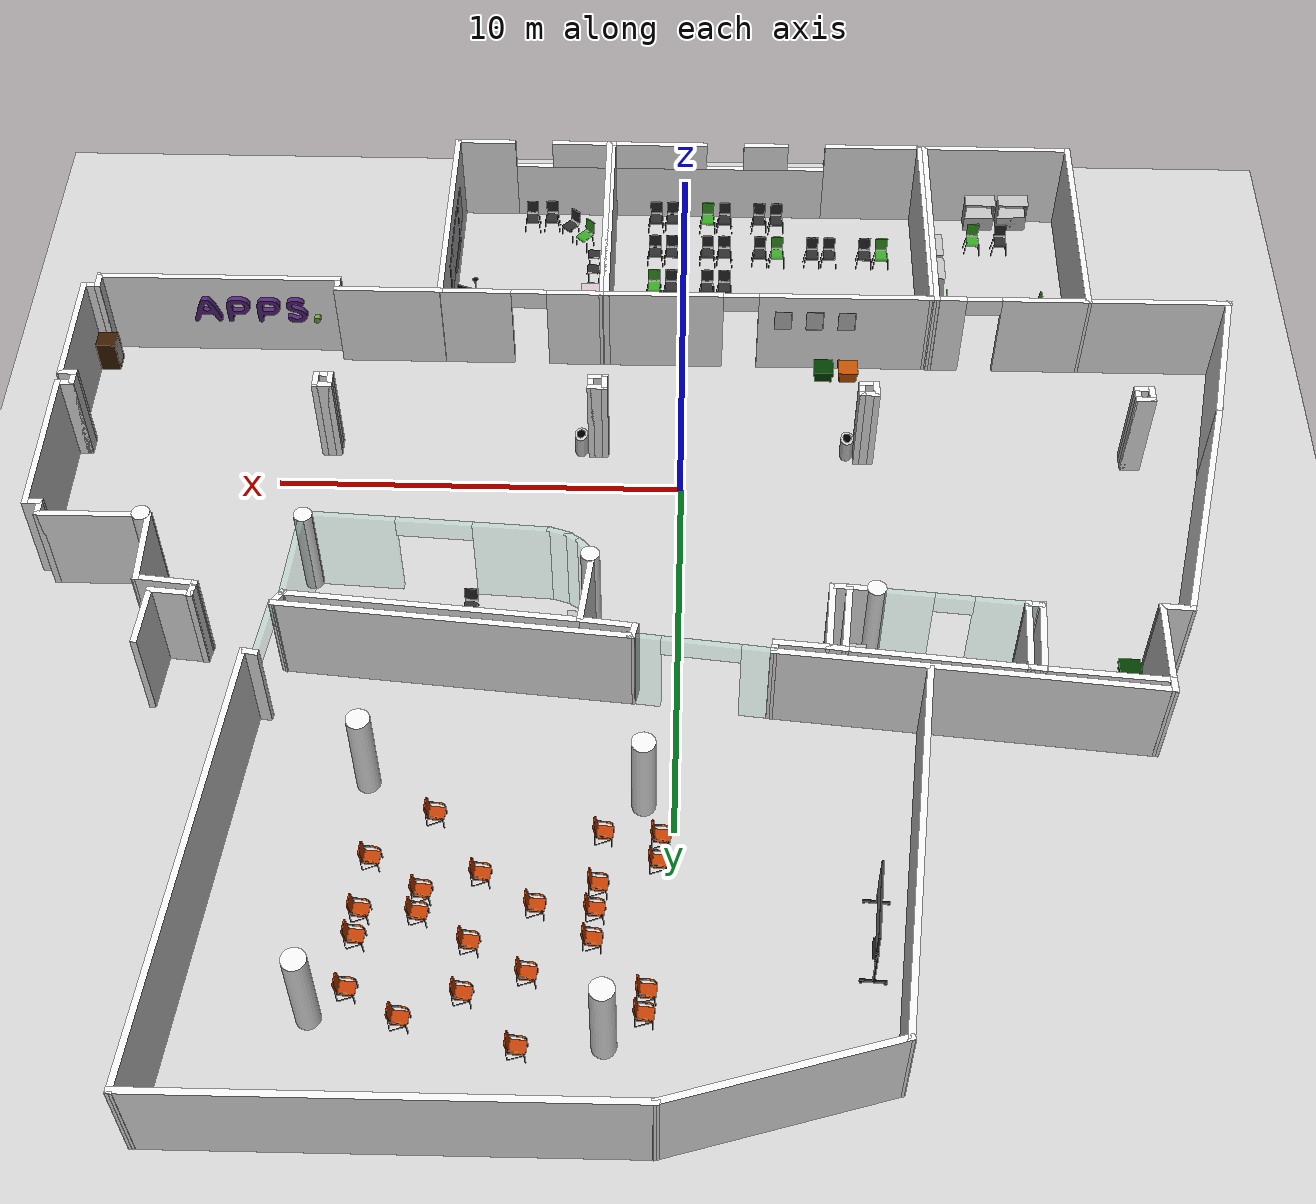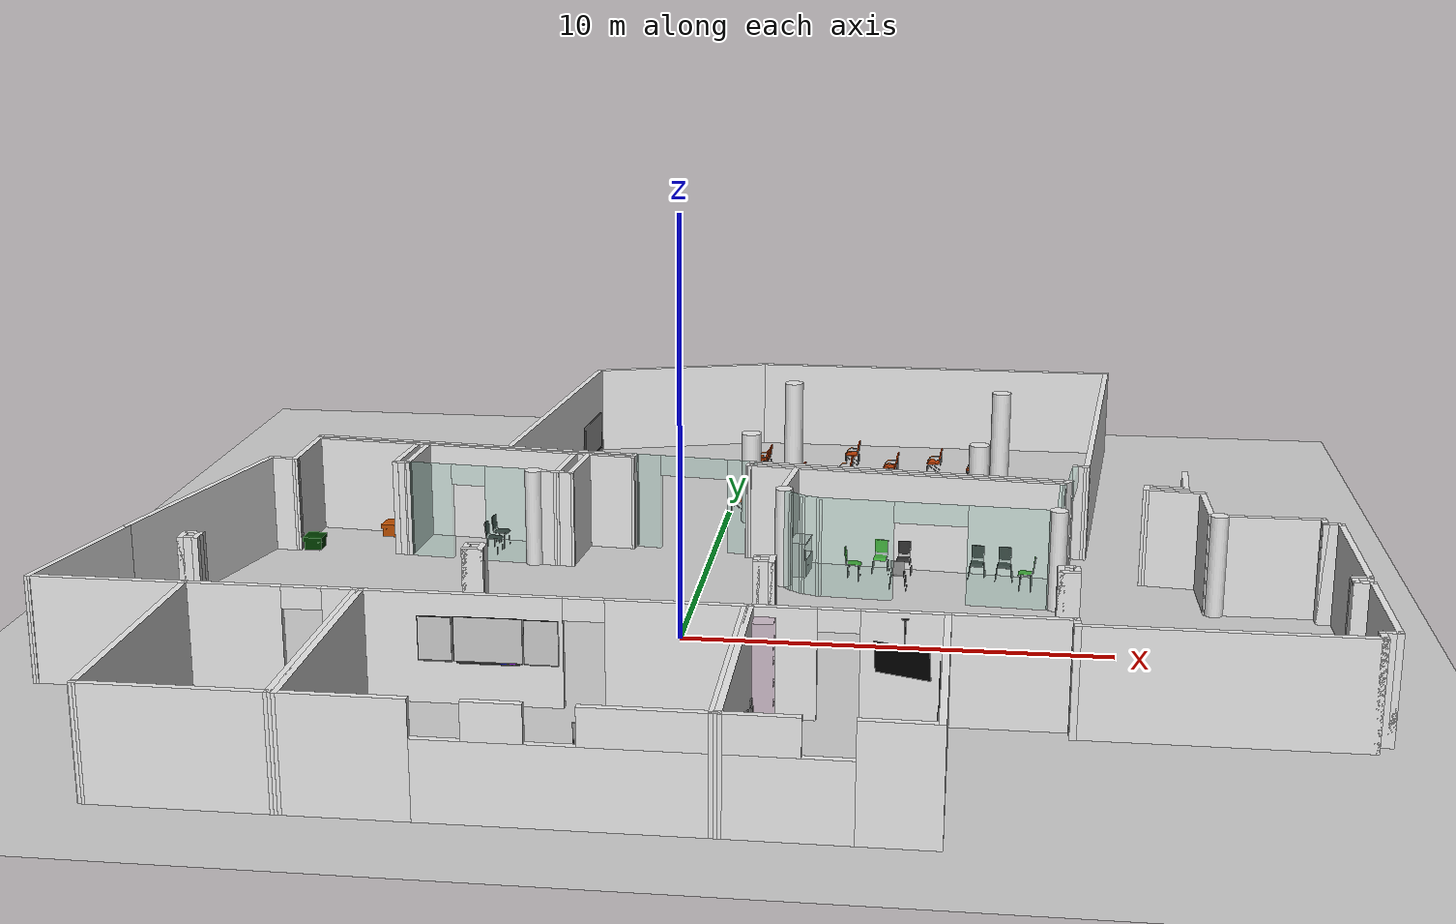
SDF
<sdf version="1.6">
 <world name="default">
  <light name="sun" type="directional">
   <pose>0 0 10 0 -0 0</pose>
   <diffuse>0.8 0.8 0.8 1</diffuse>
   <specular>0.2 0.2 0.2 1</specular>
   <attenuation>
    <range>1000</range>
    <constant>0.9</constant>
    <linear>0.01</linear>
    <quadratic>0.001</quadratic>
   </attenuation>
   <direction>-0.5 0.1 -0.9</direction>
  </light>
  <model name="ground_plane">
   <static>1</static>
   <link name="link">
    <collision name="collision">
     <geometry><plane><normal>0 0 1</normal><size>100 100</size></plane></geometry>
     <surface><friction><ode><mu>100</mu><mu2>50</mu2></ode></friction></surface>
    </collision>
    <visual name="visual">
     <cast_shadows>0</cast_shadows>
     <geometry><plane><normal>0 0 1</normal><size>100 100</size></plane></geometry>
     <material>
      <script><uri>file://media/materials/scripts/gazebo.material</uri><name>Gazebo/Grey</name></script>
     </material>
    </visual>
   </link>
  </model>
  <gravity>0 0 -9.8</gravity>
  <magnetic_field>6e-06 2.3e-05 -4.2e-05</magnetic_field>
  <atmosphere type="adiabatic"/>
  <physics name="default_physics" default="0" type="ode">
   <max_step_size>0.001</max_step_size>
   <real_time_factor>1</real_time_factor>
   <real_time_update_rate>1000</real_time_update_rate>
  </physics>
  <scene><ambient>0.4 0.4 0.4 1</ambient><background>0.7 0.7 0.7 1</background><shadows>1</shadows></scene>
  <spherical_coordinates>
   <surface_model>EARTH_WGS84</surface_model>
   <latitude_deg>0</latitude_deg>
   <longitude_deg>0</longitude_deg>
   <elevation>0</elevation>
   <heading_deg>0</heading_deg>
  </spherical_coordinates>
  <model name="columns">
   <pose>-1.23086 -1.27462 0 0 -0 0</pose>
   <link name="Wall_337">
    <collision name="Wall_337_Collision">
     <geometry><box><size>0.5 0.15 2.5</size></box></geometry>
     <pose>0 0 1.25 0 -0 0</pose>
    </collision>
    <visual name="Wall_337_Visual">
     <pose>0 0 1.25 0 -0 0</pose>
     <geometry><box><size>0.5 0.15 2.5</size></box></geometry>
     <material>
      <script><uri>file://media/materials/scripts/gazebo.material</uri><name>Gazebo/White</name></script>
      <ambient>1 1 1 1</ambient>
     </material>
     <meta><layer>0</layer></meta>
    </visual>
    <pose>9.87053 0.009422 0 0 0 -1.5708</pose>
   </link>
   <link name="Wall_338">
    <collision name="Wall_338_Collision">
     <geometry><box><size>0.5 0.15 2.5</size></box></geometry>
     <pose>0 0 1.25 0 -0 0</pose>
    </collision>
    <visual name="Wall_338_Visual">
     <pose>0 0 1.25 0 -0 0</pose>
     <geometry><box><size>0.5 0.15 2.5</size></box></geometry>
     <material>
      <script><uri>file://media/materials/scripts/gazebo.material</uri><name>Gazebo/White</name></script>
      <ambient>1 1 1 1</ambient>
     </material>
     <meta><layer>0</layer></meta>
    </visual>
    <pose>10.0455 -0.165578 0 0 -0 0</pose>
   </link>
   <link name="Wall_339">
    <collision name="Wall_339_Collision">
     <geometry><box><size>0.5 0.15 2.5</size></box></geometry>
     <pose>0 0 1.25 0 -0 0</pose>
    </collision>
    <visual name="Wall_339_Visual">
     <pose>0 0 1.25 0 -0 0</pose>
     <geometry><box><size>0.5 0.15 2.5</size></box></geometry>
     <material>
      <script><uri>file://media/materials/scripts/gazebo.material</uri><name>Gazebo/White</name></script>
      <ambient>1 1 1 1</ambient>
     </material>
     <meta><layer>0</layer></meta>
    </visual>
    <pose>10.2205 0.009422 0 0 -0 1.5708</pose>
   </link>
   <link name="Wall_340">
    <collision name="Wall_340_Collision">
     <geometry><box><size>0.5 0.15 2.5</size></box></geometry>
     <pose>0 0 1.25 0 -0 0</pose>
    </collision>
    <visual name="Wall_340_Visual">
     <pose>0 0 1.25 0 -0 0</pose>
     <geometry><box><size>0.5 0.15 2.5</size></box></geometry>
     <material>
      <script><uri>file://media/materials/scripts/gazebo.material</uri><name>Gazebo/White</name></script>
      <ambient>1 1 1 1</ambient>
     </material>
     <meta><layer>0</layer></meta>
    </visual>
    <pose>10.0455 0.184422 0 0 -0 3.14159</pose>
   </link>
   <link name="Wall_342">
    <collision name="Wall_342_Collision">
     <geometry><box><size>0.5 0.15 2.5</size></box></geometry>
     <pose>0 0 1.25 0 -0 0</pose>
    </collision>
    <visual name="Wall_342_Visual">
     <pose>0 0 1.25 0 -0 0</pose>
     <geometry><box><size>0.5 0.15 2.5</size></box></geometry>
     <material>
      <script><uri>file://media/materials/scripts/gazebo.material</uri><name>Gazebo/White</name></script>
      <ambient>1 1 1 1</ambient>
     </material>
     <meta><layer>0</layer></meta>
    </visual>
    <pose>3.13524 -0.056002 0 0 0 -1.5708</pose>
   </link>
   <link name="Wall_343">
    <collision name="Wall_343_Collision">
     <geometry><box><size>0.5 0.15 2.5</size></box></geometry>
     <pose>0 0 1.25 0 -0 0</pose>
    </collision>
    <visual name="Wall_343_Visual">
     <pose>0 0 1.25 0 -0 0</pose>
     <geometry><box><size>0.5 0.15 2.5</size></box></geometry>
     <material>
      <script><uri>file://media/materials/scripts/gazebo.material</uri><name>Gazebo/White</name></script>
      <ambient>1 1 1 1</ambient>
     </material>
     <meta><layer>0</layer></meta>
    </visual>
    <pose>3.31024 -0.231003 0 0 -0 0</pose>
   </link>
   <link name="Wall_344">
    <collision name="Wall_344_Collision">
     <geometry><box><size>0.5 0.15 2.5</size></box></geometry>
     <pose>0 0 1.25 0 -0 0</pose>
    </collision>
    <visual name="Wall_344_Visual">
     <pose>0 0 1.25 0 -0 0</pose>
     <geometry><box><size>0.5 0.15 2.5</size></box></geometry>
     <material>
      <script><uri>file://media/materials/scripts/gazebo.material</uri><name>Gazebo/White</name></script>
      <ambient>1 1 1 1</ambient>
     </material>
     <meta><layer>0</layer></meta>
    </visual>
    <pose>3.48524 -0.056002 0 0 -0 1.5708</pose>
   </link>
   <link name="Wall_345">
    <collision name="Wall_345_Collision">
     <geometry><box><size>0.5 0.15 2.5</size></box></geometry>
     <pose>0 0 1.25 0 -0 0</pose>
    </collision>
    <visual name="Wall_345_Visual">
     <pose>0 0 1.25 0 -0 0</pose>
     <geometry><box><size>0.5 0.15 2.5</size></box></geometry>
     <material>
      <script><uri>file://media/materials/scripts/gazebo.material</uri><name>Gazebo/White</name></script>
      <ambient>1 1 1 1</ambient>
     </material>
     <meta><layer>0</layer></meta>
    </visual>
    <pose>3.31024 0.118997 0 0 -0 3.14159</pose>
   </link>
   <link name="Wall_350">
    <collision name="Wall_350_Collision">
     <geometry><box><size>0.5 0.15 2.5</size></box></geometry>
     <pose>0 0 1.25 0 -0 0</pose>
    </collision>
    <visual name="Wall_350_Visual">
     <pose>0 0 1.25 0 -0 0</pose>
     <geometry><box><size>0.5 0.15 2.5</size></box></geometry>
     <material>
      <script><uri>file://media/materials/scripts/gazebo.material</uri><name>Gazebo/White</name></script>
      <ambient>1 1 1 1</ambient>
     </material>
     <meta><layer>0</layer></meta>
    </visual>
    <pose>-3.34038 0.200077 0 0 -0 0</pose>
   </link>
   <link name="Wall_351">
    <collision name="Wall_351_Collision">
     <geometry><box><size>0.5 0.15 2.5</size></box></geometry>
     <pose>0 0 1.25 0 -0 0</pose>
    </collision>
    <visual name="Wall_351_Visual">
     <pose>0 0 1.25 0 -0 0</pose>
     <geometry><box><size>0.5 0.15 2.5</size></box></geometry>
     <material>
      <script><uri>file://media/materials/scripts/gazebo.material</uri><name>Gazebo/White</name></script>
      <ambient>1 1 1 1</ambient>
     </material>
     <meta><layer>0</layer></meta>
    </visual>
    <pose>-3.16538 0.025078 0 0 0 -1.5708</pose>
   </link>
   <link name="Wall_352">
    <collision name="Wall_352_Collision">
     <geometry><box><size>0.5 0.15 2.5</size></box></geometry>
     <pose>0 0 1.25 0 -0 0</pose>
    </collision>
    <visual name="Wall_352_Visual">
     <pose>0 0 1.25 0 -0 0</pose>
     <geometry><box><size>0.5 0.15 2.5</size></box></geometry>
     <material>
      <script><uri>file://media/materials/scripts/gazebo.material</uri><name>Gazebo/White</name></script>
      <ambient>1 1 1 1</ambient>
     </material>
     <meta><layer>0</layer></meta>
    </visual>
    <pose>-3.34038 -0.149923 0 0 -0 3.14159</pose>
   </link>
   <link name="Wall_353">
    <collision name="Wall_353_Collision">
     <geometry><box><size>0.5 0.15 2.5</size></box></geometry>
     <pose>0 0 1.25 0 -0 0</pose>
    </collision>
    <visual name="Wall_353_Visual">
     <pose>0 0 1.25 0 -0 0</pose>
     <geometry><box><size>0.5 0.15 2.5</size></box></geometry>
     <material>
      <script><uri>file://media/materials/scripts/gazebo.material</uri><name>Gazebo/White</name></script>
      <ambient>1 1 1 1</ambient>
     </material>
     <meta><layer>0</layer></meta>
    </visual>
    <pose>-3.51538 0.025078 0 0 -0 1.5708</pose>
   </link>
   <link name="Wall_355">
    <collision name="Wall_355_Collision">
     <geometry><box><size>0.5 0.15 2.5</size></box></geometry>
     <pose>0 0 1.25 0 -0 0</pose>
    </collision>
    <visual name="Wall_355_Visual">
     <pose>0 0 1.25 0 -0 0</pose>
     <geometry><box><size>0.5 0.15 2.5</size></box></geometry>
     <material>
      <script><uri>file://media/materials/scripts/gazebo.material</uri><name>Gazebo/White</name></script>
      <ambient>1 1 1 1</ambient>
     </material>
     <meta><layer>0</layer></meta>
    </visual>
    <pose>-10.2205 0.056002 0 0 0 -1.5708</pose>
   </link>
   <link name="Wall_356">
    <collision name="Wall_356_Collision">
     <geometry><box><size>0.5 0.15 2.5</size></box></geometry>
     <pose>0 0 1.25 0 -0 0</pose>
    </collision>
    <visual name="Wall_356_Visual">
     <pose>0 0 1.25 0 -0 0</pose>
     <geometry><box><size>0.5 0.15 2.5</size></box></geometry>
     <material>
      <script><uri>file://media/materials/scripts/gazebo.material</uri><name>Gazebo/White</name></script>
      <ambient>1 1 1 1</ambient>
     </material>
     <meta><layer>0</layer></meta>
    </visual>
    <pose>-10.0455 -0.118998 0 0 -0 0</pose>
   </link>
   <link name="Wall_357">
    <collision name="Wall_357_Collision">
     <geometry><box><size>0.5 0.15 2.5</size></box></geometry>
     <pose>0 0 1.25 0 -0 0</pose>
    </collision>
    <visual name="Wall_357_Visual">
     <pose>0 0 1.25 0 -0 0</pose>
     <geometry><box><size>0.5 0.15 2.5</size></box></geometry>
     <material>
      <script><uri>file://media/materials/scripts/gazebo.material</uri><name>Gazebo/White</name></script>
      <ambient>1 1 1 1</ambient>
     </material>
     <meta><layer>0</layer></meta>
    </visual>
    <pose>-9.87053 0.056002 0 0 -0 1.5708</pose>
   </link>
   <link name="Wall_358">
    <collision name="Wall_358_Collision">
     <geometry><box><size>0.5 0.15 2.5</size></box></geometry>
     <pose>0 0 1.25 0 -0 0</pose>
    </collision>
    <visual name="Wall_358_Visual">
     <pose>0 0 1.25 0 -0 0</pose>
     <geometry><box><size>0.5 0.15 2.5</size></box></geometry>
     <material>
      <script><uri>file://media/materials/scripts/gazebo.material</uri><name>Gazebo/White</name></script>
      <ambient>1 1 1 1</ambient>
     </material>
     <meta><layer>0</layer></meta>
    </visual>
    <pose>-10.0455 0.231003 0 0 -0 3.14159</pose>
   </link>
   <static>1</static>
  </model>
  <model name="Glass_walls">
   <link name="Wall_10">
    <pose>8.18678 -0.842723 0 0 -0 1.49902</pose>
    <inertial>
     <mass>1</mass>
     <inertia><ixx>1</ixx><ixy>0</ixy><ixz>0</ixz><iyy>1</iyy><iyz>0</iyz><izz>1</izz></inertia>
    </inertial>
    <visual name="Wall_10_Visual">
     <pose>0 0 1.25 0 -0 0</pose>
     <geometry><box><size>2.51541 0.15 2.5</size></box></geometry>
     <material>
      <script><uri>file://media/materials/scripts/gazebo.material</uri><name>Gazebo/Grey</name></script>
      <ambient>0.435 0.796 0.675 1</ambient>
      <diffuse>0.7 0.7 0.7 1</diffuse>
      <specular>0.01 0.01 0.01 1</specular>
      <emissive>0 0 0 1</emissive>
      <shader type="vertex"><normal_map>__default__</normal_map></shader>
     </material>
     <meta><layer>0</layer></meta>
     <transparency>0.8</transparency>
    </visual>
    <collision name="Wall_10_Collision">
     <pose>0 0 1.25 0 -0 0</pose>
     <geometry><box><size>2.51541 0.15 2.5</size></box></geometry>
     <surface>
      <friction>
       <ode><mu>1</mu><mu2>1</mu2><fdir1>0 0 0</fdir1><slip1>0</slip1><slip2>0</slip2></ode>
       <torsional>
        <coefficient>1</coefficient>
        <patch_radius>0</patch_radius>
        <surface_radius>0</surface_radius>
        <use_patch_radius>1</use_patch_radius>
        <ode><slip>0</slip></ode>
       </torsional>
      </friction>
      <bounce><restitution_coefficient>0</restitution_coefficient><threshold>1e+06</threshold></bounce>
      <contact>
       <collide_without_contact>0</collide_without_contact>
       <collide_without_contact_bitmask>1</collide_without_contact_bitmask>
       <collide_bitmask>1</collide_bitmask>
       <ode>
        <soft_cfm>0</soft_cfm>
        <soft_erp>0.2</soft_erp>
        <kp>1e+13</kp>
        <kd>1</kd>
        <max_vel>0.01</max_vel>
        <min_depth>0</min_depth>
       </ode>
       <bullet>
        <split_impulse>1</split_impulse>
        <split_impulse_penetration_threshold>-0.01</split_impulse_penetration_threshold>
        <soft_cfm>0</soft_cfm>
        <soft_erp>0.2</soft_erp>
        <kp>1e+13</kp>
        <kd>1</kd>
       </bullet>
      </contact>
     </surface>
    </collision>
   </link>
   <link name="Wall_12">
    <pose>1.76645 -1.4266 0 0 0 -0.605125</pose>
    <inertial>
     <mass>1</mass>
     <inertia><ixx>1</ixx><ixy>0</ixy><ixz>0</ixz><iyy>1</iyy><iyz>0</iyz><izz>1</izz></inertia>
    </inertial>
    <visual name="Wall_12_Visual">
     <pose>0 0 1.25 0 -0 0</pose>
     <geometry><box><size>0.49057 0.15 2.5</size></box></geometry>
     <material>
      <script><uri>file://media/materials/scripts/gazebo.material</uri><name>Gazebo/Grey</name></script>
      <ambient>0.435 0.796 0.675 1</ambient>
      <diffuse>0.7 0.7 0.7 1</diffuse>
      <specular>0.01 0.01 0.01 1</specular>
      <emissive>0 0 0 1</emissive>
      <shader type="vertex"><normal_map>__default__</normal_map></shader>
     </material>
     <meta><layer>0</layer></meta>
     <transparency>0.8</transparency>
    </visual>
    <collision name="Wall_12_Collision">
     <pose>0 0 1.25 0 -0 0</pose>
     <geometry><box><size>0.49057 0.15 2.5</size></box></geometry>
     <surface>
      <friction>
       <ode><mu>1</mu><mu2>1</mu2><fdir1>0 0 0</fdir1><slip1>0</slip1><slip2>0</slip2></ode>
       <torsional>
        <coefficient>1</coefficient>
        <patch_radius>0</patch_radius>
        <surface_radius>0</surface_radius>
        <use_patch_radius>1</use_patch_radius>
        <ode><slip>0</slip></ode>
       </torsional>
      </friction>
      <bounce><restitution_coefficient>0</restitution_coefficient><threshold>1e+06</threshold></bounce>
      <contact>
       <collide_without_contact>0</collide_without_contact>
       <collide_without_contact_bitmask>1</collide_without_contact_bitmask>
       <collide_bitmask>1</collide_bitmask>
       <ode>
        <soft_cfm>0</soft_cfm>
        <soft_erp>0.2</soft_erp>
        <kp>1e+13</kp>
        <kd>1</kd>
        <max_vel>0.01</max_vel>
        <min_depth>0</min_depth>
       </ode>
       <bullet>
        <split_impulse>1</split_impulse>
        <split_impulse_penetration_threshold>-0.01</split_impulse_penetration_threshold>
        <soft_cfm>0</soft_cfm>
        <soft_erp>0.2</soft_erp>
        <kp>1e+13</kp>
        <kd>1</kd>
       </bullet>
      </contact>
     </surface>
    </collision>
   </link>
   <link name="Wall_13">
    <pose>2.11043 -1.58974 0 0 0 -0.314232</pose>
    <inertial>
     <mass>1</mass>
     <inertia><ixx>1</ixx><ixy>0</ixy><ixz>0</ixz><iyy>1</iyy><iyz>0</iyz><izz>1</izz></inertia>
    </inertial>
    <visual name="Wall_13_Visual">
     <pose>0 0 1.25 0 -0 0</pose>
     <geometry><box><size>0.57887 0.15 2.5</size></box></geometry>
     <material>
      <script><uri>file://media/materials/scripts/gazebo.material</uri><name>Gazebo/Grey</name></script>
      <ambient>0.435 0.796 0.675 1</ambient>
      <diffuse>0.7 0.7 0.7 1</diffuse>
      <specular>0.01 0.01 0.01 1</specular>
      <emissive>0 0 0 1</emissive>
      <shader type="vertex"><normal_map>__default__</normal_map></shader>
     </material>
     <meta><layer>0</layer></meta>
     <transparency>0.8</transparency>
    </visual>
    <collision name="Wall_13_Collision">
     <pose>0 0 1.25 0 -0 0</pose>
     <geometry><box><size>0.57887 0.15 2.5</size></box></geometry>
     <surface>
      <friction>
       <ode><mu>1</mu><mu2>1</mu2><fdir1>0 0 0</fdir1><slip1>0</slip1><slip2>0</slip2></ode>
       <torsional>
        <coefficient>1</coefficient>
        <patch_radius>0</patch_radius>
        <surface_radius>0</surface_radius>
        <use_patch_radius>1</use_patch_radius>
        <ode><slip>0</slip></ode>
       </torsional>
      </friction>
      <bounce><restitution_coefficient>0</restitution_coefficient><threshold>1e+06</threshold></bounce>
      <contact>
       <collide_without_contact>0</collide_without_contact>
       <collide_without_contact_bitmask>1</collide_without_contact_bitmask>
       <collide_bitmask>1</collide_bitmask>
       <ode>
        <soft_cfm>0</soft_cfm>
        <soft_erp>0.2</soft_erp>
        <kp>1e+13</kp>
        <kd>1</kd>
        <max_vel>0.01</max_vel>
        <min_depth>0</min_depth>
       </ode>
       <bullet>
        <split_impulse>1</split_impulse>
        <split_impulse_penetration_threshold>-0.01</split_impulse_penetration_threshold>
        <soft_cfm>0</soft_cfm>
        <soft_erp>0.2</soft_erp>
        <kp>1e+13</kp>
        <kd>1</kd>
       </bullet>
      </contact>
     </surface>
    </collision>
   </link>
   <link name="Wall_14">
    <pose>5.20817 -1.8392 0 0 0 -0.063217</pose>
    <inertial>
     <mass>1</mass>
     <inertia><ixx>1</ixx><ixy>0</ixy><ixz>0</ixz><iyy>1</iyy><iyz>0</iyz><izz>1</izz></inertia>
    </inertial>
    <visual name="Wall_14_Visual_2">
     <pose>-0.177864 0 2.25 0 -0 0</pose>
     <geometry><box><size>1.8 0.15 0.5</size></box></geometry>
     <material>
      <script><uri>file://media/materials/scripts/gazebo.material</uri><name>Gazebo/Grey</name></script>
      <ambient>0.435 0.796 0.675 1</ambient>
      <diffuse>0.7 0.7 0.7 1</diffuse>
      <specular>0.01 0.01 0.01 1</specular>
      <emissive>0 0 0 1</emissive>
      <shader type="vertex"><normal_map>__default__</normal_map></shader>
     </material>
     <meta><layer>0</layer></meta>
     <transparency>0.8</transparency>
    </visual>
    <visual name="Wall_14_Visual_1">
     <pose>1.84837 0 1.25 0 -0 0</pose>
     <geometry><box><size>2.25246 0.15 2.5</size></box></geometry>
     <material>
      <script><uri>file://media/materials/scripts/gazebo.material</uri><name>Gazebo/Grey</name></script>
      <ambient>0.435 0.796 0.675 1</ambient>
      <diffuse>0.7 0.7 0.7 1</diffuse>
      <specular>0.01 0.01 0.01 1</specular>
      <emissive>0 0 0 1</emissive>
      <shader type="vertex"><normal_map>__default__</normal_map></shader>
     </material>
     <meta><layer>0</layer></meta>
     <transparency>0.8</transparency>
    </visual>
    <visual name="Wall_14_Visual_0">
     <pose>-2.02623 0 1.25 0 -0 0</pose>
     <geometry><box><size>1.89673 0.15 2.5</size></box></geometry>
     <material>
      <script><uri>file://media/materials/scripts/gazebo.material</uri><name>Gazebo/Grey</name></script>
      <ambient>0.435 0.796 0.675 1</ambient>
      <diffuse>0.7 0.7 0.7 1</diffuse>
      <specular>0.01 0.01 0.01 1</specular>
      <emissive>0 0 0 1</emissive>
      <shader type="vertex"><normal_map>__default__</normal_map></shader>
     </material>
     <meta><layer>0</layer></meta>
     <transparency>0.8</transparency>
    </visual>
    <collision name="Wall_14_Collision_1">
     <pose>1.84837 0 1.25 0 -0 0</pose>
     <geometry><box><size>2.25246 0.15 2.5</size></box></geometry>
     <surface>
      <friction>
       <ode><mu>1</mu><mu2>1</mu2><fdir1>0 0 0</fdir1><slip1>0</slip1><slip2>0</slip2></ode>
       <torsional>
        <coefficient>1</coefficient>
        <patch_radius>0</patch_radius>
        <surface_radius>0</surface_radius>
        <use_patch_radius>1</use_patch_radius>
        <ode><slip>0</slip></ode>
       </torsional>
      </friction>
      <bounce><restitution_coefficient>0</restitution_coefficient><threshold>1e+06</threshold></bounce>
      <contact>
       <collide_without_contact>0</collide_without_contact>
       <collide_without_contact_bitmask>1</collide_without_contact_bitmask>
       <collide_bitmask>1</collide_bitmask>
       <ode>
        <soft_cfm>0</soft_cfm>
        <soft_erp>0.2</soft_erp>
        <kp>1e+13</kp>
        <kd>1</kd>
        <max_vel>0.01</max_vel>
        <min_depth>0</min_depth>
       </ode>
       <bullet>
        <split_impulse>1</split_impulse>
        <split_impulse_penetration_threshold>-0.01</split_impulse_penetration_threshold>
        <soft_cfm>0</soft_cfm>
        <soft_erp>0.2</soft_erp>
        <kp>1e+13</kp>
        <kd>1</kd>
       </bullet>
      </contact>
     </surface>
    </collision>
    <collision name="Wall_14_Collision_0">
     <pose>-2.02623 0 1.25 0 -0 0</pose>
     <geometry><box><size>1.89673 0.15 2.5</size></box></geometry>
     <surface>
      <friction>
       <ode><mu>1</mu><mu2>1</mu2><fdir1>0 0 0</fdir1><slip1>0</slip1><slip2>0</slip2></ode>
       <torsional>
        <coefficient>1</coefficient>
        <patch_radius>0</patch_radius>
        <surface_radius>0</surface_radius>
        <use_patch_radius>1</use_patch_radius>
        <ode><slip>0</slip></ode>
       </torsional>
      </friction>
      <bounce><restitution_coefficient>0</restitution_coefficient><threshold>1e+06</threshold></bounce>
      <contact>
       <collide_without_contact>0</collide_without_contact>
       <collide_without_contact_bitmask>1</collide_without_contact_bitmask>
       <collide_bitmask>1</collide_bitmask>
       <ode>
        <soft_cfm>0</soft_cfm>
        <soft_erp>0.2</soft_erp>
        <kp>1e+13</kp>
        <kd>1</kd>
        <max_vel>0.01</max_vel>
        <min_depth>0</min_depth>
       </ode>
       <bullet>
        <split_impulse>1</split_impulse>
        <split_impulse_penetration_threshold>-0.01</split_impulse_penetration_threshold>
        <soft_cfm>0</soft_cfm>
        <soft_erp>0.2</soft_erp>
        <kp>1e+13</kp>
        <kd>1</kd>
       </bullet>
      </contact>
     </surface>
    </collision>
    <collision name="Wall_14_Collision_2">
     <pose>-0.177864 0 2.25 0 -0 0</pose>
     <geometry><box><size>1.8 0.15 0.5</size></box></geometry>
     <surface>
      <friction>
       <ode><mu>1</mu><mu2>1</mu2><fdir1>0 0 0</fdir1><slip1>0</slip1><slip2>0</slip2></ode>
       <torsional>
        <coefficient>1</coefficient>
        <patch_radius>0</patch_radius>
        <surface_radius>0</surface_radius>
        <use_patch_radius>1</use_patch_radius>
        <ode><slip>0</slip></ode>
       </torsional>
      </friction>
      <bounce><restitution_coefficient>0</restitution_coefficient><threshold>1e+06</threshold></bounce>
      <contact>
       <collide_without_contact>0</collide_without_contact>
       <collide_without_contact_bitmask>1</collide_without_contact_bitmask>
       <collide_bitmask>1</collide_bitmask>
       <ode>
        <soft_cfm>0</soft_cfm>
        <soft_erp>0.2</soft_erp>
        <kp>1e+13</kp>
        <kd>1</kd>
        <max_vel>0.01</max_vel>
        <min_depth>0</min_depth>
       </ode>
       <bullet>
        <split_impulse>1</split_impulse>
        <split_impulse_penetration_threshold>-0.01</split_impulse_penetration_threshold>
        <soft_cfm>0</soft_cfm>
        <soft_erp>0.2</soft_erp>
        <kp>1e+13</kp>
        <kd>1</kd>
       </bullet>
      </contact>
     </surface>
    </collision>
   </link>
   <link name="Wall_16">
    <pose>-1.20178 1.53997 0 0 0 -0.111358</pose>
    <inertial>
     <mass>1</mass>
     <inertia><ixx>1</ixx><ixy>0</ixy><ixz>0</ixz><iyy>1</iyy><iyz>0</iyz><izz>1</izz></inertia>
    </inertial>
    <visual name="Wall_16_Visual_0">
     <pose>-1.28798 0 1.25 0 -0 0</pose>
     <geometry><box><size>0.785518 0.15 2.5</size></box></geometry>
     <material>
      <script><uri>file://media/materials/scripts/gazebo.material</uri><name>Gazebo/Grey</name></script>
      <ambient>0.435 0.796 0.675 1</ambient>
      <diffuse>0.7 0.7 0.7 1</diffuse>
      <specular>0.01 0.01 0.01 1</specular>
      <emissive>0 0 0 1</emissive>
      <shader type="vertex"><normal_map>__default__</normal_map></shader>
     </material>
     <meta><layer>0</layer></meta>
     <transparency>0.8</transparency>
    </visual>
    <visual name="Wall_16_Visual_1">
     <pose>1.29276 0 1.25 0 -0 0</pose>
     <geometry><box><size>0.775955 0.15 2.5</size></box></geometry>
     <material>
      <script><uri>file://media/materials/scripts/gazebo.material</uri><name>Gazebo/Grey</name></script>
      <ambient>0.435 0.796 0.675 1</ambient>
      <diffuse>0.7 0.7 0.7 1</diffuse>
      <specular>0.01 0.01 0.01 1</specular>
      <emissive>0 0 0 1</emissive>
      <shader type="vertex"><normal_map>__default__</normal_map></shader>
     </material>
     <meta><layer>0</layer></meta>
     <transparency>0.8</transparency>
    </visual>
    <visual name="Wall_16_Visual_2">
     <pose>0.004782 0 2.25 0 -0 0</pose>
     <geometry><box><size>1.8 0.15 0.5</size></box></geometry>
     <material>
      <script><uri>file://media/materials/scripts/gazebo.material</uri><name>Gazebo/Grey</name></script>
      <ambient>0.435 0.796 0.675 1</ambient>
      <diffuse>0.7 0.7 0.7 1</diffuse>
      <specular>0.01 0.01 0.01 1</specular>
      <emissive>0 0 0 1</emissive>
      <shader type="vertex"><normal_map>__default__</normal_map></shader>
     </material>
     <meta><layer>0</layer></meta>
     <transparency>0.8</transparency>
    </visual>
    <collision name="Wall_16_Collision_0">
     <pose>-1.28798 0 1.25 0 -0 0</pose>
     <geometry><box><size>0.785518 0.15 2.5</size></box></geometry>
     <surface>
      <friction>
       <ode><mu>1</mu><mu2>1</mu2><fdir1>0 0 0</fdir1><slip1>0</slip1><slip2>0</slip2></ode>
       <torsional>
        <coefficient>1</coefficient>
        <patch_radius>0</patch_radius>
        <surface_radius>0</surface_radius>
        <use_patch_radius>1</use_patch_radius>
        <ode><slip>0</slip></ode>
       </torsional>
      </friction>
      <bounce><restitution_coefficient>0</restitution_coefficient><threshold>1e+06</threshold></bounce>
      <contact>
       <collide_without_contact>0</collide_without_contact>
       <collide_without_contact_bitmask>1</collide_without_contact_bitmask>
       <collide_bitmask>1</collide_bitmask>
       <ode>
        <soft_cfm>0</soft_cfm>
        <soft_erp>0.2</soft_erp>
        <kp>1e+13</kp>
        <kd>1</kd>
        <max_vel>0.01</max_vel>
        <min_depth>0</min_depth>
       </ode>
       <bullet>
        <split_impulse>1</split_impulse>
        <split_impulse_penetration_threshold>-0.01</split_impulse_penetration_threshold>
        <soft_cfm>0</soft_cfm>
        <soft_erp>0.2</soft_erp>
        <kp>1e+13</kp>
        <kd>1</kd>
       </bullet>
      </contact>
     </surface>
    </collision>
    <collision name="Wall_16_Collision_2">
     <pose>0.004782 0 2.25 0 -0 0</pose>
     <geometry><box><size>1.8 0.15 0.5</size></box></geometry>
     <surface>
      <friction>
       <ode><mu>1</mu><mu2>1</mu2><fdir1>0 0 0</fdir1><slip1>0</slip1><slip2>0</slip2></ode>
       <torsional>
        <coefficient>1</coefficient>
        <patch_radius>0</patch_radius>
        <surface_radius>0</surface_radius>
        <use_patch_radius>1</use_patch_radius>
        <ode><slip>0</slip></ode>
       </torsional>
      </friction>
      <bounce><restitution_coefficient>0</restitution_coefficient><threshold>1e+06</threshold></bounce>
      <contact>
       <collide_without_contact>0</collide_without_contact>
       <collide_without_contact_bitmask>1</collide_without_contact_bitmask>
       <collide_bitmask>1</collide_bitmask>
       <ode>
        <soft_cfm>0</soft_cfm>
        <soft_erp>0.2</soft_erp>
        <kp>1e+13</kp>
        <kd>1</kd>
        <max_vel>0.01</max_vel>
        <min_depth>0</min_depth>
       </ode>
       <bullet>
        <split_impulse>1</split_impulse>
        <split_impulse_penetration_threshold>-0.01</split_impulse_penetration_threshold>
        <soft_cfm>0</soft_cfm>
        <soft_erp>0.2</soft_erp>
        <kp>1e+13</kp>
        <kd>1</kd>
       </bullet>
      </contact>
     </surface>
    </collision>
    <collision name="Wall_16_Collision_1">
     <pose>1.29276 0 1.25 0 -0 0</pose>
     <geometry><box><size>0.775955 0.15 2.5</size></box></geometry>
     <surface>
      <friction>
       <ode><mu>1</mu><mu2>1</mu2><fdir1>0 0 0</fdir1><slip1>0</slip1><slip2>0</slip2></ode>
       <torsional>
        <coefficient>1</coefficient>
        <patch_radius>0</patch_radius>
        <surface_radius>0</surface_radius>
        <use_patch_radius>1</use_patch_radius>
        <ode><slip>0</slip></ode>
       </torsional>
      </friction>
      <bounce><restitution_coefficient>0</restitution_coefficient><threshold>1e+06</threshold></bounce>
      <contact>
       <collide_without_contact>0</collide_without_contact>
       <collide_without_contact_bitmask>1</collide_without_contact_bitmask>
       <collide_bitmask>1</collide_bitmask>
       <ode>
        <soft_cfm>0</soft_cfm>
        <soft_erp>0.2</soft_erp>
        <kp>1e+13</kp>
        <kd>1</kd>
        <max_vel>0.01</max_vel>
        <min_depth>0</min_depth>
       </ode>
       <bullet>
        <split_impulse>1</split_impulse>
        <split_impulse_penetration_threshold>-0.01</split_impulse_penetration_threshold>
        <soft_cfm>0</soft_cfm>
        <soft_erp>0.2</soft_erp>
        <kp>1e+13</kp>
        <kd>1</kd>
       </bullet>
      </contact>
     </surface>
    </collision>
   </link>
   <link name="Wall_18">
    <pose>8.55334 1.28019 0.999398 0 -0 1.44515</pose>
    <inertial>
     <mass>1</mass>
     <pose>0 0 1.25 0 -0 0</pose>
     <inertia><ixx>1</ixx><ixy>0</ixy><ixz>0</ixz><iyy>1</iyy><iyz>0</iyz><izz>1</izz></inertia>
    </inertial>
    <visual name="Wall_18_Visual_0">
     <pose>0 0 1.25 0 -0 0</pose>
     <geometry><box><size>1.44127 0.15 0.5</size></box></geometry>
     <material>
      <script><uri>file://media/materials/scripts/gazebo.material</uri><name>Gazebo/Grey</name></script>
      <ambient>0.435 0.796 0.675 1</ambient>
      <diffuse>0.7 0.7 0.7 1</diffuse>
      <specular>0.01 0.01 0.01 1</specular>
      <emissive>0 0 0 1</emissive>
      <shader type="vertex"><normal_map>__default__</normal_map></shader>
     </material>
     <meta><layer>0</layer></meta>
     <transparency>0.8</transparency>
    </visual>
    <collision name="Wall_18_Collision_0">
     <pose>0 0 1.25 0 -0 0</pose>
     <geometry><box><size>1.44127 0.15 0.5</size></box></geometry>
     <surface>
      <friction>
       <ode><mu>1</mu><mu2>1</mu2><fdir1>0 0 0</fdir1><slip1>0</slip1><slip2>0</slip2></ode>
       <torsional>
        <coefficient>1</coefficient>
        <patch_radius>0</patch_radius>
        <surface_radius>0</surface_radius>
        <use_patch_radius>1</use_patch_radius>
        <ode><slip>0</slip></ode>
       </torsional>
      </friction>
      <bounce><restitution_coefficient>0</restitution_coefficient><threshold>1e+06</threshold></bounce>
      <contact>
       <collide_without_contact>0</collide_without_contact>
       <collide_without_contact_bitmask>1</collide_without_contact_bitmask>
       <collide_bitmask>1</collide_bitmask>
       <ode>
        <soft_cfm>0</soft_cfm>
        <soft_erp>0.2</soft_erp>
        <kp>1e+13</kp>
        <kd>1</kd>
        <max_vel>0.01</max_vel>
        <min_depth>0</min_depth>
       </ode>
       <bullet>
        <split_impulse>1</split_impulse>
        <split_impulse_penetration_threshold>-0.01</split_impulse_penetration_threshold>
        <soft_cfm>0</soft_cfm>
        <soft_erp>0.2</soft_erp>
        <kp>1e+13</kp>
        <kd>1</kd>
       </bullet>
      </contact>
     </surface>
    </collision>
   </link>
   <link name="Wall_4">
    <pose>-6.95661 0.126193 -0.003941 0 0 -0.091842</pose>
    <inertial>
     <mass>1</mass>
     <inertia><ixx>1</ixx><ixy>0</ixy><ixz>0</ixz><iyy>1</iyy><iyz>0</iyz><izz>1</izz></inertia>
    </inertial>
    <visual name="Wall_4_Visual_0">
     <pose>-1.09152 0 1.25 0 -0 0</pose>
     <geometry><box><size>1.41183 0.15 2.5</size></box></geometry>
     <material>
      <script><uri>file://media/materials/scripts/gazebo.material</uri><name>Gazebo/Grey</name></script>
      <ambient>0.435 0.796 0.675 1</ambient>
      <diffuse>0.7 0.7 0.7 1</diffuse>
      <specular>0.01 0.01 0.01 1</specular>
      <emissive>0 0 0 1</emissive>
      <shader type="vertex"><normal_map>__default__</normal_map></shader>
     </material>
     <meta><layer>0</layer></meta>
     <transparency>0.8</transparency>
    </visual>
    <visual name="Wall_4_Visual_2">
     <pose>0.064394 0 2.25 0 -0 0</pose>
     <geometry><box><size>0.9 0.15 0.5</size></box></geometry>
     <material>
      <script><uri>file://media/materials/scripts/gazebo.material</uri><name>Gazebo/Grey</name></script>
      <ambient>0.435 0.796 0.675 1</ambient>
      <diffuse>0.7 0.7 0.7 1</diffuse>
      <specular>0.01 0.01 0.01 1</specular>
      <emissive>0 0 0 1</emissive>
      <shader type="vertex"><normal_map>__default__</normal_map></shader>
     </material>
     <meta><layer>0</layer></meta>
     <transparency>0.8</transparency>
    </visual>
    <visual name="Wall_4_Visual_1">
     <pose>1.15592 0 1.25 0 -0 0</pose>
     <geometry><box><size>1.28304 0.15 2.5</size></box></geometry>
     <material>
      <script><uri>file://media/materials/scripts/gazebo.material</uri><name>Gazebo/Grey</name></script>
      <ambient>0.435 0.796 0.675 1</ambient>
      <diffuse>0.7 0.7 0.7 1</diffuse>
      <specular>0.01 0.01 0.01 1</specular>
      <emissive>0 0 0 1</emissive>
      <shader type="vertex"><normal_map>__default__</normal_map></shader>
     </material>
     <meta><layer>0</layer></meta>
     <transparency>0.8</transparency>
    </visual>
    <collision name="Wall_4_Collision_0">
     <pose>-1.09152 0 1.25 0 -0 0</pose>
     <geometry><box><size>1.41183 0.15 2.5</size></box></geometry>
     <surface>
      <friction>
       <ode><mu>1</mu><mu2>1</mu2><fdir1>0 0 0</fdir1><slip1>0</slip1><slip2>0</slip2></ode>
       <torsional>
        <coefficient>1</coefficient>
        <patch_radius>0</patch_radius>
        <surface_radius>0</surface_radius>
        <use_patch_radius>1</use_patch_radius>
        <ode><slip>0</slip></ode>
       </torsional>
      </friction>
      <bounce><restitution_coefficient>0</restitution_coefficient><threshold>1e+06</threshold></bounce>
      <contact>
       <collide_without_contact>0</collide_without_contact>
       <collide_without_contact_bitmask>1</collide_without_contact_bitmask>
       <collide_bitmask>1</collide_bitmask>
       <ode>
        <soft_cfm>0</soft_cfm>
        <soft_erp>0.2</soft_erp>
        <kp>1e+13</kp>
        <kd>1</kd>
        <max_vel>0.01</max_vel>
        <min_depth>0</min_depth>
       </ode>
       <bullet>
        <split_impulse>1</split_impulse>
        <split_impulse_penetration_threshold>-0.01</split_impulse_penetration_threshold>
        <soft_cfm>0</soft_cfm>
        <soft_erp>0.2</soft_erp>
        <kp>1e+13</kp>
        <kd>1</kd>
       </bullet>
      </contact>
     </surface>
    </collision>
    <collision name="Wall_4_Collision_1">
     <pose>1.15592 0 1.25 0 -0 0</pose>
     <geometry><box><size>1.28304 0.15 2.5</size></box></geometry>
     <surface>
      <friction>
       <ode><mu>1</mu><mu2>1</mu2><fdir1>0 0 0</fdir1><slip1>0</slip1><slip2>0</slip2></ode>
       <torsional>
        <coefficient>1</coefficient>
        <patch_radius>0</patch_radius>
        <surface_radius>0</surface_radius>
        <use_patch_radius>1</use_patch_radius>
        <ode><slip>0</slip></ode>
       </torsional>
      </friction>
      <bounce><restitution_coefficient>0</restitution_coefficient><threshold>1e+06</threshold></bounce>
      <contact>
       <collide_without_contact>0</collide_without_contact>
       <collide_without_contact_bitmask>1</collide_without_contact_bitmask>
       <collide_bitmask>1</collide_bitmask>
       <ode>
        <soft_cfm>0</soft_cfm>
        <soft_erp>0.2</soft_erp>
        <kp>1e+13</kp>
        <kd>1</kd>
        <max_vel>0.01</max_vel>
        <min_depth>0</min_depth>
       </ode>
       <bullet>
        <split_impulse>1</split_impulse>
        <split_impulse_penetration_threshold>-0.01</split_impulse_penetration_threshold>
        <soft_cfm>0</soft_cfm>
        <soft_erp>0.2</soft_erp>
        <kp>1e+13</kp>
        <kd>1</kd>
       </bullet>
      </contact>
     </surface>
    </collision>
    <collision name="Wall_4_Collision_2">
     <pose>0.064394 0 2.25 0 -0 0</pose>
     <geometry><box><size>0.9 0.15 0.5</size></box></geometry>
     <surface>
      <friction>
       <ode><mu>1</mu><mu2>1</mu2><fdir1>0 0 0</fdir1><slip1>0</slip1><slip2>0</slip2></ode>
       <torsional>
        <coefficient>1</coefficient>
        <patch_radius>0</patch_radius>
        <surface_radius>0</surface_radius>
        <use_patch_radius>1</use_patch_radius>
        <ode><slip>0</slip></ode>
       </torsional>
      </friction>
      <bounce><restitution_coefficient>0</restitution_coefficient><threshold>1e+06</threshold></bounce>
      <contact>
       <collide_without_contact>0</collide_without_contact>
       <collide_without_contact_bitmask>1</collide_without_contact_bitmask>
       <collide_bitmask>1</collide_bitmask>
       <ode>
        <soft_cfm>0</soft_cfm>
        <soft_erp>0.2</soft_erp>
        <kp>1e+13</kp>
        <kd>1</kd>
        <max_vel>0.01</max_vel>
        <min_depth>0</min_depth>
       </ode>
       <bullet>
        <split_impulse>1</split_impulse>
        <split_impulse_penetration_threshold>-0.01</split_impulse_penetration_threshold>
        <soft_cfm>0</soft_cfm>
        <soft_erp>0.2</soft_erp>
        <kp>1e+13</kp>
        <kd>1</kd>
       </bullet>
      </contact>
     </surface>
    </collision>
   </link>
   <link name="Wall_6">
    <pose>1.50015 -1.18229 0 0 0 -0.862665</pose>
    <inertial>
     <mass>1</mass>
     <inertia><ixx>1</ixx><ixy>0</ixy><ixz>0</ixz><iyy>1</iyy><iyz>0</iyz><izz>1</izz></inertia>
    </inertial>
    <visual name="Wall_6_Visual">
     <pose>0 0 1.25 0 -0 0</pose>
     <geometry><box><size>0.538201 0.15 2.5</size></box></geometry>
     <material>
      <script><uri>file://media/materials/scripts/gazebo.material</uri><name>Gazebo/Grey</name></script>
      <ambient>0.435 0.796 0.675 1</ambient>
      <diffuse>0.7 0.7 0.7 1</diffuse>
      <specular>0.01 0.01 0.01 1</specular>
      <emissive>0 0 0 1</emissive>
      <shader type="vertex"><normal_map>__default__</normal_map></shader>
     </material>
     <meta><layer>0</layer></meta>
     <transparency>0.8</transparency>
    </visual>
    <collision name="Wall_6_Collision">
     <pose>0 0 1.25 0 -0 0</pose>
     <geometry><box><size>0.538201 0.15 2.5</size></box></geometry>
     <surface>
      <friction>
       <ode><mu>1</mu><mu2>1</mu2><fdir1>0 0 0</fdir1><slip1>0</slip1><slip2>0</slip2></ode>
       <torsional>
        <coefficient>1</coefficient>
        <patch_radius>0</patch_radius>
        <surface_radius>0</surface_radius>
        <use_patch_radius>1</use_patch_radius>
        <ode><slip>0</slip></ode>
       </torsional>
      </friction>
      <bounce><restitution_coefficient>0</restitution_coefficient><threshold>1e+06</threshold></bounce>
      <contact>
       <collide_without_contact>0</collide_without_contact>
       <collide_without_contact_bitmask>1</collide_without_contact_bitmask>
       <collide_bitmask>1</collide_bitmask>
       <ode>
        <soft_cfm>0</soft_cfm>
        <soft_erp>0.2</soft_erp>
        <kp>1e+13</kp>
        <kd>1</kd>
        <max_vel>0.01</max_vel>
        <min_depth>0</min_depth>
       </ode>
       <bullet>
        <split_impulse>1</split_impulse>
        <split_impulse_penetration_threshold>-0.01</split_impulse_penetration_threshold>
        <soft_cfm>0</soft_cfm>
        <soft_erp>0.2</soft_erp>
        <kp>1e+13</kp>
        <kd>1</kd>
       </bullet>
      </contact>
     </surface>
    </collision>
   </link>
   <static>1</static>
   <pose>0.66554 5.08189 0 0 -0 0</pose>
  </model>
  <model name="ucu_basic_frame.world">
   <link name="Wall_171">
    <pose>5.44548 -11.0107 0 0 -0 1.5685</pose>
    <visual name="Wall_171_Visual">
     <pose>0 0 1.25 0 -0 0</pose>
     <geometry><box><size>5.97284 0.15 2.5</size></box></geometry>
     <material>
      <script><uri>file://media/materials/scripts/gazebo.material</uri><name>Gazebo/White</name></script>
      <ambient>1 1 1 1</ambient>
      <diffuse>1 1 1 1</diffuse>
      <specular>0 0 0 1</specular>
      <emissive>0 0 0 1</emissive>
     </material>
     <meta><layer>0</layer></meta>
    </visual>
    <collision name="Wall_171_Collision">
     <pose>0 0 1.25 0 -0 0</pose>
     <geometry><box><size>5.97284 0.15 2.5</size></box></geometry>
     <surface>
      <friction>
       <ode><mu>1</mu><mu2>1</mu2><fdir1>0 0 0</fdir1><slip1>0</slip1><slip2>0</slip2></ode>
       <torsional>
        <coefficient>1</coefficient>
        <patch_radius>0</patch_radius>
        <surface_radius>0</surface_radius>
        <use_patch_radius>1</use_patch_radius>
        <ode><slip>0</slip></ode>
       </torsional>
      </friction>
      <bounce><restitution_coefficient>0</restitution_coefficient><threshold>1e+06</threshold></bounce>
      <contact>
       <collide_without_contact>0</collide_without_contact>
       <collide_without_contact_bitmask>1</collide_without_contact_bitmask>
       <collide_bitmask>1</collide_bitmask>
       <ode>
        <soft_cfm>0</soft_cfm>
        <soft_erp>0.2</soft_erp>
        <kp>1e+13</kp>
        <kd>1</kd>
        <max_vel>0.01</max_vel>
        <min_depth>0</min_depth>
       </ode>
       <bullet>
        <split_impulse>1</split_impulse>
        <split_impulse_penetration_threshold>-0.01</split_impulse_penetration_threshold>
        <soft_cfm>0</soft_cfm>
        <soft_erp>0.2</soft_erp>
        <kp>1e+13</kp>
        <kd>1</kd>
       </bullet>
      </contact>
     </surface>
    </collision>
   </link>
   <link name="Wall_172">
    <pose>6.76546 -8.09988 0 0 0 -0.000444</pose>
    <visual name="Wall_172_Visual">
     <pose>0 0 1.25 0 -0 0</pose>
     <geometry><box><size>2.77695 0.15 2.5</size></box></geometry>
     <material>
      <script><uri>file://media/materials/scripts/gazebo.material</uri><name>Gazebo/White</name></script>
      <ambient>1 1 1 1</ambient>
      <diffuse>1 1 1 1</diffuse>
      <specular>0 0 0 1</specular>
      <emissive>0 0 0 1</emissive>
     </material>
     <meta><layer>0</layer></meta>
    </visual>
    <collision name="Wall_172_Collision">
     <pose>0 0 1.25 0 -0 0</pose>
     <geometry><box><size>2.77695 0.15 2.5</size></box></geometry>
     <surface>
      <friction>
       <ode><mu>1</mu><mu2>1</mu2><fdir1>0 0 0</fdir1><slip1>0</slip1><slip2>0</slip2></ode>
       <torsional>
        <coefficient>1</coefficient>
        <patch_radius>0</patch_radius>
        <surface_radius>0</surface_radius>
        <use_patch_radius>1</use_patch_radius>
        <ode><slip>0</slip></ode>
       </torsional>
      </friction>
      <bounce><restitution_coefficient>0</restitution_coefficient><threshold>1e+06</threshold></bounce>
      <contact>
       <collide_without_contact>0</collide_without_contact>
       <collide_without_contact_bitmask>1</collide_without_contact_bitmask>
       <collide_bitmask>1</collide_bitmask>
       <ode>
        <soft_cfm>0</soft_cfm>
        <soft_erp>0.2</soft_erp>
        <kp>1e+13</kp>
        <kd>1</kd>
        <max_vel>0.01</max_vel>
        <min_depth>0</min_depth>
       </ode>
       <bullet>
        <split_impulse>1</split_impulse>
        <split_impulse_penetration_threshold>-0.01</split_impulse_penetration_threshold>
        <soft_cfm>0</soft_cfm>
        <soft_erp>0.2</soft_erp>
        <kp>1e+13</kp>
        <kd>1</kd>
       </bullet>
      </contact>
     </surface>
    </collision>
   </link>
   <link name="Wall_175">
    <pose>8.08184 -8.28385 0 0 0 -1.55318</pose>
    <visual name="Wall_175_Visual">
     <pose>0 0 1.25 0 -0 0</pose>
     <geometry><box><size>0.5 0.15 2.5</size></box></geometry>
     <material>
      <script><uri>file://media/materials/scripts/gazebo.material</uri><name>Gazebo/White</name></script>
      <ambient>1 1 1 1</ambient>
      <diffuse>1 1 1 1</diffuse>
      <specular>0 0 0 1</specular>
      <emissive>0 0 0 1</emissive>
     </material>
     <meta><layer>0</layer></meta>
    </visual>
    <collision name="Wall_175_Collision">
     <pose>0 0 1.25 0 -0 0</pose>
     <geometry><box><size>0.5 0.15 2.5</size></box></geometry>
     <surface>
      <friction>
       <ode><mu>1</mu><mu2>1</mu2><fdir1>0 0 0</fdir1><slip1>0</slip1><slip2>0</slip2></ode>
       <torsional>
        <coefficient>1</coefficient>
        <patch_radius>0</patch_radius>
        <surface_radius>0</surface_radius>
        <use_patch_radius>1</use_patch_radius>
        <ode><slip>0</slip></ode>
       </torsional>
      </friction>
      <bounce><restitution_coefficient>0</restitution_coefficient><threshold>1e+06</threshold></bounce>
      <contact>
       <collide_without_contact>0</collide_without_contact>
       <collide_without_contact_bitmask>1</collide_without_contact_bitmask>
       <collide_bitmask>1</collide_bitmask>
       <ode>
        <soft_cfm>0</soft_cfm>
        <soft_erp>0.2</soft_erp>
        <kp>1e+13</kp>
        <kd>1</kd>
        <max_vel>0.01</max_vel>
        <min_depth>0</min_depth>
       </ode>
       <bullet>
        <split_impulse>1</split_impulse>
        <split_impulse_penetration_threshold>-0.01</split_impulse_penetration_threshold>
        <soft_cfm>0</soft_cfm>
        <soft_erp>0.2</soft_erp>
        <kp>1e+13</kp>
        <kd>1</kd>
       </bullet>
      </contact>
     </surface>
    </collision>
   </link>
   <link name="Wall_181">
    <pose>3.39042 -8.08948 0 0 -0 3.13683</pose>
    <visual name="Wall_181_Visual_0">
     <pose>-1.19379 0 1.25 0 -0 0</pose>
     <geometry><box><size>1.8861 0.15 2.5</size></box></geometry>
     <material>
      <script><uri>file://media/materials/scripts/gazebo.material</uri><name>Gazebo/White</name></script>
      <ambient>1 1 1 1</ambient>
      <diffuse>1 1 1 1</diffuse>
      <specular>0 0 0 1</specular>
      <emissive>0 0 0 1</emissive>
     </material>
     <meta><layer>0</layer></meta>
    </visual>
    <visual name="Wall_181_Visual_1">
     <pose>1.39305 0 1.25 0 -0 0</pose>
     <geometry><box><size>1.48758 0.15 2.5</size></box></geometry>
     <material>
      <script><uri>file://media/materials/scripts/gazebo.material</uri><name>Gazebo/White</name></script>
      <ambient>1 1 1 1</ambient>
      <diffuse>1 1 1 1</diffuse>
      <specular>0 0 0 1</specular>
      <emissive>0 0 0 1</emissive>
     </material>
     <meta><layer>0</layer></meta>
    </visual>
    <visual name="Wall_181_Visual_2">
     <pose>0.19926 0 2.25 0 -0 0</pose>
     <geometry><box><size>0.9 0.15 0.5</size></box></geometry>
     <material>
      <script><uri>file://media/materials/scripts/gazebo.material</uri><name>Gazebo/White</name></script>
      <ambient>1 1 1 1</ambient>
      <diffuse>1 1 1 1</diffuse>
      <specular>0 0 0 1</specular>
      <emissive>0 0 0 1</emissive>
     </material>
     <meta><layer>0</layer></meta>
    </visual>
    <collision name="Wall_181_Collision_0">
     <pose>-1.19379 0 1.25 0 -0 0</pose>
     <geometry><box><size>1.8861 0.15 2.5</size></box></geometry>
     <surface>
      <friction>
       <ode><mu>1</mu><mu2>1</mu2><fdir1>0 0 0</fdir1><slip1>0</slip1><slip2>0</slip2></ode>
       <torsional>
        <coefficient>1</coefficient>
        <patch_radius>0</patch_radius>
        <surface_radius>0</surface_radius>
        <use_patch_radius>1</use_patch_radius>
        <ode><slip>0</slip></ode>
       </torsional>
      </friction>
      <bounce><restitution_coefficient>0</restitution_coefficient><threshold>1e+06</threshold></bounce>
      <contact>
       <collide_without_contact>0</collide_without_contact>
       <collide_without_contact_bitmask>1</collide_without_contact_bitmask>
       <collide_bitmask>1</collide_bitmask>
       <ode>
        <soft_cfm>0</soft_cfm>
        <soft_erp>0.2</soft_erp>
        <kp>1e+13</kp>
        <kd>1</kd>
        <max_vel>0.01</max_vel>
        <min_depth>0</min_depth>
       </ode>
       <bullet>
        <split_impulse>1</split_impulse>
        <split_impulse_penetration_threshold>-0.01</split_impulse_penetration_threshold>
        <soft_cfm>0</soft_cfm>
        <soft_erp>0.2</soft_erp>
        <kp>1e+13</kp>
        <kd>1</kd>
       </bullet>
      </contact>
     </surface>
    </collision>
    <collision name="Wall_181_Collision_1">
     <pose>1.39305 0 1.25 0 -0 0</pose>
     <geometry><box><size>1.48758 0.15 2.5</size></box></geometry>
     <surface>
      <friction>
       <ode><mu>1</mu><mu2>1</mu2><fdir1>0 0 0</fdir1><slip1>0</slip1><slip2>0</slip2></ode>
       <torsional>
        <coefficient>1</coefficient>
        <patch_radius>0</patch_radius>
        <surface_radius>0</surface_radius>
        <use_patch_radius>1</use_patch_radius>
        <ode><slip>0</slip></ode>
       </torsional>
      </friction>
      <bounce><restitution_coefficient>0</restitution_coefficient><threshold>1e+06</threshold></bounce>
      <contact>
       <collide_without_contact>0</collide_without_contact>
       <collide_without_contact_bitmask>1</collide_without_contact_bitmask>
       <collide_bitmask>1</collide_bitmask>
       <ode>
        <soft_cfm>0</soft_cfm>
        <soft_erp>0.2</soft_erp>
        <kp>1e+13</kp>
        <kd>1</kd>
        <max_vel>0.01</max_vel>
        <min_depth>0</min_depth>
       </ode>
       <bullet>
        <split_impulse>1</split_impulse>
        <split_impulse_penetration_threshold>-0.01</split_impulse_penetration_threshold>
        <soft_cfm>0</soft_cfm>
        <soft_erp>0.2</soft_erp>
        <kp>1e+13</kp>
        <kd>1</kd>
       </bullet>
      </contact>
     </surface>
    </collision>
    <collision name="Wall_181_Collision_2">
     <pose>0.19926 0 2.25 0 -0 0</pose>
     <geometry><box><size>0.9 0.15 0.5</size></box></geometry>
     <surface>
      <friction>
       <ode><mu>1</mu><mu2>1</mu2><fdir1>0 0 0</fdir1><slip1>0</slip1><slip2>0</slip2></ode>
       <torsional>
        <coefficient>1</coefficient>
        <patch_radius>0</patch_radius>
        <surface_radius>0</surface_radius>
        <use_patch_radius>1</use_patch_radius>
        <ode><slip>0</slip></ode>
       </torsional>
      </friction>
      <bounce><restitution_coefficient>0</restitution_coefficient><threshold>1e+06</threshold></bounce>
      <contact>
       <collide_without_contact>0</collide_without_contact>
       <collide_without_contact_bitmask>1</collide_without_contact_bitmask>
       <collide_bitmask>1</collide_bitmask>
       <ode>
        <soft_cfm>0</soft_cfm>
        <soft_erp>0.2</soft_erp>
        <kp>1e+13</kp>
        <kd>1</kd>
        <max_vel>0.01</max_vel>
        <min_depth>0</min_depth>
       </ode>
       <bullet>
        <split_impulse>1</split_impulse>
        <split_impulse_penetration_threshold>-0.01</split_impulse_penetration_threshold>
        <soft_cfm>0</soft_cfm>
        <soft_erp>0.2</soft_erp>
        <kp>1e+13</kp>
        <kd>1</kd>
       </bullet>
      </contact>
     </surface>
    </collision>
   </link>
   <link name="Wall_184">
    <pose>1.33252 -10.9956 0 0 0 -1.56948</pose>
    <visual name="Wall_184_Visual">
     <pose>0 0 1.25 0 -0 0</pose>
     <geometry><box><size>5.98199 0.15 2.5</size></box></geometry>
     <material>
      <script><uri>file://media/materials/scripts/gazebo.material</uri><name>Gazebo/White</name></script>
      <ambient>1 1 1 1</ambient>
      <diffuse>1 1 1 1</diffuse>
      <specular>0 0 0 1</specular>
      <emissive>0 0 0 1</emissive>
     </material>
     <meta><layer>0</layer></meta>
    </visual>
    <collision name="Wall_184_Collision">
     <pose>0 0 1.25 0 -0 0</pose>
     <geometry><box><size>5.98199 0.15 2.5</size></box></geometry>
     <surface>
      <friction>
       <ode><mu>1</mu><mu2>1</mu2><fdir1>0 0 0</fdir1><slip1>0</slip1><slip2>0</slip2></ode>
       <torsional>
        <coefficient>1</coefficient>
        <patch_radius>0</patch_radius>
        <surface_radius>0</surface_radius>
        <use_patch_radius>1</use_patch_radius>
        <ode><slip>0</slip></ode>
       </torsional>
      </friction>
      <bounce><restitution_coefficient>0</restitution_coefficient><threshold>1e+06</threshold></bounce>
      <contact>
       <collide_without_contact>0</collide_without_contact>
       <collide_without_contact_bitmask>1</collide_without_contact_bitmask>
       <collide_bitmask>1</collide_bitmask>
       <ode>
        <soft_cfm>0</soft_cfm>
        <soft_erp>0.2</soft_erp>
        <kp>1e+13</kp>
        <kd>1</kd>
        <max_vel>0.01</max_vel>
        <min_depth>0</min_depth>
       </ode>
       <bullet>
        <split_impulse>1</split_impulse>
        <split_impulse_penetration_threshold>-0.01</split_impulse_penetration_threshold>
        <soft_cfm>0</soft_cfm>
        <soft_erp>0.2</soft_erp>
        <kp>1e+13</kp>
        <kd>1</kd>
       </bullet>
      </contact>
     </surface>
    </collision>
   </link>
   <link name="Wall_185">
    <pose>1.28661 -13.9114 0 0 -0 3.13667</pose>
    <visual name="Wall_185_Visual">
     <pose>0 0 1.25 0 -0 0</pose>
     <geometry><box><size>0.249504 0.15 2.5</size></box></geometry>
     <material>
      <script><uri>file://media/materials/scripts/gazebo.material</uri><name>Gazebo/White</name></script>
      <ambient>1 1 1 1</ambient>
      <diffuse>1 1 1 1</diffuse>
      <specular>0 0 0 1</specular>
      <emissive>0 0 0 1</emissive>
     </material>
     <meta><layer>0</layer></meta>
    </visual>
    <collision name="Wall_185_Collision">
     <pose>0 0 1.25 0 -0 0</pose>
     <geometry><box><size>0.249504 0.15 2.5</size></box></geometry>
     <surface>
      <friction>
       <ode><mu>1</mu><mu2>1</mu2><fdir1>0 0 0</fdir1><slip1>0</slip1><slip2>0</slip2></ode>
       <torsional>
        <coefficient>1</coefficient>
        <patch_radius>0</patch_radius>
        <surface_radius>0</surface_radius>
        <use_patch_radius>1</use_patch_radius>
        <ode><slip>0</slip></ode>
       </torsional>
      </friction>
      <bounce><restitution_coefficient>0</restitution_coefficient><threshold>1e+06</threshold></bounce>
      <contact>
       <collide_without_contact>0</collide_without_contact>
       <collide_without_contact_bitmask>1</collide_without_contact_bitmask>
       <collide_bitmask>1</collide_bitmask>
       <ode>
        <soft_cfm>0</soft_cfm>
        <soft_erp>0.2</soft_erp>
        <kp>1e+13</kp>
        <kd>1</kd>
        <max_vel>0.01</max_vel>
        <min_depth>0</min_depth>
       </ode>
       <bullet>
        <split_impulse>1</split_impulse>
        <split_impulse_penetration_threshold>-0.01</split_impulse_penetration_threshold>
        <soft_cfm>0</soft_cfm>
        <soft_erp>0.2</soft_erp>
        <kp>1e+13</kp>
        <kd>1</kd>
       </bullet>
      </contact>
     </surface>
    </collision>
   </link>
   <link name="Wall_186">
    <pose>1.23028 -10.9951 0 0 -0 1.57305</pose>
    <visual name="Wall_186_Visual">
     <pose>0 0 1.25 0 -0 0</pose>
     <geometry><box><size>5.98236 0.15 2.5</size></box></geometry>
     <material>
      <script><uri>file://media/materials/scripts/gazebo.material</uri><name>Gazebo/White</name></script>
      <ambient>0 1 0 1</ambient>
      <diffuse>1 1 1 1</diffuse>
      <specular>0 0 0 1</specular>
      <emissive>0 0 0 1</emissive>
     </material>
     <meta><layer>0</layer></meta>
    </visual>
    <collision name="Wall_186_Collision">
     <pose>0 0 1.25 0 -0 0</pose>
     <geometry><box><size>5.98236 0.15 2.5</size></box></geometry>
     <surface>
      <friction>
       <ode><mu>1</mu><mu2>1</mu2><fdir1>0 0 0</fdir1><slip1>0</slip1><slip2>0</slip2></ode>
       <torsional>
        <coefficient>1</coefficient>
        <patch_radius>0</patch_radius>
        <surface_radius>0</surface_radius>
        <use_patch_radius>1</use_patch_radius>
        <ode><slip>0</slip></ode>
       </torsional>
      </friction>
      <bounce><restitution_coefficient>0</restitution_coefficient><threshold>1e+06</threshold></bounce>
      <contact>
       <collide_without_contact>0</collide_without_contact>
       <collide_without_contact_bitmask>1</collide_without_contact_bitmask>
       <collide_bitmask>1</collide_bitmask>
       <ode>
        <soft_cfm>0</soft_cfm>
        <soft_erp>0.2</soft_erp>
        <kp>1e+13</kp>
        <kd>1</kd>
        <max_vel>0.01</max_vel>
        <min_depth>0</min_depth>
       </ode>
       <bullet>
        <split_impulse>1</split_impulse>
        <split_impulse_penetration_threshold>-0.01</split_impulse_penetration_threshold>
        <soft_cfm>0</soft_cfm>
        <soft_erp>0.2</soft_erp>
        <kp>1e+13</kp>
        <kd>1</kd>
       </bullet>
      </contact>
     </surface>
    </collision>
   </link>
   <link name="Wall_187">
    <pose>-2.91004 -8.08571 0 0 0 -3.14</pose>
    <visual name="Wall_187_Visual_0">
     <pose>-2.67697 0 1.25 0 -0 0</pose>
     <geometry><box><size>3.06354 0.15 2.5</size></box></geometry>
     <material>
      <script><uri>file://media/materials/scripts/gazebo.material</uri><name>Gazebo/White</name></script>
      <ambient>1 1 1 1</ambient>
      <diffuse>1 1 1 1</diffuse>
      <specular>0 0 0 1</specular>
      <emissive>0 0 0 1</emissive>
     </material>
     <meta><layer>0</layer></meta>
    </visual>
    <visual name="Wall_187_Visual_2">
     <pose>-0.695201 0 2.25 0 -0 0</pose>
     <geometry><box><size>0.9 0.15 0.5</size></box></geometry>
     <material>
      <script><uri>file://media/materials/scripts/gazebo.material</uri><name>Gazebo/White</name></script>
      <ambient>1 1 1 1</ambient>
      <diffuse>1 1 1 1</diffuse>
      <specular>0 0 0 1</specular>
      <emissive>0 0 0 1</emissive>
     </material>
     <meta><layer>0</layer></meta>
    </visual>
    <visual name="Wall_187_Visual_1">
     <pose>1.98177 0 1.25 0 -0 0</pose>
     <geometry><box><size>4.45394 0.15 2.5</size></box></geometry>
     <material>
      <script><uri>file://media/materials/scripts/gazebo.material</uri><name>Gazebo/White</name></script>
      <ambient>1 1 1 1</ambient>
      <diffuse>1 1 1 1</diffuse>
      <specular>0 0 0 1</specular>
      <emissive>0 0 0 1</emissive>
     </material>
     <meta><layer>0</layer></meta>
    </visual>
    <collision name="Wall_187_Collision_0">
     <pose>-2.67697 0 1.25 0 -0 0</pose>
     <geometry><box><size>3.06354 0.15 2.5</size></box></geometry>
     <surface>
      <friction>
       <ode><mu>1</mu><mu2>1</mu2><fdir1>0 0 0</fdir1><slip1>0</slip1><slip2>0</slip2></ode>
       <torsional>
        <coefficient>1</coefficient>
        <patch_radius>0</patch_radius>
        <surface_radius>0</surface_radius>
        <use_patch_radius>1</use_patch_radius>
        <ode><slip>0</slip></ode>
       </torsional>
      </friction>
      <bounce><restitution_coefficient>0</restitution_coefficient><threshold>1e+06</threshold></bounce>
      <contact>
       <collide_without_contact>0</collide_without_contact>
       <collide_without_contact_bitmask>1</collide_without_contact_bitmask>
       <collide_bitmask>1</collide_bitmask>
       <ode>
        <soft_cfm>0</soft_cfm>
        <soft_erp>0.2</soft_erp>
        <kp>1e+13</kp>
        <kd>1</kd>
        <max_vel>0.01</max_vel>
        <min_depth>0</min_depth>
       </ode>
       <bullet>
        <split_impulse>1</split_impulse>
        <split_impulse_penetration_threshold>-0.01</split_impulse_penetration_threshold>
        <soft_cfm>0</soft_cfm>
        <soft_erp>0.2</soft_erp>
        <kp>1e+13</kp>
        <kd>1</kd>
       </bullet>
      </contact>
     </surface>
    </collision>
    <collision name="Wall_187_Collision_1">
     <pose>1.98177 0 1.25 0 -0 0</pose>
     <geometry><box><size>4.45394 0.15 2.5</size></box></geometry>
     <surface>
      <friction>
       <ode><mu>1</mu><mu2>1</mu2><fdir1>0 0 0</fdir1><slip1>0</slip1><slip2>0</slip2></ode>
       <torsional>
        <coefficient>1</coefficient>
        <patch_radius>0</patch_radius>
        <surface_radius>0</surface_radius>
        <use_patch_radius>1</use_patch_radius>
        <ode><slip>0</slip></ode>
       </torsional>
      </friction>
      <bounce><restitution_coefficient>0</restitution_coefficient><threshold>1e+06</threshold></bounce>
      <contact>
       <collide_without_contact>0</collide_without_contact>
       <collide_without_contact_bitmask>1</collide_without_contact_bitmask>
       <collide_bitmask>1</collide_bitmask>
       <ode>
        <soft_cfm>0</soft_cfm>
        <soft_erp>0.2</soft_erp>
        <kp>1e+13</kp>
        <kd>1</kd>
        <max_vel>0.01</max_vel>
        <min_depth>0</min_depth>
       </ode>
       <bullet>
        <split_impulse>1</split_impulse>
        <split_impulse_penetration_threshold>-0.01</split_impulse_penetration_threshold>
        <soft_cfm>0</soft_cfm>
        <soft_erp>0.2</soft_erp>
        <kp>1e+13</kp>
        <kd>1</kd>
       </bullet>
      </contact>
     </surface>
    </collision>
    <collision name="Wall_187_Collision_2">
     <pose>-0.695201 0 2.25 0 -0 0</pose>
     <geometry><box><size>0.9 0.15 0.5</size></box></geometry>
     <surface>
      <friction>
       <ode><mu>1</mu><mu2>1</mu2><fdir1>0 0 0</fdir1><slip1>0</slip1><slip2>0</slip2></ode>
       <torsional>
        <coefficient>1</coefficient>
        <patch_radius>0</patch_radius>
        <surface_radius>0</surface_radius>
        <use_patch_radius>1</use_patch_radius>
        <ode><slip>0</slip></ode>
       </torsional>
      </friction>
      <bounce><restitution_coefficient>0</restitution_coefficient><threshold>1e+06</threshold></bounce>
      <contact>
       <collide_without_contact>0</collide_without_contact>
       <collide_without_contact_bitmask>1</collide_without_contact_bitmask>
       <collide_bitmask>1</collide_bitmask>
       <ode>
        <soft_cfm>0</soft_cfm>
        <soft_erp>0.2</soft_erp>
        <kp>1e+13</kp>
        <kd>1</kd>
        <max_vel>0.01</max_vel>
        <min_depth>0</min_depth>
       </ode>
       <bullet>
        <split_impulse>1</split_impulse>
        <split_impulse_penetration_threshold>-0.01</split_impulse_penetration_threshold>
        <soft_cfm>0</soft_cfm>
        <soft_erp>0.2</soft_erp>
        <kp>1e+13</kp>
        <kd>1</kd>
       </bullet>
      </contact>
     </surface>
    </collision>
   </link>
   <link name="Wall_188">
    <pose>-7.05036 -11.0083 0 0 0 -1.56854</pose>
    <visual name="Wall_188_Visual">
     <pose>0 0 1.25 0 -0 0</pose>
     <geometry><box><size>5.98201 0.15 2.5</size></box></geometry>
     <material>
      <script><uri>file://media/materials/scripts/gazebo.material</uri><name>Gazebo/White</name></script>
      <ambient>0 1 0 1</ambient>
      <diffuse>1 1 1 1</diffuse>
      <specular>0 0 0 1</specular>
      <emissive>0 0 0 1</emissive>
     </material>
     <meta><layer>0</layer></meta>
    </visual>
    <collision name="Wall_188_Collision">
     <pose>0 0 1.25 0 -0 0</pose>
     <geometry><box><size>5.98201 0.15 2.5</size></box></geometry>
     <surface>
      <friction>
       <ode><mu>1</mu><mu2>1</mu2><fdir1>0 0 0</fdir1><slip1>0</slip1><slip2>0</slip2></ode>
       <torsional>
        <coefficient>1</coefficient>
        <patch_radius>0</patch_radius>
        <surface_radius>0</surface_radius>
        <use_patch_radius>1</use_patch_radius>
        <ode><slip>0</slip></ode>
       </torsional>
      </friction>
      <bounce><restitution_coefficient>0</restitution_coefficient><threshold>1e+06</threshold></bounce>
      <contact>
       <collide_without_contact>0</collide_without_contact>
       <collide_without_contact_bitmask>1</collide_without_contact_bitmask>
       <collide_bitmask>1</collide_bitmask>
       <ode>
        <soft_cfm>0</soft_cfm>
        <soft_erp>0.2</soft_erp>
        <kp>1e+13</kp>
        <kd>1</kd>
        <max_vel>0.01</max_vel>
        <min_depth>0</min_depth>
       </ode>
       <bullet>
        <split_impulse>1</split_impulse>
        <split_impulse_penetration_threshold>-0.01</split_impulse_penetration_threshold>
        <soft_cfm>0</soft_cfm>
        <soft_erp>0.2</soft_erp>
        <kp>1e+13</kp>
        <kd>1</kd>
       </bullet>
      </contact>
     </surface>
    </collision>
   </link>
   <link name="Wall_189">
    <pose>-2.90346 -13.9177 0 0 -0 0.00159</pose>
    <visual name="Wall_189_Visual_0">
     <pose>-2.9043 0 1.25 0 -0 0</pose>
     <geometry><box><size>2.62204 0.15 2.5</size></box></geometry>
     <material>
      <script><uri>file://media/materials/scripts/gazebo.material</uri><name>Gazebo/White</name></script>
      <ambient>1 1 1 1</ambient>
      <diffuse>1 1 1 1</diffuse>
      <specular>0 0 0 1</specular>
      <emissive>0 0 0 1</emissive>
     </material>
     <meta><layer>0</layer></meta>
    </visual>
    <visual name="Wall_189_Visual_1">
     <pose>1.31102 0 0.85 0 -0 0</pose>
     <geometry><box><size>5.8086 0.15 1.7</size></box></geometry>
     <material>
      <script><uri>file://media/materials/scripts/gazebo.material</uri><name>Gazebo/White</name></script>
      <ambient>1 1 1 1</ambient>
      <diffuse>1 1 1 1</diffuse>
      <specular>0 0 0 1</specular>
      <emissive>0 0 0 1</emissive>
     </material>
     <meta><layer>0</layer></meta>
    </visual>
    <visual name="Wall_189_Visual_2">
     <pose>0.003473 0 2.1 0 -0 0</pose>
     <geometry><box><size>1.19351 0.15 0.8</size></box></geometry>
     <material>
      <script><uri>file://media/materials/scripts/gazebo.material</uri><name>Gazebo/White</name></script>
      <ambient>1 1 1 1</ambient>
      <diffuse>1 1 1 1</diffuse>
      <specular>0 0 0 1</specular>
      <emissive>0 0 0 1</emissive>
     </material>
     <meta><layer>0</layer></meta>
    </visual>
    <visual name="Wall_189_Visual_3">
     <pose>2.90777 0 2.1 0 -0 0</pose>
     <geometry><box><size>2.6151 0.15 0.8</size></box></geometry>
     <material>
      <script><uri>file://media/materials/scripts/gazebo.material</uri><name>Gazebo/White</name></script>
      <ambient>1 1 1 1</ambient>
      <diffuse>1 1 1 1</diffuse>
      <specular>0 0 0 1</specular>
      <emissive>0 0 0 1</emissive>
     </material>
     <meta><layer>0</layer></meta>
    </visual>
    <collision name="Wall_189_Collision_0">
     <pose>-2.9043 0 1.25 0 -0 0</pose>
     <geometry><box><size>2.62204 0.15 2.5</size></box></geometry>
     <surface>
      <friction>
       <ode><mu>1</mu><mu2>1</mu2><fdir1>0 0 0</fdir1><slip1>0</slip1><slip2>0</slip2></ode>
       <torsional>
        <coefficient>1</coefficient>
        <patch_radius>0</patch_radius>
        <surface_radius>0</surface_radius>
        <use_patch_radius>1</use_patch_radius>
        <ode><slip>0</slip></ode>
       </torsional>
      </friction>
      <bounce><restitution_coefficient>0</restitution_coefficient><threshold>1e+06</threshold></bounce>
      <contact>
       <collide_without_contact>0</collide_without_contact>
       <collide_without_contact_bitmask>1</collide_without_contact_bitmask>
       <collide_bitmask>1</collide_bitmask>
       <ode>
        <soft_cfm>0</soft_cfm>
        <soft_erp>0.2</soft_erp>
        <kp>1e+13</kp>
        <kd>1</kd>
        <max_vel>0.01</max_vel>
        <min_depth>0</min_depth>
       </ode>
       <bullet>
        <split_impulse>1</split_impulse>
        <split_impulse_penetration_threshold>-0.01</split_impulse_penetration_threshold>
        <soft_cfm>0</soft_cfm>
        <soft_erp>0.2</soft_erp>
        <kp>1e+13</kp>
        <kd>1</kd>
       </bullet>
      </contact>
     </surface>
    </collision>
    <collision name="Wall_189_Collision_1">
     <pose>1.31102 0 0.85 0 -0 0</pose>
     <geometry><box><size>5.8086 0.15 1.7</size></box></geometry>
     <surface>
      <friction>
       <ode><mu>1</mu><mu2>1</mu2><fdir1>0 0 0</fdir1><slip1>0</slip1><slip2>0</slip2></ode>
       <torsional>
        <coefficient>1</coefficient>
        <patch_radius>0</patch_radius>
        <surface_radius>0</surface_radius>
        <use_patch_radius>1</use_patch_radius>
        <ode><slip>0</slip></ode>
       </torsional>
      </friction>
      <bounce><restitution_coefficient>0</restitution_coefficient><threshold>1e+06</threshold></bounce>
      <contact>
       <collide_without_contact>0</collide_without_contact>
       <collide_without_contact_bitmask>1</collide_without_contact_bitmask>
       <collide_bitmask>1</collide_bitmask>
       <ode>
        <soft_cfm>0</soft_cfm>
        <soft_erp>0.2</soft_erp>
        <kp>1e+13</kp>
        <kd>1</kd>
        <max_vel>0.01</max_vel>
        <min_depth>0</min_depth>
       </ode>
       <bullet>
        <split_impulse>1</split_impulse>
        <split_impulse_penetration_threshold>-0.01</split_impulse_penetration_threshold>
        <soft_cfm>0</soft_cfm>
        <soft_erp>0.2</soft_erp>
        <kp>1e+13</kp>
        <kd>1</kd>
       </bullet>
      </contact>
     </surface>
    </collision>
    <collision name="Wall_189_Collision_3">
     <pose>2.90777 0 2.1 0 -0 0</pose>
     <geometry><box><size>2.6151 0.15 0.8</size></box></geometry>
     <surface>
      <friction>
       <ode><mu>1</mu><mu2>1</mu2><fdir1>0 0 0</fdir1><slip1>0</slip1><slip2>0</slip2></ode>
       <torsional>
        <coefficient>1</coefficient>
        <patch_radius>0</patch_radius>
        <surface_radius>0</surface_radius>
        <use_patch_radius>1</use_patch_radius>
        <ode><slip>0</slip></ode>
       </torsional>
      </friction>
      <bounce><restitution_coefficient>0</restitution_coefficient><threshold>1e+06</threshold></bounce>
      <contact>
       <collide_without_contact>0</collide_without_contact>
       <collide_without_contact_bitmask>1</collide_without_contact_bitmask>
       <collide_bitmask>1</collide_bitmask>
       <ode>
        <soft_cfm>0</soft_cfm>
        <soft_erp>0.2</soft_erp>
        <kp>1e+13</kp>
        <kd>1</kd>
        <max_vel>0.01</max_vel>
        <min_depth>0</min_depth>
       </ode>
       <bullet>
        <split_impulse>1</split_impulse>
        <split_impulse_penetration_threshold>-0.01</split_impulse_penetration_threshold>
        <soft_cfm>0</soft_cfm>
        <soft_erp>0.2</soft_erp>
        <kp>1e+13</kp>
        <kd>1</kd>
       </bullet>
      </contact>
     </surface>
    </collision>
    <collision name="Wall_189_Collision_2">
     <pose>0.003473 0 2.1 0 -0 0</pose>
     <geometry><box><size>1.19351 0.15 0.8</size></box></geometry>
     <surface>
      <friction>
       <ode><mu>1</mu><mu2>1</mu2><fdir1>0 0 0</fdir1><slip1>0</slip1><slip2>0</slip2></ode>
       <torsional>
        <coefficient>1</coefficient>
        <patch_radius>0</patch_radius>
        <surface_radius>0</surface_radius>
        <use_patch_radius>1</use_patch_radius>
        <ode><slip>0</slip></ode>
       </torsional>
      </friction>
      <bounce><restitution_coefficient>0</restitution_coefficient><threshold>1e+06</threshold></bounce>
      <contact>
       <collide_without_contact>0</collide_without_contact>
       <collide_without_contact_bitmask>1</collide_without_contact_bitmask>
       <collide_bitmask>1</collide_bitmask>
       <ode>
        <soft_cfm>0</soft_cfm>
        <soft_erp>0.2</soft_erp>
        <kp>1e+13</kp>
        <kd>1</kd>
        <max_vel>0.01</max_vel>
        <min_depth>0</min_depth>
       </ode>
       <bullet>
        <split_impulse>1</split_impulse>
        <split_impulse_penetration_threshold>-0.01</split_impulse_penetration_threshold>
        <soft_cfm>0</soft_cfm>
        <soft_erp>0.2</soft_erp>
        <kp>1e+13</kp>
        <kd>1</kd>
       </bullet>
      </contact>
     </surface>
    </collision>
   </link>
   <link name="Wall_191">
    <pose>3.38758 -13.9169 0 0 -0 3.13903</pose>
    <visual name="Wall_191_Visual_0">
     <pose>-1.31182 0 1.25 0 -0 0</pose>
     <geometry><box><size>1.62881 0.15 2.5</size></box></geometry>
     <material>
      <script><uri>file://media/materials/scripts/gazebo.material</uri><name>Gazebo/White</name></script>
      <ambient>1 1 1 1</ambient>
      <diffuse>1 1 1 1</diffuse>
      <specular>0 0 0 1</specular>
      <emissive>0 0 0 1</emissive>
     </material>
     <meta><layer>0</layer></meta>
    </visual>
    <visual name="Wall_191_Visual_1">
     <pose>0.814404 0 0.85 0 -0 0</pose>
     <geometry><box><size>2.62364 0.15 1.7</size></box></geometry>
     <material>
      <script><uri>file://media/materials/scripts/gazebo.material</uri><name>Gazebo/White</name></script>
      <ambient>1 1 1 1</ambient>
      <diffuse>1 1 1 1</diffuse>
      <specular>0 0 0 1</specular>
      <emissive>0 0 0 1</emissive>
     </material>
     <meta><layer>0</layer></meta>
    </visual>
    <visual name="Wall_191_Visual_2">
     <pose>1.3144 0 2.1 0 -0 0</pose>
     <geometry><box><size>1.62365 0.15 0.8</size></box></geometry>
     <material>
      <script><uri>file://media/materials/scripts/gazebo.material</uri><name>Gazebo/White</name></script>
      <ambient>1 1 1 1</ambient>
      <diffuse>1 1 1 1</diffuse>
      <specular>0 0 0 1</specular>
      <emissive>0 0 0 1</emissive>
     </material>
     <meta><layer>0</layer></meta>
    </visual>
    <collision name="Wall_191_Collision_1">
     <pose>0.814404 0 0.85 0 -0 0</pose>
     <geometry><box><size>2.62364 0.15 1.7</size></box></geometry>
     <surface>
      <friction>
       <ode><mu>1</mu><mu2>1</mu2><fdir1>0 0 0</fdir1><slip1>0</slip1><slip2>0</slip2></ode>
       <torsional>
        <coefficient>1</coefficient>
        <patch_radius>0</patch_radius>
        <surface_radius>0</surface_radius>
        <use_patch_radius>1</use_patch_radius>
        <ode><slip>0</slip></ode>
       </torsional>
      </friction>
      <bounce><restitution_coefficient>0</restitution_coefficient><threshold>1e+06</threshold></bounce>
      <contact>
       <collide_without_contact>0</collide_without_contact>
       <collide_without_contact_bitmask>1</collide_without_contact_bitmask>
       <collide_bitmask>1</collide_bitmask>
       <ode>
        <soft_cfm>0</soft_cfm>
        <soft_erp>0.2</soft_erp>
        <kp>1e+13</kp>
        <kd>1</kd>
        <max_vel>0.01</max_vel>
        <min_depth>0</min_depth>
       </ode>
       <bullet>
        <split_impulse>1</split_impulse>
        <split_impulse_penetration_threshold>-0.01</split_impulse_penetration_threshold>
        <soft_cfm>0</soft_cfm>
        <soft_erp>0.2</soft_erp>
        <kp>1e+13</kp>
        <kd>1</kd>
       </bullet>
      </contact>
     </surface>
    </collision>
    <collision name="Wall_191_Collision_0">
     <pose>-1.31182 0 1.25 0 -0 0</pose>
     <geometry><box><size>1.62881 0.15 2.5</size></box></geometry>
     <surface>
      <friction>
       <ode><mu>1</mu><mu2>1</mu2><fdir1>0 0 0</fdir1><slip1>0</slip1><slip2>0</slip2></ode>
       <torsional>
        <coefficient>1</coefficient>
        <patch_radius>0</patch_radius>
        <surface_radius>0</surface_radius>
        <use_patch_radius>1</use_patch_radius>
        <ode><slip>0</slip></ode>
       </torsional>
      </friction>
      <bounce><restitution_coefficient>0</restitution_coefficient><threshold>1e+06</threshold></bounce>
      <contact>
       <collide_without_contact>0</collide_without_contact>
       <collide_without_contact_bitmask>1</collide_without_contact_bitmask>
       <collide_bitmask>1</collide_bitmask>
       <ode>
        <soft_cfm>0</soft_cfm>
        <soft_erp>0.2</soft_erp>
        <kp>1e+13</kp>
        <kd>1</kd>
        <max_vel>0.01</max_vel>
        <min_depth>0</min_depth>
       </ode>
       <bullet>
        <split_impulse>1</split_impulse>
        <split_impulse_penetration_threshold>-0.01</split_impulse_penetration_threshold>
        <soft_cfm>0</soft_cfm>
        <soft_erp>0.2</soft_erp>
        <kp>1e+13</kp>
        <kd>1</kd>
       </bullet>
      </contact>
     </surface>
    </collision>
    <collision name="Wall_191_Collision_2">
     <pose>1.3144 0 2.1 0 -0 0</pose>
     <geometry><box><size>1.62365 0.15 0.8</size></box></geometry>
     <surface>
      <friction>
       <ode><mu>1</mu><mu2>1</mu2><fdir1>0 0 0</fdir1><slip1>0</slip1><slip2>0</slip2></ode>
       <torsional>
        <coefficient>1</coefficient>
        <patch_radius>0</patch_radius>
        <surface_radius>0</surface_radius>
        <use_patch_radius>1</use_patch_radius>
        <ode><slip>0</slip></ode>
       </torsional>
      </friction>
      <bounce><restitution_coefficient>0</restitution_coefficient><threshold>1e+06</threshold></bounce>
      <contact>
       <collide_without_contact>0</collide_without_contact>
       <collide_without_contact_bitmask>1</collide_without_contact_bitmask>
       <collide_bitmask>1</collide_bitmask>
       <ode>
        <soft_cfm>0</soft_cfm>
        <soft_erp>0.2</soft_erp>
        <kp>1e+13</kp>
        <kd>1</kd>
        <max_vel>0.01</max_vel>
        <min_depth>0</min_depth>
       </ode>
       <bullet>
        <split_impulse>1</split_impulse>
        <split_impulse_penetration_threshold>-0.01</split_impulse_penetration_threshold>
        <soft_cfm>0</soft_cfm>
        <soft_erp>0.2</soft_erp>
        <kp>1e+13</kp>
        <kd>1</kd>
       </bullet>
      </contact>
     </surface>
    </collision>
   </link>
   <link name="Wall_200">
    <pose>-7.1096 -8.08571 0 0 -0 3.01724</pose>
    <visual name="Wall_200_Visual">
     <pose>0 0 1.25 0 -0 0</pose>
     <geometry><box><size>0.256138 0.15 2.5</size></box></geometry>
     <material>
      <script><uri>file://media/materials/scripts/gazebo.material</uri><name>Gazebo/White</name></script>
      <ambient>1 1 1 1</ambient>
      <diffuse>1 1 1 1</diffuse>
      <specular>0 0 0 1</specular>
      <emissive>0 0 0 1</emissive>
     </material>
     <meta><layer>0</layer></meta>
    </visual>
    <collision name="Wall_200_Collision">
     <pose>0 0 1.25 0 -0 0</pose>
     <geometry><box><size>0.256138 0.15 2.5</size></box></geometry>
     <surface>
      <friction>
       <ode><mu>1</mu><mu2>1</mu2><fdir1>0 0 0</fdir1><slip1>0</slip1><slip2>0</slip2></ode>
       <torsional>
        <coefficient>1</coefficient>
        <patch_radius>0</patch_radius>
        <surface_radius>0</surface_radius>
        <use_patch_radius>1</use_patch_radius>
        <ode><slip>0</slip></ode>
       </torsional>
      </friction>
      <bounce><restitution_coefficient>0</restitution_coefficient><threshold>1e+06</threshold></bounce>
      <contact>
       <collide_without_contact>0</collide_without_contact>
       <collide_without_contact_bitmask>1</collide_without_contact_bitmask>
       <collide_bitmask>1</collide_bitmask>
       <ode>
        <soft_cfm>0</soft_cfm>
        <soft_erp>0.2</soft_erp>
        <kp>1e+13</kp>
        <kd>1</kd>
        <max_vel>0.01</max_vel>
        <min_depth>0</min_depth>
       </ode>
       <bullet>
        <split_impulse>1</split_impulse>
        <split_impulse_penetration_threshold>-0.01</split_impulse_penetration_threshold>
        <soft_cfm>0</soft_cfm>
        <soft_erp>0.2</soft_erp>
        <kp>1e+13</kp>
        <kd>1</kd>
       </bullet>
      </contact>
     </surface>
    </collision>
   </link>
   <link name="Wall_201">
    <pose>-7.16884 -11.0017 0 0 0 -1.57305</pose>
    <visual name="Wall_201_Visual">
     <pose>0 0 1.25 0 -0 0</pose>
     <geometry><box><size>5.99517 0.15 2.5</size></box></geometry>
     <material>
      <script><uri>file://media/materials/scripts/gazebo.material</uri><name>Gazebo/White</name></script>
      <ambient>1 1 1 1</ambient>
      <diffuse>1 1 1 1</diffuse>
      <specular>0 0 0 1</specular>
      <emissive>0 0 0 1</emissive>
     </material>
     <meta><layer>0</layer></meta>
    </visual>
    <collision name="Wall_201_Collision">
     <pose>0 0 1.25 0 -0 0</pose>
     <geometry><box><size>5.99517 0.15 2.5</size></box></geometry>
     <surface>
      <friction>
       <ode><mu>1</mu><mu2>1</mu2><fdir1>0 0 0</fdir1><slip1>0</slip1><slip2>0</slip2></ode>
       <torsional>
        <coefficient>1</coefficient>
        <patch_radius>0</patch_radius>
        <surface_radius>0</surface_radius>
        <use_patch_radius>1</use_patch_radius>
        <ode><slip>0</slip></ode>
       </torsional>
      </friction>
      <bounce><restitution_coefficient>0</restitution_coefficient><threshold>1e+06</threshold></bounce>
      <contact>
       <collide_without_contact>0</collide_without_contact>
       <collide_without_contact_bitmask>1</collide_without_contact_bitmask>
       <collide_bitmask>1</collide_bitmask>
       <ode>
        <soft_cfm>0</soft_cfm>
        <soft_erp>0.2</soft_erp>
        <kp>1e+13</kp>
        <kd>1</kd>
        <max_vel>0.01</max_vel>
        <min_depth>0</min_depth>
       </ode>
       <bullet>
        <split_impulse>1</split_impulse>
        <split_impulse_penetration_threshold>-0.01</split_impulse_penetration_threshold>
        <soft_cfm>0</soft_cfm>
        <soft_erp>0.2</soft_erp>
        <kp>1e+13</kp>
        <kd>1</kd>
       </bullet>
      </contact>
     </surface>
    </collision>
   </link>
   <link name="Wall_202">
    <pose>-9.0909 -13.9177 0 0 -0 3.13816</pose>
    <visual name="Wall_202_Visual">
     <pose>0 0 1.25 0 -0 0</pose>
     <geometry><box><size>3.98095 0.15 2.5</size></box></geometry>
     <material>
      <script><uri>file://media/materials/scripts/gazebo.material</uri><name>Gazebo/White</name></script>
      <ambient>1 1 1 1</ambient>
      <diffuse>1 1 1 1</diffuse>
      <specular>0 0 0 1</specular>
      <emissive>0 0 0 1</emissive>
     </material>
     <meta><layer>0</layer></meta>
    </visual>
    <collision name="Wall_202_Collision">
     <pose>0 0 1.25 0 -0 0</pose>
     <geometry><box><size>3.98095 0.15 2.5</size></box></geometry>
     <surface>
      <friction>
       <ode><mu>1</mu><mu2>1</mu2><fdir1>0 0 0</fdir1><slip1>0</slip1><slip2>0</slip2></ode>
       <torsional>
        <coefficient>1</coefficient>
        <patch_radius>0</patch_radius>
        <surface_radius>0</surface_radius>
        <use_patch_radius>1</use_patch_radius>
        <ode><slip>0</slip></ode>
       </torsional>
      </friction>
      <bounce><restitution_coefficient>0</restitution_coefficient><threshold>1e+06</threshold></bounce>
      <contact>
       <collide_without_contact>0</collide_without_contact>
       <collide_without_contact_bitmask>1</collide_without_contact_bitmask>
       <collide_bitmask>1</collide_bitmask>
       <ode>
        <soft_cfm>0</soft_cfm>
        <soft_erp>0.2</soft_erp>
        <kp>1e+13</kp>
        <kd>1</kd>
        <max_vel>0.01</max_vel>
        <min_depth>0</min_depth>
       </ode>
       <bullet>
        <split_impulse>1</split_impulse>
        <split_impulse_penetration_threshold>-0.01</split_impulse_penetration_threshold>
        <soft_cfm>0</soft_cfm>
        <soft_erp>0.2</soft_erp>
        <kp>1e+13</kp>
        <kd>1</kd>
       </bullet>
      </contact>
     </surface>
    </collision>
   </link>
   <link name="Wall_203">
    <pose>-11.0064 -10.9951 0 0 -0 1.56628</pose>
    <visual name="Wall_203_Visual">
     <pose>0 0 1.25 0 -0 0</pose>
     <geometry><box><size>5.98199 0.15 2.5</size></box></geometry>
     <material>
      <script><uri>file://media/materials/scripts/gazebo.material</uri><name>Gazebo/White</name></script>
      <ambient>1 1 1 1</ambient>
      <diffuse>1 1 1 1</diffuse>
      <specular>0 0 0 1</specular>
      <emissive>0 0 0 1</emissive>
     </material>
     <meta><layer>0</layer></meta>
    </visual>
    <collision name="Wall_203_Collision">
     <pose>0 0 1.25 0 -0 0</pose>
     <geometry><box><size>5.98199 0.15 2.5</size></box></geometry>
     <surface>
      <friction>
       <ode><mu>1</mu><mu2>1</mu2><fdir1>0 0 0</fdir1><slip1>0</slip1><slip2>0</slip2></ode>
       <torsional>
        <coefficient>1</coefficient>
        <patch_radius>0</patch_radius>
        <surface_radius>0</surface_radius>
        <use_patch_radius>1</use_patch_radius>
        <ode><slip>0</slip></ode>
       </torsional>
      </friction>
      <bounce><restitution_coefficient>0</restitution_coefficient><threshold>1e+06</threshold></bounce>
      <contact>
       <collide_without_contact>0</collide_without_contact>
       <collide_without_contact_bitmask>1</collide_without_contact_bitmask>
       <collide_bitmask>1</collide_bitmask>
       <ode>
        <soft_cfm>0</soft_cfm>
        <soft_erp>0.2</soft_erp>
        <kp>1e+13</kp>
        <kd>1</kd>
        <max_vel>0.01</max_vel>
        <min_depth>0</min_depth>
       </ode>
       <bullet>
        <split_impulse>1</split_impulse>
        <split_impulse_penetration_threshold>-0.01</split_impulse_penetration_threshold>
        <soft_cfm>0</soft_cfm>
        <soft_erp>0.2</soft_erp>
        <kp>1e+13</kp>
        <kd>1</kd>
       </bullet>
      </contact>
     </surface>
    </collision>
   </link>
   <link name="Wall_204">
    <pose>-9.07773 -8.07913 0 0 -0 0</pose>
    <visual name="Wall_204_Visual_0">
     <pose>-0.86786 0 1.25 0 -0 0</pose>
     <geometry><box><size>2.24559 0.15 2.5</size></box></geometry>
     <material>
      <script><uri>file://media/materials/scripts/gazebo.material</uri><name>Gazebo/White</name></script>
      <ambient>1 1 1 1</ambient>
      <diffuse>1 1 1 1</diffuse>
      <specular>0 0 0 1</specular>
      <emissive>0 0 0 1</emissive>
     </material>
     <meta><layer>0</layer></meta>
    </visual>
    <visual name="Wall_204_Visual_1">
     <pose>1.57279 0 1.25 0 -0 0</pose>
     <geometry><box><size>0.835719 0.15 2.5</size></box></geometry>
     <material>
      <script><uri>file://media/materials/scripts/gazebo.material</uri><name>Gazebo/White</name></script>
      <ambient>1 1 1 1</ambient>
      <diffuse>1 1 1 1</diffuse>
      <specular>0 0 0 1</specular>
      <emissive>0 0 0 1</emissive>
     </material>
     <meta><layer>0</layer></meta>
    </visual>
    <visual name="Wall_204_Visual_2">
     <pose>0.704935 0 2.25 0 -0 0</pose>
     <geometry><box><size>0.9 0.15 0.5</size></box></geometry>
     <material>
      <script><uri>file://media/materials/scripts/gazebo.material</uri><name>Gazebo/White</name></script>
      <ambient>1 1 1 1</ambient>
      <diffuse>1 1 1 1</diffuse>
      <specular>0 0 0 1</specular>
      <emissive>0 0 0 1</emissive>
     </material>
     <meta><layer>0</layer></meta>
    </visual>
    <collision name="Wall_204_Collision_0">
     <pose>-0.86786 0 1.25 0 -0 0</pose>
     <geometry><box><size>2.24559 0.15 2.5</size></box></geometry>
     <surface>
      <friction>
       <ode><mu>1</mu><mu2>1</mu2><fdir1>0 0 0</fdir1><slip1>0</slip1><slip2>0</slip2></ode>
       <torsional>
        <coefficient>1</coefficient>
        <patch_radius>0</patch_radius>
        <surface_radius>0</surface_radius>
        <use_patch_radius>1</use_patch_radius>
        <ode><slip>0</slip></ode>
       </torsional>
      </friction>
      <bounce><restitution_coefficient>0</restitution_coefficient><threshold>1e+06</threshold></bounce>
      <contact>
       <collide_without_contact>0</collide_without_contact>
       <collide_without_contact_bitmask>1</collide_without_contact_bitmask>
       <collide_bitmask>1</collide_bitmask>
       <ode>
        <soft_cfm>0</soft_cfm>
        <soft_erp>0.2</soft_erp>
        <kp>1e+13</kp>
        <kd>1</kd>
        <max_vel>0.01</max_vel>
        <min_depth>0</min_depth>
       </ode>
       <bullet>
        <split_impulse>1</split_impulse>
        <split_impulse_penetration_threshold>-0.01</split_impulse_penetration_threshold>
        <soft_cfm>0</soft_cfm>
        <soft_erp>0.2</soft_erp>
        <kp>1e+13</kp>
        <kd>1</kd>
       </bullet>
      </contact>
     </surface>
    </collision>
    <collision name="Wall_204_Collision_1">
     <pose>1.57279 0 1.25 0 -0 0</pose>
     <geometry><box><size>0.835719 0.15 2.5</size></box></geometry>
     <surface>
      <friction>
       <ode><mu>1</mu><mu2>1</mu2><fdir1>0 0 0</fdir1><slip1>0</slip1><slip2>0</slip2></ode>
       <torsional>
        <coefficient>1</coefficient>
        <patch_radius>0</patch_radius>
        <surface_radius>0</surface_radius>
        <use_patch_radius>1</use_patch_radius>
        <ode><slip>0</slip></ode>
       </torsional>
      </friction>
      <bounce><restitution_coefficient>0</restitution_coefficient><threshold>1e+06</threshold></bounce>
      <contact>
       <collide_without_contact>0</collide_without_contact>
       <collide_without_contact_bitmask>1</collide_without_contact_bitmask>
       <collide_bitmask>1</collide_bitmask>
       <ode>
        <soft_cfm>0</soft_cfm>
        <soft_erp>0.2</soft_erp>
        <kp>1e+13</kp>
        <kd>1</kd>
        <max_vel>0.01</max_vel>
        <min_depth>0</min_depth>
       </ode>
       <bullet>
        <split_impulse>1</split_impulse>
        <split_impulse_penetration_threshold>-0.01</split_impulse_penetration_threshold>
        <soft_cfm>0</soft_cfm>
        <soft_erp>0.2</soft_erp>
        <kp>1e+13</kp>
        <kd>1</kd>
       </bullet>
      </contact>
     </surface>
    </collision>
    <collision name="Wall_204_Collision_2">
     <pose>0.704935 0 2.25 0 -0 0</pose>
     <geometry><box><size>0.9 0.15 0.5</size></box></geometry>
     <surface>
      <friction>
       <ode><mu>1</mu><mu2>1</mu2><fdir1>0 0 0</fdir1><slip1>0</slip1><slip2>0</slip2></ode>
       <torsional>
        <coefficient>1</coefficient>
        <patch_radius>0</patch_radius>
        <surface_radius>0</surface_radius>
        <use_patch_radius>1</use_patch_radius>
        <ode><slip>0</slip></ode>
       </torsional>
      </friction>
      <bounce><restitution_coefficient>0</restitution_coefficient><threshold>1e+06</threshold></bounce>
      <contact>
       <collide_without_contact>0</collide_without_contact>
       <collide_without_contact_bitmask>1</collide_without_contact_bitmask>
       <collide_bitmask>1</collide_bitmask>
       <ode>
        <soft_cfm>0</soft_cfm>
        <soft_erp>0.2</soft_erp>
        <kp>1e+13</kp>
        <kd>1</kd>
        <max_vel>0.01</max_vel>
        <min_depth>0</min_depth>
       </ode>
       <bullet>
        <split_impulse>1</split_impulse>
        <split_impulse_penetration_threshold>-0.01</split_impulse_penetration_threshold>
        <soft_cfm>0</soft_cfm>
        <soft_erp>0.2</soft_erp>
        <kp>1e+13</kp>
        <kd>1</kd>
       </bullet>
      </contact>
     </surface>
    </collision>
   </link>
   <link name="Wall_211">
    <pose>-12.7573 -8.07913 0 0 -0 3.14159</pose>
    <visual name="Wall_211_Visual">
     <pose>0 0 1.25 0 -0 0</pose>
     <geometry><box><size>3.67855 0.15 2.5</size></box></geometry>
     <material>
      <script><uri>file://media/materials/scripts/gazebo.material</uri><name>Gazebo/White</name></script>
      <ambient>1 1 1 1</ambient>
      <diffuse>1 1 1 1</diffuse>
      <specular>0 0 0 1</specular>
      <emissive>0 0 0 1</emissive>
     </material>
     <meta><layer>0</layer></meta>
    </visual>
    <collision name="Wall_211_Collision">
     <pose>0 0 1.25 0 -0 0</pose>
     <geometry><box><size>3.67855 0.15 2.5</size></box></geometry>
     <surface>
      <friction>
       <ode><mu>1</mu><mu2>1</mu2><fdir1>0 0 0</fdir1><slip1>0</slip1><slip2>0</slip2></ode>
       <torsional>
        <coefficient>1</coefficient>
        <patch_radius>0</patch_radius>
        <surface_radius>0</surface_radius>
        <use_patch_radius>1</use_patch_radius>
        <ode><slip>0</slip></ode>
       </torsional>
      </friction>
      <bounce><restitution_coefficient>0</restitution_coefficient><threshold>1e+06</threshold></bounce>
      <contact>
       <collide_without_contact>0</collide_without_contact>
       <collide_without_contact_bitmask>1</collide_without_contact_bitmask>
       <collide_bitmask>1</collide_bitmask>
       <ode>
        <soft_cfm>0</soft_cfm>
        <soft_erp>0.2</soft_erp>
        <kp>1e+13</kp>
        <kd>1</kd>
        <max_vel>0.01</max_vel>
        <min_depth>0</min_depth>
       </ode>
       <bullet>
        <split_impulse>1</split_impulse>
        <split_impulse_penetration_threshold>-0.01</split_impulse_penetration_threshold>
        <soft_cfm>0</soft_cfm>
        <soft_erp>0.2</soft_erp>
        <kp>1e+13</kp>
        <kd>1</kd>
       </bullet>
      </contact>
     </surface>
    </collision>
   </link>
   <link name="Wall_215">
    <pose>-14.1457 -6.25128 0 0 -0 1.36809</pose>
    <visual name="Wall_215_Visual">
     <pose>0 0 1.25 0 -0 0</pose>
     <geometry><box><size>3.88211 0.15 2.5</size></box></geometry>
     <material>
      <script><uri>file://media/materials/scripts/gazebo.material</uri><name>Gazebo/White</name></script>
      <ambient>1 1 1 1</ambient>
      <diffuse>1 1 1 1</diffuse>
      <specular>0 0 0 1</specular>
      <emissive>0 0 0 1</emissive>
     </material>
     <meta><layer>0</layer></meta>
    </visual>
    <collision name="Wall_215_Collision">
     <pose>0 0 1.25 0 -0 0</pose>
     <geometry><box><size>3.88211 0.15 2.5</size></box></geometry>
     <surface>
      <friction>
       <ode><mu>1</mu><mu2>1</mu2><fdir1>0 0 0</fdir1><slip1>0</slip1><slip2>0</slip2></ode>
       <torsional>
        <coefficient>1</coefficient>
        <patch_radius>0</patch_radius>
        <surface_radius>0</surface_radius>
        <use_patch_radius>1</use_patch_radius>
        <ode><slip>0</slip></ode>
       </torsional>
      </friction>
      <bounce><restitution_coefficient>0</restitution_coefficient><threshold>1e+06</threshold></bounce>
      <contact>
       <collide_without_contact>0</collide_without_contact>
       <collide_without_contact_bitmask>1</collide_without_contact_bitmask>
       <collide_bitmask>1</collide_bitmask>
       <ode>
        <soft_cfm>0</soft_cfm>
        <soft_erp>0.2</soft_erp>
        <kp>1e+13</kp>
        <kd>1</kd>
        <max_vel>0.01</max_vel>
        <min_depth>0</min_depth>
       </ode>
       <bullet>
        <split_impulse>1</split_impulse>
        <split_impulse_penetration_threshold>-0.01</split_impulse_penetration_threshold>
        <soft_cfm>0</soft_cfm>
        <soft_erp>0.2</soft_erp>
        <kp>1e+13</kp>
        <kd>1</kd>
       </bullet>
      </contact>
     </surface>
    </collision>
   </link>
   <link name="Wall_216">
    <pose>-13.0355 -1.31077 0 0 -0 1.3362</pose>
    <visual name="Wall_216_Visual">
     <pose>0 0 1.25 0 -0 0</pose>
     <geometry><box><size>6.46944 0.15 2.5</size></box></geometry>
     <material>
      <script><uri>file://media/materials/scripts/gazebo.material</uri><name>Gazebo/White</name></script>
      <ambient>1 1 1 1</ambient>
      <diffuse>1 1 1 1</diffuse>
      <specular>0 0 0 1</specular>
      <emissive>0 0 0 1</emissive>
     </material>
     <meta><layer>0</layer></meta>
    </visual>
    <collision name="Wall_216_Collision">
     <pose>0 0 1.25 0 -0 0</pose>
     <geometry><box><size>6.46944 0.15 2.5</size></box></geometry>
     <surface>
      <friction>
       <ode><mu>1</mu><mu2>1</mu2><fdir1>0 0 0</fdir1><slip1>0</slip1><slip2>0</slip2></ode>
       <torsional>
        <coefficient>1</coefficient>
        <patch_radius>0</patch_radius>
        <surface_radius>0</surface_radius>
        <use_patch_radius>1</use_patch_radius>
        <ode><slip>0</slip></ode>
       </torsional>
      </friction>
      <bounce><restitution_coefficient>0</restitution_coefficient><threshold>1e+06</threshold></bounce>
      <contact>
       <collide_without_contact>0</collide_without_contact>
       <collide_without_contact_bitmask>1</collide_without_contact_bitmask>
       <collide_bitmask>1</collide_bitmask>
       <ode>
        <soft_cfm>0</soft_cfm>
        <soft_erp>0.2</soft_erp>
        <kp>1e+13</kp>
        <kd>1</kd>
        <max_vel>0.01</max_vel>
        <min_depth>0</min_depth>
       </ode>
       <bullet>
        <split_impulse>1</split_impulse>
        <split_impulse_penetration_threshold>-0.01</split_impulse_penetration_threshold>
        <soft_cfm>0</soft_cfm>
        <soft_erp>0.2</soft_erp>
        <kp>1e+13</kp>
        <kd>1</kd>
       </bullet>
      </contact>
     </surface>
    </collision>
   </link>
   <link name="Wall_219">
    <pose>-11.9656 1.73894 0 0 0 -0.069823</pose>
    <visual name="Wall_219_Visual">
     <pose>0 0 1.25 0 -0 0</pose>
     <geometry><box><size>0.822603 0.15 2.5</size></box></geometry>
     <material>
      <script><uri>file://media/materials/scripts/gazebo.material</uri><name>Gazebo/White</name></script>
      <ambient>1 1 1 1</ambient>
      <diffuse>1 1 1 1</diffuse>
      <specular>0 0 0 1</specular>
      <emissive>0 0 0 1</emissive>
     </material>
     <meta><layer>0</layer></meta>
    </visual>
    <collision name="Wall_219_Collision">
     <pose>0 0 1.25 0 -0 0</pose>
     <geometry><box><size>0.822603 0.15 2.5</size></box></geometry>
     <surface>
      <friction>
       <ode><mu>1</mu><mu2>1</mu2><fdir1>0 0 0</fdir1><slip1>0</slip1><slip2>0</slip2></ode>
       <torsional>
        <coefficient>1</coefficient>
        <patch_radius>0</patch_radius>
        <surface_radius>0</surface_radius>
        <use_patch_radius>1</use_patch_radius>
        <ode><slip>0</slip></ode>
       </torsional>
      </friction>
      <bounce><restitution_coefficient>0</restitution_coefficient><threshold>1e+06</threshold></bounce>
      <contact>
       <collide_without_contact>0</collide_without_contact>
       <collide_without_contact_bitmask>1</collide_without_contact_bitmask>
       <collide_bitmask>1</collide_bitmask>
       <ode>
        <soft_cfm>0</soft_cfm>
        <soft_erp>0.2</soft_erp>
        <kp>1e+13</kp>
        <kd>1</kd>
        <max_vel>0.01</max_vel>
        <min_depth>0</min_depth>
       </ode>
       <bullet>
        <split_impulse>1</split_impulse>
        <split_impulse_penetration_threshold>-0.01</split_impulse_penetration_threshold>
        <soft_cfm>0</soft_cfm>
        <soft_erp>0.2</soft_erp>
        <kp>1e+13</kp>
        <kd>1</kd>
       </bullet>
      </contact>
     </surface>
    </collision>
   </link>
   <link name="Wall_235">
    <pose>-8.66541 3.50535 0 0 0 -0.094238</pose>
    <visual name="Wall_235_Visual">
     <pose>0 0 1.25 0 -0 0</pose>
     <geometry><box><size>0.419456 0.15 2.5</size></box></geometry>
     <material>
      <script><uri>file://media/materials/scripts/gazebo.material</uri><name>Gazebo/White</name></script>
      <ambient>1 1 1 1</ambient>
      <diffuse>1 1 1 1</diffuse>
      <specular>0 0 0 1</specular>
      <emissive>0 0 0 1</emissive>
     </material>
     <meta><layer>0</layer></meta>
    </visual>
    <collision name="Wall_235_Collision">
     <pose>0 0 1.25 0 -0 0</pose>
     <geometry><box><size>0.419456 0.15 2.5</size></box></geometry>
     <surface>
      <friction>
       <ode><mu>1</mu><mu2>1</mu2><fdir1>0 0 0</fdir1><slip1>0</slip1><slip2>0</slip2></ode>
       <torsional>
        <coefficient>1</coefficient>
        <patch_radius>0</patch_radius>
        <surface_radius>0</surface_radius>
        <use_patch_radius>1</use_patch_radius>
        <ode><slip>0</slip></ode>
       </torsional>
      </friction>
      <bounce><restitution_coefficient>0</restitution_coefficient><threshold>1e+06</threshold></bounce>
      <contact>
       <collide_without_contact>0</collide_without_contact>
       <collide_without_contact_bitmask>1</collide_without_contact_bitmask>
       <collide_bitmask>1</collide_bitmask>
       <ode>
        <soft_cfm>0</soft_cfm>
        <soft_erp>0.2</soft_erp>
        <kp>1e+13</kp>
        <kd>1</kd>
        <max_vel>0.01</max_vel>
        <min_depth>0</min_depth>
       </ode>
       <bullet>
        <split_impulse>1</split_impulse>
        <split_impulse_penetration_threshold>-0.01</split_impulse_penetration_threshold>
        <soft_cfm>0</soft_cfm>
        <soft_erp>0.2</soft_erp>
        <kp>1e+13</kp>
        <kd>1</kd>
       </bullet>
      </contact>
     </surface>
    </collision>
   </link>
   <link name="Wall_236">
    <pose>-6.50341 3.28586 0 0 0 -0.101636</pose>
    <visual name="Wall_236_Visual">
     <pose>0 0 1.25 0 -0 0</pose>
     <geometry><box><size>4.22679 0.15 2.5</size></box></geometry>
     <material>
      <script><uri>file://media/materials/scripts/gazebo.material</uri><name>Gazebo/White</name></script>
      <ambient>1 1 1 1</ambient>
      <diffuse>1 1 1 1</diffuse>
      <specular>0 0 0 1</specular>
      <emissive>0 0 0 1</emissive>
     </material>
     <meta><layer>0</layer></meta>
    </visual>
    <collision name="Wall_236_Collision">
     <pose>0 0 1.25 0 -0 0</pose>
     <geometry><box><size>4.22679 0.15 2.5</size></box></geometry>
     <surface>
      <friction>
       <ode><mu>1</mu><mu2>1</mu2><fdir1>0 0 0</fdir1><slip1>0</slip1><slip2>0</slip2></ode>
       <torsional>
        <coefficient>1</coefficient>
        <patch_radius>0</patch_radius>
        <surface_radius>0</surface_radius>
        <use_patch_radius>1</use_patch_radius>
        <ode><slip>0</slip></ode>
       </torsional>
      </friction>
      <bounce><restitution_coefficient>0</restitution_coefficient><threshold>1e+06</threshold></bounce>
      <contact>
       <collide_without_contact>0</collide_without_contact>
       <collide_without_contact_bitmask>1</collide_without_contact_bitmask>
       <collide_bitmask>1</collide_bitmask>
       <ode>
        <soft_cfm>0</soft_cfm>
        <soft_erp>0.2</soft_erp>
        <kp>1e+13</kp>
        <kd>1</kd>
        <max_vel>0.01</max_vel>
        <min_depth>0</min_depth>
       </ode>
       <bullet>
        <split_impulse>1</split_impulse>
        <split_impulse_penetration_threshold>-0.01</split_impulse_penetration_threshold>
        <soft_cfm>0</soft_cfm>
        <soft_erp>0.2</soft_erp>
        <kp>1e+13</kp>
        <kd>1</kd>
       </bullet>
      </contact>
     </surface>
    </collision>
   </link>
   <link name="Wall_238">
    <pose>-10.2067 3.64028 0 0 -0 3.05493</pose>
    <visual name="Wall_238_Visual">
     <pose>0 0 1.25 0 -0 0</pose>
     <geometry><box><size>2.97493 0.15 2.5</size></box></geometry>
     <material>
      <script><uri>file://media/materials/scripts/gazebo.material</uri><name>Gazebo/White</name></script>
      <ambient>1 1 1 1</ambient>
      <diffuse>1 1 1 1</diffuse>
      <specular>0 0 0 1</specular>
      <emissive>0 0 0 1</emissive>
     </material>
     <meta><layer>0</layer></meta>
    </visual>
    <collision name="Wall_238_Collision">
     <pose>0 0 1.25 0 -0 0</pose>
     <geometry><box><size>2.97493 0.15 2.5</size></box></geometry>
     <surface>
      <friction>
       <ode><mu>1</mu><mu2>1</mu2><fdir1>0 0 0</fdir1><slip1>0</slip1><slip2>0</slip2></ode>
       <torsional>
        <coefficient>1</coefficient>
        <patch_radius>0</patch_radius>
        <surface_radius>0</surface_radius>
        <use_patch_radius>1</use_patch_radius>
        <ode><slip>0</slip></ode>
       </torsional>
      </friction>
      <bounce><restitution_coefficient>0</restitution_coefficient><threshold>1e+06</threshold></bounce>
      <contact>
       <collide_without_contact>0</collide_without_contact>
       <collide_without_contact_bitmask>1</collide_without_contact_bitmask>
       <collide_bitmask>1</collide_bitmask>
       <ode>
        <soft_cfm>0</soft_cfm>
        <soft_erp>0.2</soft_erp>
        <kp>1e+13</kp>
        <kd>1</kd>
        <max_vel>0.01</max_vel>
        <min_depth>0</min_depth>
       </ode>
       <bullet>
        <split_impulse>1</split_impulse>
        <split_impulse_penetration_threshold>-0.01</split_impulse_penetration_threshold>
        <soft_cfm>0</soft_cfm>
        <soft_erp>0.2</soft_erp>
        <kp>1e+13</kp>
        <kd>1</kd>
       </bullet>
      </contact>
     </surface>
    </collision>
   </link>
   <link name="Wall_240">
    <pose>-8.88603 2.62353 0 0 0 -1.63778</pose>
    <visual name="Wall_240_Visual">
     <pose>0 0 1.25 0 -0 0</pose>
     <geometry><box><size>1.94303 0.15 2.5</size></box></geometry>
     <material>
      <script><uri>file://media/materials/scripts/gazebo.material</uri><name>Gazebo/White</name></script>
      <ambient>1 1 1 1</ambient>
      <diffuse>1 1 1 1</diffuse>
      <specular>0 0 0 1</specular>
      <emissive>0 0 0 1</emissive>
     </material>
     <meta><layer>0</layer></meta>
    </visual>
    <collision name="Wall_240_Collision">
     <pose>0 0 1.25 0 -0 0</pose>
     <geometry><box><size>1.94303 0.15 2.5</size></box></geometry>
     <surface>
      <friction>
       <ode><mu>1</mu><mu2>1</mu2><fdir1>0 0 0</fdir1><slip1>0</slip1><slip2>0</slip2></ode>
       <torsional>
        <coefficient>1</coefficient>
        <patch_radius>0</patch_radius>
        <surface_radius>0</surface_radius>
        <use_patch_radius>1</use_patch_radius>
        <ode><slip>0</slip></ode>
       </torsional>
      </friction>
      <bounce><restitution_coefficient>0</restitution_coefficient><threshold>1e+06</threshold></bounce>
      <contact>
       <collide_without_contact>0</collide_without_contact>
       <collide_without_contact_bitmask>1</collide_without_contact_bitmask>
       <collide_bitmask>1</collide_bitmask>
       <ode>
        <soft_cfm>0</soft_cfm>
        <soft_erp>0.2</soft_erp>
        <kp>1e+13</kp>
        <kd>1</kd>
        <max_vel>0.01</max_vel>
        <min_depth>0</min_depth>
       </ode>
       <bullet>
        <split_impulse>1</split_impulse>
        <split_impulse_penetration_threshold>-0.01</split_impulse_penetration_threshold>
        <soft_cfm>0</soft_cfm>
        <soft_erp>0.2</soft_erp>
        <kp>1e+13</kp>
        <kd>1</kd>
       </bullet>
      </contact>
     </surface>
    </collision>
   </link>
   <link name="Wall_242">
    <pose>-8.58067 2.60137 0 0 0 -1.62614</pose>
    <visual name="Wall_242_Visual">
     <pose>0 0 1.25 0 -0 0</pose>
     <geometry><box><size>1.93473 0.15 2.5</size></box></geometry>
     <material>
      <script><uri>file://media/materials/scripts/gazebo.material</uri><name>Gazebo/White</name></script>
      <ambient>1 1 1 1</ambient>
      <diffuse>1 1 1 1</diffuse>
      <specular>0 0 0 1</specular>
      <emissive>0 0 0 1</emissive>
     </material>
     <meta><layer>0</layer></meta>
    </visual>
    <collision name="Wall_242_Collision">
     <pose>0 0 1.25 0 -0 0</pose>
     <geometry><box><size>1.93473 0.15 2.5</size></box></geometry>
     <surface>
      <friction>
       <ode><mu>1</mu><mu2>1</mu2><fdir1>0 0 0</fdir1><slip1>0</slip1><slip2>0</slip2></ode>
       <torsional>
        <coefficient>1</coefficient>
        <patch_radius>0</patch_radius>
        <surface_radius>0</surface_radius>
        <use_patch_radius>1</use_patch_radius>
        <ode><slip>0</slip></ode>
       </torsional>
      </friction>
      <bounce><restitution_coefficient>0</restitution_coefficient><threshold>1e+06</threshold></bounce>
      <contact>
       <collide_without_contact>0</collide_without_contact>
       <collide_without_contact_bitmask>1</collide_without_contact_bitmask>
       <collide_bitmask>1</collide_bitmask>
       <ode>
        <soft_cfm>0</soft_cfm>
        <soft_erp>0.2</soft_erp>
        <kp>1e+13</kp>
        <kd>1</kd>
        <max_vel>0.01</max_vel>
        <min_depth>0</min_depth>
       </ode>
       <bullet>
        <split_impulse>1</split_impulse>
        <split_impulse_penetration_threshold>-0.01</split_impulse_penetration_threshold>
        <soft_cfm>0</soft_cfm>
        <soft_erp>0.2</soft_erp>
        <kp>1e+13</kp>
        <kd>1</kd>
       </bullet>
      </contact>
     </surface>
    </collision>
   </link>
   <link name="Wall_243">
    <pose>-8.77481 1.71955 0 0 -0 3.07623</pose>
    <visual name="Wall_243_Visual">
     <pose>0 0 1.25 0 -0 0</pose>
     <geometry><box><size>0.440136 0.15 2.5</size></box></geometry>
     <material>
      <script><uri>file://media/materials/scripts/gazebo.material</uri><name>Gazebo/White</name></script>
      <ambient>1 1 1 1</ambient>
      <diffuse>1 1 1 1</diffuse>
      <specular>0 0 0 1</specular>
      <emissive>0 0 0 1</emissive>
     </material>
     <meta><layer>0</layer></meta>
    </visual>
    <collision name="Wall_243_Collision">
     <pose>0 0 1.25 0 -0 0</pose>
     <geometry><box><size>0.440136 0.15 2.5</size></box></geometry>
     <surface>
      <friction>
       <ode><mu>1</mu><mu2>1</mu2><fdir1>0 0 0</fdir1><slip1>0</slip1><slip2>0</slip2></ode>
       <torsional>
        <coefficient>1</coefficient>
        <patch_radius>0</patch_radius>
        <surface_radius>0</surface_radius>
        <use_patch_radius>1</use_patch_radius>
        <ode><slip>0</slip></ode>
       </torsional>
      </friction>
      <bounce><restitution_coefficient>0</restitution_coefficient><threshold>1e+06</threshold></bounce>
      <contact>
       <collide_without_contact>0</collide_without_contact>
       <collide_without_contact_bitmask>1</collide_without_contact_bitmask>
       <collide_bitmask>1</collide_bitmask>
       <ode>
        <soft_cfm>0</soft_cfm>
        <soft_erp>0.2</soft_erp>
        <kp>1e+13</kp>
        <kd>1</kd>
        <max_vel>0.01</max_vel>
        <min_depth>0</min_depth>
       </ode>
       <bullet>
        <split_impulse>1</split_impulse>
        <split_impulse_penetration_threshold>-0.01</split_impulse_penetration_threshold>
        <soft_cfm>0</soft_cfm>
        <soft_erp>0.2</soft_erp>
        <kp>1e+13</kp>
        <kd>1</kd>
       </bullet>
      </contact>
     </surface>
    </collision>
   </link>
   <link name="Wall_246">
    <pose>-4.29722 3.05489 0 0 0 -0.134585</pose>
    <visual name="Wall_246_Visual">
     <pose>0 0 1.25 0 -0 0</pose>
     <geometry><box><size>0.509875 0.15 2.5</size></box></geometry>
     <material>
      <script><uri>file://media/materials/scripts/gazebo.material</uri><name>Gazebo/White</name></script>
      <ambient>1 1 1 1</ambient>
      <diffuse>1 1 1 1</diffuse>
      <specular>0 0 0 1</specular>
      <emissive>0 0 0 1</emissive>
     </material>
     <meta><layer>0</layer></meta>
    </visual>
    <collision name="Wall_246_Collision">
     <pose>0 0 1.25 0 -0 0</pose>
     <geometry><box><size>0.509875 0.15 2.5</size></box></geometry>
     <surface>
      <friction>
       <ode><mu>1</mu><mu2>1</mu2><fdir1>0 0 0</fdir1><slip1>0</slip1><slip2>0</slip2></ode>
       <torsional>
        <coefficient>1</coefficient>
        <patch_radius>0</patch_radius>
        <surface_radius>0</surface_radius>
        <use_patch_radius>1</use_patch_radius>
        <ode><slip>0</slip></ode>
       </torsional>
      </friction>
      <bounce><restitution_coefficient>0</restitution_coefficient><threshold>1e+06</threshold></bounce>
      <contact>
       <collide_without_contact>0</collide_without_contact>
       <collide_without_contact_bitmask>1</collide_without_contact_bitmask>
       <collide_bitmask>1</collide_bitmask>
       <ode>
        <soft_cfm>0</soft_cfm>
        <soft_erp>0.2</soft_erp>
        <kp>1e+13</kp>
        <kd>1</kd>
        <max_vel>0.01</max_vel>
        <min_depth>0</min_depth>
       </ode>
       <bullet>
        <split_impulse>1</split_impulse>
        <split_impulse_penetration_threshold>-0.01</split_impulse_penetration_threshold>
        <soft_cfm>0</soft_cfm>
        <soft_erp>0.2</soft_erp>
        <kp>1e+13</kp>
        <kd>1</kd>
       </bullet>
      </contact>
     </surface>
    </collision>
   </link>
   <link name="Wall_247">
    <pose>-3.52661 2.97846 0 0 0 -0.088046</pose>
    <visual name="Wall_247_Visual">
     <pose>0 0 1.25 0 -0 0</pose>
     <geometry><box><size>1.33921 0.15 2.5</size></box></geometry>
     <material>
      <script><uri>file://media/materials/scripts/gazebo.material</uri><name>Gazebo/White</name></script>
      <ambient>1 1 1 1</ambient>
      <diffuse>1 1 1 1</diffuse>
      <specular>0 0 0 1</specular>
      <emissive>0 0 0 1</emissive>
     </material>
     <meta><layer>0</layer></meta>
    </visual>
    <collision name="Wall_247_Collision">
     <pose>0 0 1.25 0 -0 0</pose>
     <geometry><box><size>1.33921 0.15 2.5</size></box></geometry>
     <surface>
      <friction>
       <ode><mu>1</mu><mu2>1</mu2><fdir1>0 0 0</fdir1><slip1>0</slip1><slip2>0</slip2></ode>
       <torsional>
        <coefficient>1</coefficient>
        <patch_radius>0</patch_radius>
        <surface_radius>0</surface_radius>
        <use_patch_radius>1</use_patch_radius>
        <ode><slip>0</slip></ode>
       </torsional>
      </friction>
      <bounce><restitution_coefficient>0</restitution_coefficient><threshold>1e+06</threshold></bounce>
      <contact>
       <collide_without_contact>0</collide_without_contact>
       <collide_without_contact_bitmask>1</collide_without_contact_bitmask>
       <collide_bitmask>1</collide_bitmask>
       <ode>
        <soft_cfm>0</soft_cfm>
        <soft_erp>0.2</soft_erp>
        <kp>1e+13</kp>
        <kd>1</kd>
        <max_vel>0.01</max_vel>
        <min_depth>0</min_depth>
       </ode>
       <bullet>
        <split_impulse>1</split_impulse>
        <split_impulse_penetration_threshold>-0.01</split_impulse_penetration_threshold>
        <soft_cfm>0</soft_cfm>
        <soft_erp>0.2</soft_erp>
        <kp>1e+13</kp>
        <kd>1</kd>
       </bullet>
      </contact>
     </surface>
    </collision>
   </link>
   <link name="Wall_248">
    <pose>-2.91396 3.04829 0 0 -0 1.40565</pose>
    <visual name="Wall_248_Visual">
     <pose>0 0 1.25 0 -0 0</pose>
     <geometry><box><size>0.397585 0.15 2.5</size></box></geometry>
     <material>
      <script><uri>file://media/materials/scripts/gazebo.material</uri><name>Gazebo/White</name></script>
      <ambient>1 1 1 1</ambient>
      <diffuse>1 1 1 1</diffuse>
      <specular>0 0 0 1</specular>
      <emissive>0 0 0 1</emissive>
     </material>
     <meta><layer>0</layer></meta>
    </visual>
    <collision name="Wall_248_Collision">
     <pose>0 0 1.25 0 -0 0</pose>
     <geometry><box><size>0.397585 0.15 2.5</size></box></geometry>
     <surface>
      <friction>
       <ode><mu>1</mu><mu2>1</mu2><fdir1>0 0 0</fdir1><slip1>0</slip1><slip2>0</slip2></ode>
       <torsional>
        <coefficient>1</coefficient>
        <patch_radius>0</patch_radius>
        <surface_radius>0</surface_radius>
        <use_patch_radius>1</use_patch_radius>
        <ode><slip>0</slip></ode>
       </torsional>
      </friction>
      <bounce><restitution_coefficient>0</restitution_coefficient><threshold>1e+06</threshold></bounce>
      <contact>
       <collide_without_contact>0</collide_without_contact>
       <collide_without_contact_bitmask>1</collide_without_contact_bitmask>
       <collide_bitmask>1</collide_bitmask>
       <ode>
        <soft_cfm>0</soft_cfm>
        <soft_erp>0.2</soft_erp>
        <kp>1e+13</kp>
        <kd>1</kd>
        <max_vel>0.01</max_vel>
        <min_depth>0</min_depth>
       </ode>
       <bullet>
        <split_impulse>1</split_impulse>
        <split_impulse_penetration_threshold>-0.01</split_impulse_penetration_threshold>
        <soft_cfm>0</soft_cfm>
        <soft_erp>0.2</soft_erp>
        <kp>1e+13</kp>
        <kd>1</kd>
       </bullet>
      </contact>
     </surface>
    </collision>
   </link>
   <link name="Wall_250">
    <pose>-4.55256 2.20116 0 0 0 -1.65832</pose>
    <visual name="Wall_250_Visual">
     <pose>0 0 1.25 0 -0 0</pose>
     <geometry><box><size>1.91251 0.15 2.5</size></box></geometry>
     <material>
      <script><uri>file://media/materials/scripts/gazebo.material</uri><name>Gazebo/White</name></script>
      <ambient>1 1 1 1</ambient>
      <diffuse>1 1 1 1</diffuse>
      <specular>0 0 0 1</specular>
      <emissive>0 0 0 1</emissive>
     </material>
     <meta><layer>0</layer></meta>
    </visual>
    <collision name="Wall_250_Collision">
     <pose>0 0 1.25 0 -0 0</pose>
     <geometry><box><size>1.91251 0.15 2.5</size></box></geometry>
     <surface>
      <friction>
       <ode><mu>1</mu><mu2>1</mu2><fdir1>0 0 0</fdir1><slip1>0</slip1><slip2>0</slip2></ode>
       <torsional>
        <coefficient>1</coefficient>
        <patch_radius>0</patch_radius>
        <surface_radius>0</surface_radius>
        <use_patch_radius>1</use_patch_radius>
        <ode><slip>0</slip></ode>
       </torsional>
      </friction>
      <bounce><restitution_coefficient>0</restitution_coefficient><threshold>1e+06</threshold></bounce>
      <contact>
       <collide_without_contact>0</collide_without_contact>
       <collide_without_contact_bitmask>1</collide_without_contact_bitmask>
       <collide_bitmask>1</collide_bitmask>
       <ode>
        <soft_cfm>0</soft_cfm>
        <soft_erp>0.2</soft_erp>
        <kp>1e+13</kp>
        <kd>1</kd>
        <max_vel>0.01</max_vel>
        <min_depth>0</min_depth>
       </ode>
       <bullet>
        <split_impulse>1</split_impulse>
        <split_impulse_penetration_threshold>-0.01</split_impulse_penetration_threshold>
        <soft_cfm>0</soft_cfm>
        <soft_erp>0.2</soft_erp>
        <kp>1e+13</kp>
        <kd>1</kd>
       </bullet>
      </contact>
     </surface>
    </collision>
   </link>
   <link name="Wall_251">
    <pose>-4.44062 1.31279 0 0 0 -0.055434</pose>
    <visual name="Wall_251_Visual">
     <pose>0 0 1.25 0 -0 0</pose>
     <geometry><box><size>0.528652 0.15 2.5</size></box></geometry>
     <material>
      <script><uri>file://media/materials/scripts/gazebo.material</uri><name>Gazebo/White</name></script>
      <ambient>1 1 1 1</ambient>
      <diffuse>1 1 1 1</diffuse>
      <specular>0 0 0 1</specular>
      <emissive>0 0 0 1</emissive>
     </material>
     <meta><layer>0</layer></meta>
    </visual>
    <collision name="Wall_251_Collision">
     <pose>0 0 1.25 0 -0 0</pose>
     <geometry><box><size>0.528652 0.15 2.5</size></box></geometry>
     <surface>
      <friction>
       <ode><mu>1</mu><mu2>1</mu2><fdir1>0 0 0</fdir1><slip1>0</slip1><slip2>0</slip2></ode>
       <torsional>
        <coefficient>1</coefficient>
        <patch_radius>0</patch_radius>
        <surface_radius>0</surface_radius>
        <use_patch_radius>1</use_patch_radius>
        <ode><slip>0</slip></ode>
       </torsional>
      </friction>
      <bounce><restitution_coefficient>0</restitution_coefficient><threshold>1e+06</threshold></bounce>
      <contact>
       <collide_without_contact>0</collide_without_contact>
       <collide_without_contact_bitmask>1</collide_without_contact_bitmask>
       <collide_bitmask>1</collide_bitmask>
       <ode>
        <soft_cfm>0</soft_cfm>
        <soft_erp>0.2</soft_erp>
        <kp>1e+13</kp>
        <kd>1</kd>
        <max_vel>0.01</max_vel>
        <min_depth>0</min_depth>
       </ode>
       <bullet>
        <split_impulse>1</split_impulse>
        <split_impulse_penetration_threshold>-0.01</split_impulse_penetration_threshold>
        <soft_cfm>0</soft_cfm>
        <soft_erp>0.2</soft_erp>
        <kp>1e+13</kp>
        <kd>1</kd>
       </bullet>
      </contact>
     </surface>
    </collision>
   </link>
   <link name="Wall_252">
    <pose>-4.18528 2.16653 0 0 -0 1.49415</pose>
    <visual name="Wall_252_Visual">
     <pose>0 0 1.25 0 -0 0</pose>
     <geometry><box><size>1.88354 0.15 2.5</size></box></geometry>
     <material>
      <script><uri>file://media/materials/scripts/gazebo.material</uri><name>Gazebo/White</name></script>
      <ambient>1 1 1 1</ambient>
      <diffuse>1 1 1 1</diffuse>
      <specular>0 0 0 1</specular>
      <emissive>0 0 0 1</emissive>
     </material>
     <meta><layer>0</layer></meta>
    </visual>
    <collision name="Wall_252_Collision">
     <pose>0 0 1.25 0 -0 0</pose>
     <geometry><box><size>1.88354 0.15 2.5</size></box></geometry>
     <surface>
      <friction>
       <ode><mu>1</mu><mu2>1</mu2><fdir1>0 0 0</fdir1><slip1>0</slip1><slip2>0</slip2></ode>
       <torsional>
        <coefficient>1</coefficient>
        <patch_radius>0</patch_radius>
        <surface_radius>0</surface_radius>
        <use_patch_radius>1</use_patch_radius>
        <ode><slip>0</slip></ode>
       </torsional>
      </friction>
      <bounce><restitution_coefficient>0</restitution_coefficient><threshold>1e+06</threshold></bounce>
      <contact>
       <collide_without_contact>0</collide_without_contact>
       <collide_without_contact_bitmask>1</collide_without_contact_bitmask>
       <collide_bitmask>1</collide_bitmask>
       <ode>
        <soft_cfm>0</soft_cfm>
        <soft_erp>0.2</soft_erp>
        <kp>1e+13</kp>
        <kd>1</kd>
        <max_vel>0.01</max_vel>
        <min_depth>0</min_depth>
       </ode>
       <bullet>
        <split_impulse>1</split_impulse>
        <split_impulse_penetration_threshold>-0.01</split_impulse_penetration_threshold>
        <soft_cfm>0</soft_cfm>
        <soft_erp>0.2</soft_erp>
        <kp>1e+13</kp>
        <kd>1</kd>
       </bullet>
      </contact>
     </surface>
    </collision>
   </link>
   <link name="Wall_254">
    <pose>-4.91992 1.34515 0 0 -0 3.06638</pose>
    <visual name="Wall_254_Visual">
     <pose>0 0 1.25 0 -0 0</pose>
     <geometry><box><size>0.732308 0.15 2.5</size></box></geometry>
     <material>
      <script><uri>file://media/materials/scripts/gazebo.material</uri><name>Gazebo/White</name></script>
      <ambient>1 1 1 1</ambient>
      <diffuse>1 1 1 1</diffuse>
      <specular>0 0 0 1</specular>
      <emissive>0 0 0 1</emissive>
     </material>
     <meta><layer>0</layer></meta>
    </visual>
    <collision name="Wall_254_Collision">
     <pose>0 0 1.25 0 -0 0</pose>
     <geometry><box><size>0.732308 0.15 2.5</size></box></geometry>
     <surface>
      <friction>
       <ode><mu>1</mu><mu2>1</mu2><fdir1>0 0 0</fdir1><slip1>0</slip1><slip2>0</slip2></ode>
       <torsional>
        <coefficient>1</coefficient>
        <patch_radius>0</patch_radius>
        <surface_radius>0</surface_radius>
        <use_patch_radius>1</use_patch_radius>
        <ode><slip>0</slip></ode>
       </torsional>
      </friction>
      <bounce><restitution_coefficient>0</restitution_coefficient><threshold>1e+06</threshold></bounce>
      <contact>
       <collide_without_contact>0</collide_without_contact>
       <collide_without_contact_bitmask>1</collide_without_contact_bitmask>
       <collide_bitmask>1</collide_bitmask>
       <ode>
        <soft_cfm>0</soft_cfm>
        <soft_erp>0.2</soft_erp>
        <kp>1e+13</kp>
        <kd>1</kd>
        <max_vel>0.01</max_vel>
        <min_depth>0</min_depth>
       </ode>
       <bullet>
        <split_impulse>1</split_impulse>
        <split_impulse_penetration_threshold>-0.01</split_impulse_penetration_threshold>
        <soft_cfm>0</soft_cfm>
        <soft_erp>0.2</soft_erp>
        <kp>1e+13</kp>
        <kd>1</kd>
       </bullet>
      </contact>
     </surface>
    </collision>
   </link>
   <link name="Wall_260">
    <pose>-7.25327 3.59269 0 0 -0 3.04503</pose>
    <visual name="Wall_260_Visual">
     <pose>0 0 1.25 0 -0 0</pose>
     <geometry><box><size>8.91013 0.15 2.5</size></box></geometry>
     <material>
      <script><uri>file://media/materials/scripts/gazebo.material</uri><name>Gazebo/White</name></script>
      <ambient>1 1 1 1</ambient>
      <diffuse>1 1 1 1</diffuse>
      <specular>0 0 0 1</specular>
      <emissive>0 0 0 1</emissive>
     </material>
     <meta><layer>0</layer></meta>
    </visual>
    <collision name="Wall_260_Collision">
     <pose>0 0 1.25 0 -0 0</pose>
     <geometry><box><size>8.91013 0.15 2.5</size></box></geometry>
     <surface>
      <friction>
       <ode><mu>1</mu><mu2>1</mu2><fdir1>0 0 0</fdir1><slip1>0</slip1><slip2>0</slip2></ode>
       <torsional>
        <coefficient>1</coefficient>
        <patch_radius>0</patch_radius>
        <surface_radius>0</surface_radius>
        <use_patch_radius>1</use_patch_radius>
        <ode><slip>0</slip></ode>
       </torsional>
      </friction>
      <bounce><restitution_coefficient>0</restitution_coefficient><threshold>1e+06</threshold></bounce>
      <contact>
       <collide_without_contact>0</collide_without_contact>
       <collide_without_contact_bitmask>1</collide_without_contact_bitmask>
       <collide_bitmask>1</collide_bitmask>
       <ode>
        <soft_cfm>0</soft_cfm>
        <soft_erp>0.2</soft_erp>
        <kp>1e+13</kp>
        <kd>1</kd>
        <max_vel>0.01</max_vel>
        <min_depth>0</min_depth>
       </ode>
       <bullet>
        <split_impulse>1</split_impulse>
        <split_impulse_penetration_threshold>-0.01</split_impulse_penetration_threshold>
        <soft_cfm>0</soft_cfm>
        <soft_erp>0.2</soft_erp>
        <kp>1e+13</kp>
        <kd>1</kd>
       </bullet>
      </contact>
     </surface>
    </collision>
   </link>
   <link name="Wall_264">
    <pose>0.222214 2.68141 0 0 0 -1.79253</pose>
    <visual name="Wall_264_Visual">
     <pose>0 0 1.25 0 -0 0</pose>
     <geometry><box><size>0.445131 0.15 2.5</size></box></geometry>
     <material>
      <script><uri>file://media/materials/scripts/gazebo.material</uri><name>Gazebo/White</name></script>
      <ambient>1 1 1 1</ambient>
      <diffuse>1 1 1 1</diffuse>
      <specular>0 0 0 1</specular>
      <emissive>0 0 0 1</emissive>
     </material>
     <meta><layer>0</layer></meta>
    </visual>
    <collision name="Wall_264_Collision">
     <pose>0 0 1.25 0 -0 0</pose>
     <geometry><box><size>0.445131 0.15 2.5</size></box></geometry>
     <surface>
      <friction>
       <ode><mu>1</mu><mu2>1</mu2><fdir1>0 0 0</fdir1><slip1>0</slip1><slip2>0</slip2></ode>
       <torsional>
        <coefficient>1</coefficient>
        <patch_radius>0</patch_radius>
        <surface_radius>0</surface_radius>
        <use_patch_radius>1</use_patch_radius>
        <ode><slip>0</slip></ode>
       </torsional>
      </friction>
      <bounce><restitution_coefficient>0</restitution_coefficient><threshold>1e+06</threshold></bounce>
      <contact>
       <collide_without_contact>0</collide_without_contact>
       <collide_without_contact_bitmask>1</collide_without_contact_bitmask>
       <collide_bitmask>1</collide_bitmask>
       <ode>
        <soft_cfm>0</soft_cfm>
        <soft_erp>0.2</soft_erp>
        <kp>1e+13</kp>
        <kd>1</kd>
        <max_vel>0.01</max_vel>
        <min_depth>0</min_depth>
       </ode>
       <bullet>
        <split_impulse>1</split_impulse>
        <split_impulse_penetration_threshold>-0.01</split_impulse_penetration_threshold>
        <soft_cfm>0</soft_cfm>
        <soft_erp>0.2</soft_erp>
        <kp>1e+13</kp>
        <kd>1</kd>
       </bullet>
      </contact>
     </surface>
    </collision>
   </link>
   <link name="Wall_265">
    <pose>0.817825 2.46551 0 0 0 -0.1169</pose>
    <inertial>
     <mass>1</mass>
     <inertia><ixx>1</ixx><ixy>0</ixy><ixz>0</ixz><iyy>1</iyy><iyz>0</iyz><izz>1</izz></inertia>
    </inertial>
    <visual name="Wall_265_Visual">
     <pose>0 0 1.25 0 -0 0</pose>
     <geometry><box><size>1.38367 0.15 2.5</size></box></geometry>
     <material>
      <script><uri>file://media/materials/scripts/gazebo.material</uri><name>Gazebo/White</name></script>
      <ambient>1 1 1 1</ambient>
      <diffuse>1 1 1 1</diffuse>
      <specular>0 0 0 1</specular>
      <emissive>0 0 0 1</emissive>
      <shader type="vertex"><normal_map>__default__</normal_map></shader>
     </material>
     <meta><layer>0</layer></meta>
    </visual>
    <collision name="Wall_265_Collision">
     <pose>0 0 1.25 0 -0 0</pose>
     <geometry><box><size>1.38367 0.15 2.5</size></box></geometry>
     <surface>
      <friction>
       <ode><mu>1</mu><mu2>1</mu2><fdir1>0 0 0</fdir1><slip1>0</slip1><slip2>0</slip2></ode>
       <torsional>
        <coefficient>1</coefficient>
        <patch_radius>0</patch_radius>
        <surface_radius>0</surface_radius>
        <use_patch_radius>1</use_patch_radius>
        <ode><slip>0</slip></ode>
       </torsional>
      </friction>
      <bounce><restitution_coefficient>0</restitution_coefficient><threshold>1e+06</threshold></bounce>
      <contact>
       <collide_without_contact>0</collide_without_contact>
       <collide_without_contact_bitmask>1</collide_without_contact_bitmask>
       <collide_bitmask>1</collide_bitmask>
       <ode>
        <soft_cfm>0</soft_cfm>
        <soft_erp>0.2</soft_erp>
        <kp>1e+13</kp>
        <kd>1</kd>
        <max_vel>0.01</max_vel>
        <min_depth>0</min_depth>
       </ode>
       <bullet>
        <split_impulse>1</split_impulse>
        <split_impulse_penetration_threshold>-0.01</split_impulse_penetration_threshold>
        <soft_cfm>0</soft_cfm>
        <soft_erp>0.2</soft_erp>
        <kp>1e+13</kp>
        <kd>1</kd>
       </bullet>
      </contact>
     </surface>
    </collision>
   </link>
   <link name="Wall_267">
    <pose>4.30052 2.44738 0 0 0 -0.093156</pose>
    <visual name="Wall_267_Visual">
     <pose>0 0 1.25 0 -0 0</pose>
     <geometry><box><size>8.27695 0.15 2.5</size></box></geometry>
     <material>
      <script><uri>file://media/materials/scripts/gazebo.material</uri><name>Gazebo/White</name></script>
      <ambient>1 1 1 1</ambient>
      <diffuse>1 1 1 1</diffuse>
      <specular>0 0 0 1</specular>
      <emissive>0 0 0 1</emissive>
     </material>
     <meta><layer>0</layer></meta>
    </visual>
    <collision name="Wall_267_Collision">
     <pose>0 0 1.25 0 -0 0</pose>
     <geometry><box><size>8.27695 0.15 2.5</size></box></geometry>
     <surface>
      <friction>
       <ode><mu>1</mu><mu2>1</mu2><fdir1>0 0 0</fdir1><slip1>0</slip1><slip2>0</slip2></ode>
       <torsional>
        <coefficient>1</coefficient>
        <patch_radius>0</patch_radius>
        <surface_radius>0</surface_radius>
        <use_patch_radius>1</use_patch_radius>
        <ode><slip>0</slip></ode>
       </torsional>
      </friction>
      <bounce><restitution_coefficient>0</restitution_coefficient><threshold>1e+06</threshold></bounce>
      <contact>
       <collide_without_contact>0</collide_without_contact>
       <collide_without_contact_bitmask>1</collide_without_contact_bitmask>
       <collide_bitmask>1</collide_bitmask>
       <ode>
        <soft_cfm>0</soft_cfm>
        <soft_erp>0.2</soft_erp>
        <kp>1e+13</kp>
        <kd>1</kd>
        <max_vel>0.01</max_vel>
        <min_depth>0</min_depth>
       </ode>
       <bullet>
        <split_impulse>1</split_impulse>
        <split_impulse_penetration_threshold>-0.01</split_impulse_penetration_threshold>
        <soft_cfm>0</soft_cfm>
        <soft_erp>0.2</soft_erp>
        <kp>1e+13</kp>
        <kd>1</kd>
       </bullet>
      </contact>
     </surface>
    </collision>
   </link>
   <link name="Wall_268">
    <pose>8.26147 1.92273 0 0 0 -2.09559</pose>
    <visual name="Wall_268_Visual">
     <pose>0 0 1.25 0 -0 0</pose>
     <geometry><box><size>0.488919 0.15 2.5</size></box></geometry>
     <material>
      <script><uri>file://media/materials/scripts/gazebo.material</uri><name>Gazebo/White</name></script>
      <ambient>1 1 1 1</ambient>
      <diffuse>1 1 1 1</diffuse>
      <specular>0 0 0 1</specular>
      <emissive>0 0 0 1</emissive>
     </material>
     <meta><layer>0</layer></meta>
    </visual>
    <collision name="Wall_268_Collision">
     <pose>0 0 1.25 0 -0 0</pose>
     <geometry><box><size>0.488919 0.15 2.5</size></box></geometry>
     <surface>
      <friction>
       <ode><mu>1</mu><mu2>1</mu2><fdir1>0 0 0</fdir1><slip1>0</slip1><slip2>0</slip2></ode>
       <torsional>
        <coefficient>1</coefficient>
        <patch_radius>0</patch_radius>
        <surface_radius>0</surface_radius>
        <use_patch_radius>1</use_patch_radius>
        <ode><slip>0</slip></ode>
       </torsional>
      </friction>
      <bounce><restitution_coefficient>0</restitution_coefficient><threshold>1e+06</threshold></bounce>
      <contact>
       <collide_without_contact>0</collide_without_contact>
       <collide_without_contact_bitmask>1</collide_without_contact_bitmask>
       <collide_bitmask>1</collide_bitmask>
       <ode>
        <soft_cfm>0</soft_cfm>
        <soft_erp>0.2</soft_erp>
        <kp>1e+13</kp>
        <kd>1</kd>
        <max_vel>0.01</max_vel>
        <min_depth>0</min_depth>
       </ode>
       <bullet>
        <split_impulse>1</split_impulse>
        <split_impulse_penetration_threshold>-0.01</split_impulse_penetration_threshold>
        <soft_cfm>0</soft_cfm>
        <soft_erp>0.2</soft_erp>
        <kp>1e+13</kp>
        <kd>1</kd>
       </bullet>
      </contact>
     </surface>
    </collision>
   </link>
   <link name="Wall_269">
    <pose>4.80351 2.08482 0 0 -0 3.05031</pose>
    <visual name="Wall_269_Visual">
     <pose>0 0 1.25 0 -0 0</pose>
     <geometry><box><size>6.92432 0.15 2.5</size></box></geometry>
     <material>
      <script><uri>file://media/materials/scripts/gazebo.material</uri><name>Gazebo/White</name></script>
      <ambient>1 1 1 1</ambient>
      <diffuse>1 1 1 1</diffuse>
      <specular>0 0 0 1</specular>
      <emissive>0 0 0 1</emissive>
     </material>
     <meta><layer>0</layer></meta>
    </visual>
    <collision name="Wall_269_Collision">
     <pose>0 0 1.25 0 -0 0</pose>
     <geometry><box><size>6.92432 0.15 2.5</size></box></geometry>
     <surface>
      <friction>
       <ode><mu>1</mu><mu2>1</mu2><fdir1>0 0 0</fdir1><slip1>0</slip1><slip2>0</slip2></ode>
       <torsional>
        <coefficient>1</coefficient>
        <patch_radius>0</patch_radius>
        <surface_radius>0</surface_radius>
        <use_patch_radius>1</use_patch_radius>
        <ode><slip>0</slip></ode>
       </torsional>
      </friction>
      <bounce><restitution_coefficient>0</restitution_coefficient><threshold>1e+06</threshold></bounce>
      <contact>
       <collide_without_contact>0</collide_without_contact>
       <collide_without_contact_bitmask>1</collide_without_contact_bitmask>
       <collide_bitmask>1</collide_bitmask>
       <ode>
        <soft_cfm>0</soft_cfm>
        <soft_erp>0.2</soft_erp>
        <kp>1e+13</kp>
        <kd>1</kd>
        <max_vel>0.01</max_vel>
        <min_depth>0</min_depth>
       </ode>
       <bullet>
        <split_impulse>1</split_impulse>
        <split_impulse_penetration_threshold>-0.01</split_impulse_penetration_threshold>
        <soft_cfm>0</soft_cfm>
        <soft_erp>0.2</soft_erp>
        <kp>1e+13</kp>
        <kd>1</kd>
       </bullet>
      </contact>
     </surface>
    </collision>
   </link>
   <link name="Wall_272">
    <pose>1.33783 1.51364 0 0 0 -1.67567</pose>
    <visual name="Wall_272_Visual">
     <pose>0 0 1.25 0 -0 0</pose>
     <geometry><box><size>1.91958 0.15 2.5</size></box></geometry>
     <material>
      <script><uri>file://media/materials/scripts/gazebo.material</uri><name>Gazebo/White</name></script>
      <ambient>1 1 1 1</ambient>
      <diffuse>1 1 1 1</diffuse>
      <specular>0 0 0 1</specular>
      <emissive>0 0 0 1</emissive>
     </material>
     <meta><layer>0</layer></meta>
    </visual>
    <collision name="Wall_272_Collision">
     <pose>0 0 1.25 0 -0 0</pose>
     <geometry><box><size>1.91958 0.15 2.5</size></box></geometry>
     <surface>
      <friction>
       <ode><mu>1</mu><mu2>1</mu2><fdir1>0 0 0</fdir1><slip1>0</slip1><slip2>0</slip2></ode>
       <torsional>
        <coefficient>1</coefficient>
        <patch_radius>0</patch_radius>
        <surface_radius>0</surface_radius>
        <use_patch_radius>1</use_patch_radius>
        <ode><slip>0</slip></ode>
       </torsional>
      </friction>
      <bounce><restitution_coefficient>0</restitution_coefficient><threshold>1e+06</threshold></bounce>
      <contact>
       <collide_without_contact>0</collide_without_contact>
       <collide_without_contact_bitmask>1</collide_without_contact_bitmask>
       <collide_bitmask>1</collide_bitmask>
       <ode>
        <soft_cfm>0</soft_cfm>
        <soft_erp>0.2</soft_erp>
        <kp>1e+13</kp>
        <kd>1</kd>
        <max_vel>0.01</max_vel>
        <min_depth>0</min_depth>
       </ode>
       <bullet>
        <split_impulse>1</split_impulse>
        <split_impulse_penetration_threshold>-0.01</split_impulse_penetration_threshold>
        <soft_cfm>0</soft_cfm>
        <soft_erp>0.2</soft_erp>
        <kp>1e+13</kp>
        <kd>1</kd>
       </bullet>
      </contact>
     </surface>
    </collision>
   </link>
   <link name="Wall_276">
    <pose>11.1349 -8.45041 0 0 -0 0</pose>
    <visual name="Wall_276_Visual">
     <pose>0 0 1.25 0 -0 0</pose>
     <geometry><box><size>6.25 0.15 2.5</size></box></geometry>
     <material>
      <script><uri>file://media/materials/scripts/gazebo.material</uri><name>Gazebo/White</name></script>
      <ambient>1 1 1 1</ambient>
      <diffuse>1 1 1 1</diffuse>
      <specular>0 0 0 1</specular>
      <emissive>0 0 0 1</emissive>
     </material>
     <meta><layer>0</layer></meta>
    </visual>
    <collision name="Wall_276_Collision">
     <pose>0 0 1.25 0 -0 0</pose>
     <geometry><box><size>6.25 0.15 2.5</size></box></geometry>
     <surface>
      <friction>
       <ode><mu>1</mu><mu2>1</mu2><fdir1>0 0 0</fdir1><slip1>0</slip1><slip2>0</slip2></ode>
       <torsional>
        <coefficient>1</coefficient>
        <patch_radius>0</patch_radius>
        <surface_radius>0</surface_radius>
        <use_patch_radius>1</use_patch_radius>
        <ode><slip>0</slip></ode>
       </torsional>
      </friction>
      <bounce><restitution_coefficient>0</restitution_coefficient><threshold>1e+06</threshold></bounce>
      <contact>
       <collide_without_contact>0</collide_without_contact>
       <collide_without_contact_bitmask>1</collide_without_contact_bitmask>
       <collide_bitmask>1</collide_bitmask>
       <ode>
        <soft_cfm>0</soft_cfm>
        <soft_erp>0.2</soft_erp>
        <kp>1e+13</kp>
        <kd>1</kd>
        <max_vel>0.01</max_vel>
        <min_depth>0</min_depth>
       </ode>
       <bullet>
        <split_impulse>1</split_impulse>
        <split_impulse_penetration_threshold>-0.01</split_impulse_penetration_threshold>
        <soft_cfm>0</soft_cfm>
        <soft_erp>0.2</soft_erp>
        <kp>1e+13</kp>
        <kd>1</kd>
       </bullet>
      </contact>
     </surface>
    </collision>
   </link>
   <link name="Wall_293">
    <pose>14.1849 -8.27541 0 0 -0 1.5708</pose>
    <visual name="Wall_293_Visual">
     <pose>0 0 1.25 0 -0 0</pose>
     <geometry><box><size>0.5 0.15 2.5</size></box></geometry>
     <material>
      <script><uri>file://media/materials/scripts/gazebo.material</uri><name>Gazebo/White</name></script>
      <ambient>1 1 1 1</ambient>
      <diffuse>1 1 1 1</diffuse>
      <specular>0 0 0 1</specular>
      <emissive>0 0 0 1</emissive>
     </material>
     <meta><layer>0</layer></meta>
    </visual>
    <collision name="Wall_293_Collision">
     <pose>0 0 1.25 0 -0 0</pose>
     <geometry><box><size>0.5 0.15 2.5</size></box></geometry>
     <surface>
      <friction>
       <ode><mu>1</mu><mu2>1</mu2><fdir1>0 0 0</fdir1><slip1>0</slip1><slip2>0</slip2></ode>
       <torsional>
        <coefficient>1</coefficient>
        <patch_radius>0</patch_radius>
        <surface_radius>0</surface_radius>
        <use_patch_radius>1</use_patch_radius>
        <ode><slip>0</slip></ode>
       </torsional>
      </friction>
      <bounce><restitution_coefficient>0</restitution_coefficient><threshold>1e+06</threshold></bounce>
      <contact>
       <collide_without_contact>0</collide_without_contact>
       <collide_without_contact_bitmask>1</collide_without_contact_bitmask>
       <collide_bitmask>1</collide_bitmask>
       <ode>
        <soft_cfm>0</soft_cfm>
        <soft_erp>0.2</soft_erp>
        <kp>1e+13</kp>
        <kd>1</kd>
        <max_vel>0.01</max_vel>
        <min_depth>0</min_depth>
       </ode>
       <bullet>
        <split_impulse>1</split_impulse>
        <split_impulse_penetration_threshold>-0.01</split_impulse_penetration_threshold>
        <soft_cfm>0</soft_cfm>
        <soft_erp>0.2</soft_erp>
        <kp>1e+13</kp>
        <kd>1</kd>
       </bullet>
      </contact>
     </surface>
    </collision>
   </link>
   <link name="Wall_294">
    <pose>14.3599 -8.10041 0 0 -0 0</pose>
    <visual name="Wall_294_Visual">
     <pose>0 0 1.25 0 -0 0</pose>
     <geometry><box><size>0.5 0.15 2.5</size></box></geometry>
     <material>
      <script><uri>file://media/materials/scripts/gazebo.material</uri><name>Gazebo/White</name></script>
      <ambient>1 1 1 1</ambient>
      <diffuse>1 1 1 1</diffuse>
      <specular>0 0 0 1</specular>
      <emissive>0 0 0 1</emissive>
     </material>
     <meta><layer>0</layer></meta>
    </visual>
    <collision name="Wall_294_Collision">
     <pose>0 0 1.25 0 -0 0</pose>
     <geometry><box><size>0.5 0.15 2.5</size></box></geometry>
     <surface>
      <friction>
       <ode><mu>1</mu><mu2>1</mu2><fdir1>0 0 0</fdir1><slip1>0</slip1><slip2>0</slip2></ode>
       <torsional>
        <coefficient>1</coefficient>
        <patch_radius>0</patch_radius>
        <surface_radius>0</surface_radius>
        <use_patch_radius>1</use_patch_radius>
        <ode><slip>0</slip></ode>
       </torsional>
      </friction>
      <bounce><restitution_coefficient>0</restitution_coefficient><threshold>1e+06</threshold></bounce>
      <contact>
       <collide_without_contact>0</collide_without_contact>
       <collide_without_contact_bitmask>1</collide_without_contact_bitmask>
       <collide_bitmask>1</collide_bitmask>
       <ode>
        <soft_cfm>0</soft_cfm>
        <soft_erp>0.2</soft_erp>
        <kp>1e+13</kp>
        <kd>1</kd>
        <max_vel>0.01</max_vel>
        <min_depth>0</min_depth>
       </ode>
       <bullet>
        <split_impulse>1</split_impulse>
        <split_impulse_penetration_threshold>-0.01</split_impulse_penetration_threshold>
        <soft_cfm>0</soft_cfm>
        <soft_erp>0.2</soft_erp>
        <kp>1e+13</kp>
        <kd>1</kd>
       </bullet>
      </contact>
     </surface>
    </collision>
   </link>
   <link name="Wall_296">
    <pose>14.5349 -6.55041 0 0 -0 1.5708</pose>
    <visual name="Wall_296_Visual">
     <pose>0 0 1.25 0 -0 0</pose>
     <geometry><box><size>3.25 0.15 2.5</size></box></geometry>
     <material>
      <script><uri>file://media/materials/scripts/gazebo.material</uri><name>Gazebo/White</name></script>
      <ambient>1 1 1 1</ambient>
      <diffuse>1 1 1 1</diffuse>
      <specular>0 0 0 1</specular>
      <emissive>0 0 0 1</emissive>
     </material>
     <meta><layer>0</layer></meta>
    </visual>
    <collision name="Wall_296_Collision">
     <pose>0 0 1.25 0 -0 0</pose>
     <geometry><box><size>3.25 0.15 2.5</size></box></geometry>
     <surface>
      <friction>
       <ode><mu>1</mu><mu2>1</mu2><fdir1>0 0 0</fdir1><slip1>0</slip1><slip2>0</slip2></ode>
       <torsional>
        <coefficient>1</coefficient>
        <patch_radius>0</patch_radius>
        <surface_radius>0</surface_radius>
        <use_patch_radius>1</use_patch_radius>
        <ode><slip>0</slip></ode>
       </torsional>
      </friction>
      <bounce><restitution_coefficient>0</restitution_coefficient><threshold>1e+06</threshold></bounce>
      <contact>
       <collide_without_contact>0</collide_without_contact>
       <collide_without_contact_bitmask>1</collide_without_contact_bitmask>
       <collide_bitmask>1</collide_bitmask>
       <ode>
        <soft_cfm>0</soft_cfm>
        <soft_erp>0.2</soft_erp>
        <kp>1e+13</kp>
        <kd>1</kd>
        <max_vel>0.01</max_vel>
        <min_depth>0</min_depth>
       </ode>
       <bullet>
        <split_impulse>1</split_impulse>
        <split_impulse_penetration_threshold>-0.01</split_impulse_penetration_threshold>
        <soft_cfm>0</soft_cfm>
        <soft_erp>0.2</soft_erp>
        <kp>1e+13</kp>
        <kd>1</kd>
       </bullet>
      </contact>
     </surface>
    </collision>
   </link>
   <link name="Wall_297">
    <pose>14.3599 -5.00041 0 0 -0 3.14159</pose>
    <visual name="Wall_297_Visual">
     <pose>0 0 1.25 0 -0 0</pose>
     <geometry><box><size>0.5 0.15 2.5</size></box></geometry>
     <material>
      <script><uri>file://media/materials/scripts/gazebo.material</uri><name>Gazebo/White</name></script>
      <ambient>1 1 1 1</ambient>
      <diffuse>1 1 1 1</diffuse>
      <specular>0 0 0 1</specular>
      <emissive>0 0 0 1</emissive>
     </material>
     <meta><layer>0</layer></meta>
    </visual>
    <collision name="Wall_297_Collision">
     <pose>0 0 1.25 0 -0 0</pose>
     <geometry><box><size>0.5 0.15 2.5</size></box></geometry>
     <surface>
      <friction>
       <ode><mu>1</mu><mu2>1</mu2><fdir1>0 0 0</fdir1><slip1>0</slip1><slip2>0</slip2></ode>
       <torsional>
        <coefficient>1</coefficient>
        <patch_radius>0</patch_radius>
        <surface_radius>0</surface_radius>
        <use_patch_radius>1</use_patch_radius>
        <ode><slip>0</slip></ode>
       </torsional>
      </friction>
      <bounce><restitution_coefficient>0</restitution_coefficient><threshold>1e+06</threshold></bounce>
      <contact>
       <collide_without_contact>0</collide_without_contact>
       <collide_without_contact_bitmask>1</collide_without_contact_bitmask>
       <collide_bitmask>1</collide_bitmask>
       <ode>
        <soft_cfm>0</soft_cfm>
        <soft_erp>0.2</soft_erp>
        <kp>1e+13</kp>
        <kd>1</kd>
        <max_vel>0.01</max_vel>
        <min_depth>0</min_depth>
       </ode>
       <bullet>
        <split_impulse>1</split_impulse>
        <split_impulse_penetration_threshold>-0.01</split_impulse_penetration_threshold>
        <soft_cfm>0</soft_cfm>
        <soft_erp>0.2</soft_erp>
        <kp>1e+13</kp>
        <kd>1</kd>
       </bullet>
      </contact>
     </surface>
    </collision>
   </link>
   <link name="Wall_298">
    <pose>14.1849 -4.82541 0 0 -0 1.5708</pose>
    <visual name="Wall_298_Visual">
     <pose>0 0 1.25 0 -0 0</pose>
     <geometry><box><size>0.5 0.15 2.5</size></box></geometry>
     <material>
      <script><uri>file://media/materials/scripts/gazebo.material</uri><name>Gazebo/White</name></script>
      <ambient>1 1 1 1</ambient>
      <diffuse>1 1 1 1</diffuse>
      <specular>0 0 0 1</specular>
      <emissive>0 0 0 1</emissive>
     </material>
     <meta><layer>0</layer></meta>
    </visual>
    <collision name="Wall_298_Collision">
     <pose>0 0 1.25 0 -0 0</pose>
     <geometry><box><size>0.5 0.15 2.5</size></box></geometry>
     <surface>
      <friction>
       <ode><mu>1</mu><mu2>1</mu2><fdir1>0 0 0</fdir1><slip1>0</slip1><slip2>0</slip2></ode>
       <torsional>
        <coefficient>1</coefficient>
        <patch_radius>0</patch_radius>
        <surface_radius>0</surface_radius>
        <use_patch_radius>1</use_patch_radius>
        <ode><slip>0</slip></ode>
       </torsional>
      </friction>
      <bounce><restitution_coefficient>0</restitution_coefficient><threshold>1e+06</threshold></bounce>
      <contact>
       <collide_without_contact>0</collide_without_contact>
       <collide_without_contact_bitmask>1</collide_without_contact_bitmask>
       <collide_bitmask>1</collide_bitmask>
       <ode>
        <soft_cfm>0</soft_cfm>
        <soft_erp>0.2</soft_erp>
        <kp>1e+13</kp>
        <kd>1</kd>
        <max_vel>0.01</max_vel>
        <min_depth>0</min_depth>
       </ode>
       <bullet>
        <split_impulse>1</split_impulse>
        <split_impulse_penetration_threshold>-0.01</split_impulse_penetration_threshold>
        <soft_cfm>0</soft_cfm>
        <soft_erp>0.2</soft_erp>
        <kp>1e+13</kp>
        <kd>1</kd>
       </bullet>
      </contact>
     </surface>
    </collision>
   </link>
   <link name="Wall_299">
    <pose>14.3599 -4.65041 0 0 -0 0</pose>
    <visual name="Wall_299_Visual">
     <pose>0 0 1.25 0 -0 0</pose>
     <geometry><box><size>0.5 0.15 2.5</size></box></geometry>
     <material>
      <script><uri>file://media/materials/scripts/gazebo.material</uri><name>Gazebo/White</name></script>
      <ambient>1 1 1 1</ambient>
      <diffuse>1 1 1 1</diffuse>
      <specular>0 0 0 1</specular>
      <emissive>0 0 0 1</emissive>
     </material>
     <meta><layer>0</layer></meta>
    </visual>
    <collision name="Wall_299_Collision">
     <pose>0 0 1.25 0 -0 0</pose>
     <geometry><box><size>0.5 0.15 2.5</size></box></geometry>
     <surface>
      <friction>
       <ode><mu>1</mu><mu2>1</mu2><fdir1>0 0 0</fdir1><slip1>0</slip1><slip2>0</slip2></ode>
       <torsional>
        <coefficient>1</coefficient>
        <patch_radius>0</patch_radius>
        <surface_radius>0</surface_radius>
        <use_patch_radius>1</use_patch_radius>
        <ode><slip>0</slip></ode>
       </torsional>
      </friction>
      <bounce><restitution_coefficient>0</restitution_coefficient><threshold>1e+06</threshold></bounce>
      <contact>
       <collide_without_contact>0</collide_without_contact>
       <collide_without_contact_bitmask>1</collide_without_contact_bitmask>
       <collide_bitmask>1</collide_bitmask>
       <ode>
        <soft_cfm>0</soft_cfm>
        <soft_erp>0.2</soft_erp>
        <kp>1e+13</kp>
        <kd>1</kd>
        <max_vel>0.01</max_vel>
        <min_depth>0</min_depth>
       </ode>
       <bullet>
        <split_impulse>1</split_impulse>
        <split_impulse_penetration_threshold>-0.01</split_impulse_penetration_threshold>
        <soft_cfm>0</soft_cfm>
        <soft_erp>0.2</soft_erp>
        <kp>1e+13</kp>
        <kd>1</kd>
       </bullet>
      </contact>
     </surface>
    </collision>
   </link>
   <link name="Wall_302">
    <pose>14.5349 -2.72541 0 0 -0 1.5708</pose>
    <visual name="Wall_302_Visual">
     <pose>0 0 1.25 0 -0 0</pose>
     <geometry><box><size>4 0.15 2.5</size></box></geometry>
     <material>
      <script><uri>file://media/materials/scripts/gazebo.material</uri><name>Gazebo/White</name></script>
      <ambient>1 1 1 1</ambient>
      <diffuse>1 1 1 1</diffuse>
      <specular>0 0 0 1</specular>
      <emissive>0 0 0 1</emissive>
     </material>
     <meta><layer>0</layer></meta>
    </visual>
    <collision name="Wall_302_Collision">
     <pose>0 0 1.25 0 -0 0</pose>
     <geometry><box><size>4 0.15 2.5</size></box></geometry>
     <surface>
      <friction>
       <ode><mu>1</mu><mu2>1</mu2><fdir1>0 0 0</fdir1><slip1>0</slip1><slip2>0</slip2></ode>
       <torsional>
        <coefficient>1</coefficient>
        <patch_radius>0</patch_radius>
        <surface_radius>0</surface_radius>
        <use_patch_radius>1</use_patch_radius>
        <ode><slip>0</slip></ode>
       </torsional>
      </friction>
      <bounce><restitution_coefficient>0</restitution_coefficient><threshold>1e+06</threshold></bounce>
      <contact>
       <collide_without_contact>0</collide_without_contact>
       <collide_without_contact_bitmask>1</collide_without_contact_bitmask>
       <collide_bitmask>1</collide_bitmask>
       <ode>
        <soft_cfm>0</soft_cfm>
        <soft_erp>0.2</soft_erp>
        <kp>1e+13</kp>
        <kd>1</kd>
        <max_vel>0.01</max_vel>
        <min_depth>0</min_depth>
       </ode>
       <bullet>
        <split_impulse>1</split_impulse>
        <split_impulse_penetration_threshold>-0.01</split_impulse_penetration_threshold>
        <soft_cfm>0</soft_cfm>
        <soft_erp>0.2</soft_erp>
        <kp>1e+13</kp>
        <kd>1</kd>
       </bullet>
      </contact>
     </surface>
    </collision>
   </link>
   <link name="Wall_303">
    <pose>14.3599 -0.800407 0 0 -0 3.14159</pose>
    <visual name="Wall_303_Visual">
     <pose>0 0 1.25 0 -0 0</pose>
     <geometry><box><size>0.5 0.15 2.5</size></box></geometry>
     <material>
      <script><uri>file://media/materials/scripts/gazebo.material</uri><name>Gazebo/White</name></script>
      <ambient>1 1 1 1</ambient>
      <diffuse>1 1 1 1</diffuse>
      <specular>0 0 0 1</specular>
      <emissive>0 0 0 1</emissive>
     </material>
     <meta><layer>0</layer></meta>
    </visual>
    <collision name="Wall_303_Collision">
     <pose>0 0 1.25 0 -0 0</pose>
     <geometry><box><size>0.5 0.15 2.5</size></box></geometry>
     <surface>
      <friction>
       <ode><mu>1</mu><mu2>1</mu2><fdir1>0 0 0</fdir1><slip1>0</slip1><slip2>0</slip2></ode>
       <torsional>
        <coefficient>1</coefficient>
        <patch_radius>0</patch_radius>
        <surface_radius>0</surface_radius>
        <use_patch_radius>1</use_patch_radius>
        <ode><slip>0</slip></ode>
       </torsional>
      </friction>
      <bounce><restitution_coefficient>0</restitution_coefficient><threshold>1e+06</threshold></bounce>
      <contact>
       <collide_without_contact>0</collide_without_contact>
       <collide_without_contact_bitmask>1</collide_without_contact_bitmask>
       <collide_bitmask>1</collide_bitmask>
       <ode>
        <soft_cfm>0</soft_cfm>
        <soft_erp>0.2</soft_erp>
        <kp>1e+13</kp>
        <kd>1</kd>
        <max_vel>0.01</max_vel>
        <min_depth>0</min_depth>
       </ode>
       <bullet>
        <split_impulse>1</split_impulse>
        <split_impulse_penetration_threshold>-0.01</split_impulse_penetration_threshold>
        <soft_cfm>0</soft_cfm>
        <soft_erp>0.2</soft_erp>
        <kp>1e+13</kp>
        <kd>1</kd>
       </bullet>
      </contact>
     </surface>
    </collision>
   </link>
   <link name="Wall_305">
    <pose>14.1849 -0.625407 0 0 -0 1.5708</pose>
    <visual name="Wall_305_Visual">
     <pose>0 0 1.25 0 -0 0</pose>
     <geometry><box><size>0.5 0.15 2.5</size></box></geometry>
     <material>
      <script><uri>file://media/materials/scripts/gazebo.material</uri><name>Gazebo/White</name></script>
      <ambient>1 1 1 1</ambient>
      <diffuse>1 1 1 1</diffuse>
      <specular>0 0 0 1</specular>
      <emissive>0 0 0 1</emissive>
     </material>
     <meta><layer>0</layer></meta>
    </visual>
    <collision name="Wall_305_Collision">
     <pose>0 0 1.25 0 -0 0</pose>
     <geometry><box><size>0.5 0.15 2.5</size></box></geometry>
     <surface>
      <friction>
       <ode><mu>1</mu><mu2>1</mu2><fdir1>0 0 0</fdir1><slip1>0</slip1><slip2>0</slip2></ode>
       <torsional>
        <coefficient>1</coefficient>
        <patch_radius>0</patch_radius>
        <surface_radius>0</surface_radius>
        <use_patch_radius>1</use_patch_radius>
        <ode><slip>0</slip></ode>
       </torsional>
      </friction>
      <bounce><restitution_coefficient>0</restitution_coefficient><threshold>1e+06</threshold></bounce>
      <contact>
       <collide_without_contact>0</collide_without_contact>
       <collide_without_contact_bitmask>1</collide_without_contact_bitmask>
       <collide_bitmask>1</collide_bitmask>
       <ode>
        <soft_cfm>0</soft_cfm>
        <soft_erp>0.2</soft_erp>
        <kp>1e+13</kp>
        <kd>1</kd>
        <max_vel>0.01</max_vel>
        <min_depth>0</min_depth>
       </ode>
       <bullet>
        <split_impulse>1</split_impulse>
        <split_impulse_penetration_threshold>-0.01</split_impulse_penetration_threshold>
        <soft_cfm>0</soft_cfm>
        <soft_erp>0.2</soft_erp>
        <kp>1e+13</kp>
        <kd>1</kd>
       </bullet>
      </contact>
     </surface>
    </collision>
   </link>
   <link name="Wall_306">
    <pose>12.8849 -0.450407 0 0 -0 3.14159</pose>
    <visual name="Wall_306_Visual">
     <pose>0 0 1.25 0 -0 0</pose>
     <geometry><box><size>2.75 0.15 2.5</size></box></geometry>
     <material>
      <script><uri>file://media/materials/scripts/gazebo.material</uri><name>Gazebo/White</name></script>
      <ambient>1 1 1 1</ambient>
      <diffuse>1 1 1 1</diffuse>
      <specular>0 0 0 1</specular>
      <emissive>0 0 0 1</emissive>
     </material>
     <meta><layer>0</layer></meta>
    </visual>
    <collision name="Wall_306_Collision">
     <pose>0 0 1.25 0 -0 0</pose>
     <geometry><box><size>2.75 0.15 2.5</size></box></geometry>
     <surface>
      <friction>
       <ode><mu>1</mu><mu2>1</mu2><fdir1>0 0 0</fdir1><slip1>0</slip1><slip2>0</slip2></ode>
       <torsional>
        <coefficient>1</coefficient>
        <patch_radius>0</patch_radius>
        <surface_radius>0</surface_radius>
        <use_patch_radius>1</use_patch_radius>
        <ode><slip>0</slip></ode>
       </torsional>
      </friction>
      <bounce><restitution_coefficient>0</restitution_coefficient><threshold>1e+06</threshold></bounce>
      <contact>
       <collide_without_contact>0</collide_without_contact>
       <collide_without_contact_bitmask>1</collide_without_contact_bitmask>
       <collide_bitmask>1</collide_bitmask>
       <ode>
        <soft_cfm>0</soft_cfm>
        <soft_erp>0.2</soft_erp>
        <kp>1e+13</kp>
        <kd>1</kd>
        <max_vel>0.01</max_vel>
        <min_depth>0</min_depth>
       </ode>
       <bullet>
        <split_impulse>1</split_impulse>
        <split_impulse_penetration_threshold>-0.01</split_impulse_penetration_threshold>
        <soft_cfm>0</soft_cfm>
        <soft_erp>0.2</soft_erp>
        <kp>1e+13</kp>
        <kd>1</kd>
       </bullet>
      </contact>
     </surface>
    </collision>
   </link>
   <link name="Wall_308">
    <pose>11.5681 0.474593 0 0 -0 1.589</pose>
    <visual name="Wall_308_Visual">
     <pose>0 0 1.25 0 -0 0</pose>
     <geometry><box><size>2.00031 0.15 2.5</size></box></geometry>
     <material>
      <script><uri>file://media/materials/scripts/gazebo.material</uri><name>Gazebo/White</name></script>
      <ambient>1 1 1 1</ambient>
      <diffuse>1 1 1 1</diffuse>
      <specular>0 0 0 1</specular>
      <emissive>0 0 0 1</emissive>
     </material>
     <meta><layer>0</layer></meta>
    </visual>
    <collision name="Wall_308_Collision">
     <pose>0 0 1.25 0 -0 0</pose>
     <geometry><box><size>2.00031 0.15 2.5</size></box></geometry>
     <surface>
      <friction>
       <ode><mu>1</mu><mu2>1</mu2><fdir1>0 0 0</fdir1><slip1>0</slip1><slip2>0</slip2></ode>
       <torsional>
        <coefficient>1</coefficient>
        <patch_radius>0</patch_radius>
        <surface_radius>0</surface_radius>
        <use_patch_radius>1</use_patch_radius>
        <ode><slip>0</slip></ode>
       </torsional>
      </friction>
      <bounce><restitution_coefficient>0</restitution_coefficient><threshold>1e+06</threshold></bounce>
      <contact>
       <collide_without_contact>0</collide_without_contact>
       <collide_without_contact_bitmask>1</collide_without_contact_bitmask>
       <collide_bitmask>1</collide_bitmask>
       <ode>
        <soft_cfm>0</soft_cfm>
        <soft_erp>0.2</soft_erp>
        <kp>1e+13</kp>
        <kd>1</kd>
        <max_vel>0.01</max_vel>
        <min_depth>0</min_depth>
       </ode>
       <bullet>
        <split_impulse>1</split_impulse>
        <split_impulse_penetration_threshold>-0.01</split_impulse_penetration_threshold>
        <soft_cfm>0</soft_cfm>
        <soft_erp>0.2</soft_erp>
        <kp>1e+13</kp>
        <kd>1</kd>
       </bullet>
      </contact>
     </surface>
    </collision>
   </link>
   <link name="Wall_309">
    <pose>10.8836 1.47565 0 0 -0 3.03093</pose>
    <visual name="Wall_309_Visual">
     <pose>0 0 1.25 0 -0 0</pose>
     <geometry><box><size>1.52674 0.15 2.5</size></box></geometry>
     <material>
      <script><uri>file://media/materials/scripts/gazebo.material</uri><name>Gazebo/White</name></script>
      <ambient>1 1 1 1</ambient>
      <diffuse>1 1 1 1</diffuse>
      <specular>0 0 0 1</specular>
      <emissive>0 0 0 1</emissive>
     </material>
     <meta><layer>0</layer></meta>
    </visual>
    <collision name="Wall_309_Collision">
     <pose>0 0 1.25 0 -0 0</pose>
     <geometry><box><size>1.52674 0.15 2.5</size></box></geometry>
     <surface>
      <friction>
       <ode><mu>1</mu><mu2>1</mu2><fdir1>0 0 0</fdir1><slip1>0</slip1><slip2>0</slip2></ode>
       <torsional>
        <coefficient>1</coefficient>
        <patch_radius>0</patch_radius>
        <surface_radius>0</surface_radius>
        <use_patch_radius>1</use_patch_radius>
        <ode><slip>0</slip></ode>
       </torsional>
      </friction>
      <bounce><restitution_coefficient>0</restitution_coefficient><threshold>1e+06</threshold></bounce>
      <contact>
       <collide_without_contact>0</collide_without_contact>
       <collide_without_contact_bitmask>1</collide_without_contact_bitmask>
       <collide_bitmask>1</collide_bitmask>
       <ode>
        <soft_cfm>0</soft_cfm>
        <soft_erp>0.2</soft_erp>
        <kp>1e+13</kp>
        <kd>1</kd>
        <max_vel>0.01</max_vel>
        <min_depth>0</min_depth>
       </ode>
       <bullet>
        <split_impulse>1</split_impulse>
        <split_impulse_penetration_threshold>-0.01</split_impulse_penetration_threshold>
        <soft_cfm>0</soft_cfm>
        <soft_erp>0.2</soft_erp>
        <kp>1e+13</kp>
        <kd>1</kd>
       </bullet>
      </contact>
     </surface>
    </collision>
   </link>
   <link name="Wall_310">
    <pose>10.2225 1.70746 0 0 -0 1.42134</pose>
    <visual name="Wall_310_Visual">
     <pose>0 0 1.25 0 -0 0</pose>
     <geometry><box><size>0.465001 0.15 2.5</size></box></geometry>
     <material>
      <script><uri>file://media/materials/scripts/gazebo.material</uri><name>Gazebo/White</name></script>
      <ambient>1 1 1 1</ambient>
      <diffuse>1 1 1 1</diffuse>
      <specular>0 0 0 1</specular>
      <emissive>0 0 0 1</emissive>
     </material>
     <meta><layer>0</layer></meta>
    </visual>
    <collision name="Wall_310_Collision">
     <pose>0 0 1.25 0 -0 0</pose>
     <geometry><box><size>0.465001 0.15 2.5</size></box></geometry>
     <surface>
      <friction>
       <ode><mu>1</mu><mu2>1</mu2><fdir1>0 0 0</fdir1><slip1>0</slip1><slip2>0</slip2></ode>
       <torsional>
        <coefficient>1</coefficient>
        <patch_radius>0</patch_radius>
        <surface_radius>0</surface_radius>
        <use_patch_radius>1</use_patch_radius>
        <ode><slip>0</slip></ode>
       </torsional>
      </friction>
      <bounce><restitution_coefficient>0</restitution_coefficient><threshold>1e+06</threshold></bounce>
      <contact>
       <collide_without_contact>0</collide_without_contact>
       <collide_without_contact_bitmask>1</collide_without_contact_bitmask>
       <collide_bitmask>1</collide_bitmask>
       <ode>
        <soft_cfm>0</soft_cfm>
        <soft_erp>0.2</soft_erp>
        <kp>1e+13</kp>
        <kd>1</kd>
        <max_vel>0.01</max_vel>
        <min_depth>0</min_depth>
       </ode>
       <bullet>
        <split_impulse>1</split_impulse>
        <split_impulse_penetration_threshold>-0.01</split_impulse_penetration_threshold>
        <soft_cfm>0</soft_cfm>
        <soft_erp>0.2</soft_erp>
        <kp>1e+13</kp>
        <kd>1</kd>
       </bullet>
      </contact>
     </surface>
    </collision>
   </link>
   <link name="Wall_311">
    <pose>10.7146 1.80243 0 0 0 -0.093477</pose>
    <visual name="Wall_311_Visual">
     <pose>0 0 1.25 0 -0 0</pose>
     <geometry><box><size>1.0913 0.15 2.5</size></box></geometry>
     <material>
      <script><uri>file://media/materials/scripts/gazebo.material</uri><name>Gazebo/White</name></script>
      <ambient>1 1 1 1</ambient>
      <diffuse>1 1 1 1</diffuse>
      <specular>0 0 0 1</specular>
      <emissive>0 0 0 1</emissive>
     </material>
     <meta><layer>0</layer></meta>
    </visual>
    <collision name="Wall_311_Collision">
     <pose>0 0 1.25 0 -0 0</pose>
     <geometry><box><size>1.0913 0.15 2.5</size></box></geometry>
     <surface>
      <friction>
       <ode><mu>1</mu><mu2>1</mu2><fdir1>0 0 0</fdir1><slip1>0</slip1><slip2>0</slip2></ode>
       <torsional>
        <coefficient>1</coefficient>
        <patch_radius>0</patch_radius>
        <surface_radius>0</surface_radius>
        <use_patch_radius>1</use_patch_radius>
        <ode><slip>0</slip></ode>
       </torsional>
      </friction>
      <bounce><restitution_coefficient>0</restitution_coefficient><threshold>1e+06</threshold></bounce>
      <contact>
       <collide_without_contact>0</collide_without_contact>
       <collide_without_contact_bitmask>1</collide_without_contact_bitmask>
       <collide_bitmask>1</collide_bitmask>
       <ode>
        <soft_cfm>0</soft_cfm>
        <soft_erp>0.2</soft_erp>
        <kp>1e+13</kp>
        <kd>1</kd>
        <max_vel>0.01</max_vel>
        <min_depth>0</min_depth>
       </ode>
       <bullet>
        <split_impulse>1</split_impulse>
        <split_impulse_penetration_threshold>-0.01</split_impulse_penetration_threshold>
        <soft_cfm>0</soft_cfm>
        <soft_erp>0.2</soft_erp>
        <kp>1e+13</kp>
        <kd>1</kd>
       </bullet>
      </contact>
     </surface>
    </collision>
   </link>
   <link name="Wall_313">
    <pose>11.2333 2.47933 0 0 -0 1.49967</pose>
    <visual name="Wall_313_Visual">
     <pose>0 0 1.25 0 -0 0</pose>
     <geometry><box><size>1.56155 0.15 2.5</size></box></geometry>
     <material>
      <script><uri>file://media/materials/scripts/gazebo.material</uri><name>Gazebo/White</name></script>
      <ambient>1 1 1 1</ambient>
      <diffuse>1 1 1 1</diffuse>
      <specular>0 0 0 1</specular>
      <emissive>0 0 0 1</emissive>
     </material>
     <meta><layer>0</layer></meta>
    </visual>
    <collision name="Wall_313_Collision">
     <pose>0 0 1.25 0 -0 0</pose>
     <geometry><box><size>1.56155 0.15 2.5</size></box></geometry>
     <surface>
      <friction>
       <ode><mu>1</mu><mu2>1</mu2><fdir1>0 0 0</fdir1><slip1>0</slip1><slip2>0</slip2></ode>
       <torsional>
        <coefficient>1</coefficient>
        <patch_radius>0</patch_radius>
        <surface_radius>0</surface_radius>
        <use_patch_radius>1</use_patch_radius>
        <ode><slip>0</slip></ode>
       </torsional>
      </friction>
      <bounce><restitution_coefficient>0</restitution_coefficient><threshold>1e+06</threshold></bounce>
      <contact>
       <collide_without_contact>0</collide_without_contact>
       <collide_without_contact_bitmask>1</collide_without_contact_bitmask>
       <collide_bitmask>1</collide_bitmask>
       <ode>
        <soft_cfm>0</soft_cfm>
        <soft_erp>0.2</soft_erp>
        <kp>1e+13</kp>
        <kd>1</kd>
        <max_vel>0.01</max_vel>
        <min_depth>0</min_depth>
       </ode>
       <bullet>
        <split_impulse>1</split_impulse>
        <split_impulse_penetration_threshold>-0.01</split_impulse_penetration_threshold>
        <soft_cfm>0</soft_cfm>
        <soft_erp>0.2</soft_erp>
        <kp>1e+13</kp>
        <kd>1</kd>
       </bullet>
      </contact>
     </surface>
    </collision>
   </link>
   <link name="Wall_317">
    <pose>-5.88136 8.00561 0 0 0 -1.6704</pose>
    <visual name="Wall_317_Visual">
     <pose>0 0 1.25 0 -0 0</pose>
     <geometry><box><size>9.08373 0.15 2.5</size></box></geometry>
     <material>
      <script><uri>file://media/materials/scripts/gazebo.material</uri><name>Gazebo/White</name></script>
      <ambient>1 1 1 1</ambient>
      <diffuse>1 1 1 1</diffuse>
      <specular>0 0 0 1</specular>
      <emissive>0 0 0 1</emissive>
     </material>
     <meta><layer>0</layer></meta>
    </visual>
    <collision name="Wall_317_Collision">
     <pose>0 0 1.25 0 -0 0</pose>
     <geometry><box><size>9.08373 0.15 2.5</size></box></geometry>
     <surface>
      <friction>
       <ode><mu>1</mu><mu2>1</mu2><fdir1>0 0 0</fdir1><slip1>0</slip1><slip2>0</slip2></ode>
       <torsional>
        <coefficient>1</coefficient>
        <patch_radius>0</patch_radius>
        <surface_radius>0</surface_radius>
        <use_patch_radius>1</use_patch_radius>
        <ode><slip>0</slip></ode>
       </torsional>
      </friction>
      <bounce><restitution_coefficient>0</restitution_coefficient><threshold>1e+06</threshold></bounce>
      <contact>
       <collide_without_contact>0</collide_without_contact>
       <collide_without_contact_bitmask>1</collide_without_contact_bitmask>
       <collide_bitmask>1</collide_bitmask>
       <ode>
        <soft_cfm>0</soft_cfm>
        <soft_erp>0.2</soft_erp>
        <kp>1e+13</kp>
        <kd>1</kd>
        <max_vel>0.01</max_vel>
        <min_depth>0</min_depth>
       </ode>
       <bullet>
        <split_impulse>1</split_impulse>
        <split_impulse_penetration_threshold>-0.01</split_impulse_penetration_threshold>
        <soft_cfm>0</soft_cfm>
        <soft_erp>0.2</soft_erp>
        <kp>1e+13</kp>
        <kd>1</kd>
       </bullet>
      </contact>
     </surface>
    </collision>
   </link>
   <link name="Wall_319">
    <pose>-2.97852 13.1783 0 0 -0 0.287873</pose>
    <visual name="Wall_319_Visual">
     <pose>0 0 1.25 0 -0 0</pose>
     <geometry><box><size>5.27832 0.15 2.5</size></box></geometry>
     <material>
      <script><uri>file://media/materials/scripts/gazebo.material</uri><name>Gazebo/White</name></script>
      <ambient>1 1 1 1</ambient>
      <diffuse>1 1 1 1</diffuse>
      <specular>0 0 0 1</specular>
      <emissive>0 0 0 1</emissive>
     </material>
     <meta><layer>0</layer></meta>
    </visual>
    <collision name="Wall_319_Collision">
     <pose>0 0 1.25 0 -0 0</pose>
     <geometry><box><size>5.27832 0.15 2.5</size></box></geometry>
     <surface>
      <friction>
       <ode><mu>1</mu><mu2>1</mu2><fdir1>0 0 0</fdir1><slip1>0</slip1><slip2>0</slip2></ode>
       <torsional>
        <coefficient>1</coefficient>
        <patch_radius>0</patch_radius>
        <surface_radius>0</surface_radius>
        <use_patch_radius>1</use_patch_radius>
        <ode><slip>0</slip></ode>
       </torsional>
      </friction>
      <bounce><restitution_coefficient>0</restitution_coefficient><threshold>1e+06</threshold></bounce>
      <contact>
       <collide_without_contact>0</collide_without_contact>
       <collide_without_contact_bitmask>1</collide_without_contact_bitmask>
       <collide_bitmask>1</collide_bitmask>
       <ode>
        <soft_cfm>0</soft_cfm>
        <soft_erp>0.2</soft_erp>
        <kp>1e+13</kp>
        <kd>1</kd>
        <max_vel>0.01</max_vel>
        <min_depth>0</min_depth>
       </ode>
       <bullet>
        <split_impulse>1</split_impulse>
        <split_impulse_penetration_threshold>-0.01</split_impulse_penetration_threshold>
        <soft_cfm>0</soft_cfm>
        <soft_erp>0.2</soft_erp>
        <kp>1e+13</kp>
        <kd>1</kd>
       </bullet>
      </contact>
     </surface>
    </collision>
   </link>
   <link name="Wall_320">
    <pose>4.68498 13.9093 0 0 -0 0.000568</pose>
    <visual name="Wall_320_Visual">
     <pose>0 0 1.25 0 -0 0</pose>
     <geometry><box><size>10.5597 0.15 2.5</size></box></geometry>
     <material>
      <script><uri>file://media/materials/scripts/gazebo.material</uri><name>Gazebo/White</name></script>
      <ambient>1 1 1 1</ambient>
      <diffuse>1 1 1 1</diffuse>
      <specular>0 0 0 1</specular>
      <emissive>0 0 0 1</emissive>
     </material>
     <meta><layer>0</layer></meta>
    </visual>
    <collision name="Wall_320_Collision">
     <pose>0 0 1.25 0 -0 0</pose>
     <geometry><box><size>10.5597 0.15 2.5</size></box></geometry>
     <surface>
      <friction>
       <ode><mu>1</mu><mu2>1</mu2><fdir1>0 0 0</fdir1><slip1>0</slip1><slip2>0</slip2></ode>
       <torsional>
        <coefficient>1</coefficient>
        <patch_radius>0</patch_radius>
        <surface_radius>0</surface_radius>
        <use_patch_radius>1</use_patch_radius>
        <ode><slip>0</slip></ode>
       </torsional>
      </friction>
      <bounce><restitution_coefficient>0</restitution_coefficient><threshold>1e+06</threshold></bounce>
      <contact>
       <collide_without_contact>0</collide_without_contact>
       <collide_without_contact_bitmask>1</collide_without_contact_bitmask>
       <collide_bitmask>1</collide_bitmask>
       <ode>
        <soft_cfm>0</soft_cfm>
        <soft_erp>0.2</soft_erp>
        <kp>1e+13</kp>
        <kd>1</kd>
        <max_vel>0.01</max_vel>
        <min_depth>0</min_depth>
       </ode>
       <bullet>
        <split_impulse>1</split_impulse>
        <split_impulse_penetration_threshold>-0.01</split_impulse_penetration_threshold>
        <soft_cfm>0</soft_cfm>
        <soft_erp>0.2</soft_erp>
        <kp>1e+13</kp>
        <kd>1</kd>
       </bullet>
      </contact>
     </surface>
    </collision>
   </link>
   <link name="Wall_323">
    <pose>8.69612 3.45178 0 0 0 -0.166846</pose>
    <visual name="Wall_323_Visual">
     <pose>0 0 1.25 0 -0 0</pose>
     <geometry><box><size>0.432266 0.15 2.5</size></box></geometry>
     <material>
      <script><uri>file://media/materials/scripts/gazebo.material</uri><name>Gazebo/White</name></script>
      <ambient>1 1 1 1</ambient>
      <diffuse>1 1 1 1</diffuse>
      <specular>0 0 0 1</specular>
      <emissive>0 0 0 1</emissive>
     </material>
     <meta><layer>0</layer></meta>
    </visual>
    <collision name="Wall_323_Collision">
     <pose>0 0 1.25 0 -0 0</pose>
     <geometry><box><size>0.432266 0.15 2.5</size></box></geometry>
     <surface>
      <friction>
       <ode><mu>1</mu><mu2>1</mu2><fdir1>0 0 0</fdir1><slip1>0</slip1><slip2>0</slip2></ode>
       <torsional>
        <coefficient>1</coefficient>
        <patch_radius>0</patch_radius>
        <surface_radius>0</surface_radius>
        <use_patch_radius>1</use_patch_radius>
        <ode><slip>0</slip></ode>
       </torsional>
      </friction>
      <bounce><restitution_coefficient>0</restitution_coefficient><threshold>1e+06</threshold></bounce>
      <contact>
       <collide_without_contact>0</collide_without_contact>
       <collide_without_contact_bitmask>1</collide_without_contact_bitmask>
       <collide_bitmask>1</collide_bitmask>
       <ode>
        <soft_cfm>0</soft_cfm>
        <soft_erp>0.2</soft_erp>
        <kp>1e+13</kp>
        <kd>1</kd>
        <max_vel>0.01</max_vel>
        <min_depth>0</min_depth>
       </ode>
       <bullet>
        <split_impulse>1</split_impulse>
        <split_impulse_penetration_threshold>-0.01</split_impulse_penetration_threshold>
        <soft_cfm>0</soft_cfm>
        <soft_erp>0.2</soft_erp>
        <kp>1e+13</kp>
        <kd>1</kd>
       </bullet>
      </contact>
     </surface>
    </collision>
   </link>
   <link name="Wall_326">
    <pose>9.36257 8.67029 0 0 0 -1.67105</pose>
    <visual name="Wall_326_Visual">
     <pose>0 0 1.25 0 -0 0</pose>
     <geometry><box><size>10.6868 0.15 2.5</size></box></geometry>
     <material>
      <script><uri>file://media/materials/scripts/gazebo.material</uri><name>Gazebo/White</name></script>
      <ambient>1 1 1 1</ambient>
      <diffuse>1 1 1 1</diffuse>
      <specular>0 0 0 1</specular>
      <emissive>0 0 0 1</emissive>
     </material>
     <meta><layer>0</layer></meta>
    </visual>
    <collision name="Wall_326_Collision">
     <pose>0 0 1.25 0 -0 0</pose>
     <geometry><box><size>10.6868 0.15 2.5</size></box></geometry>
     <surface>
      <friction>
       <ode><mu>1</mu><mu2>1</mu2><fdir1>0 0 0</fdir1><slip1>0</slip1><slip2>0</slip2></ode>
       <torsional>
        <coefficient>1</coefficient>
        <patch_radius>0</patch_radius>
        <surface_radius>0</surface_radius>
        <use_patch_radius>1</use_patch_radius>
        <ode><slip>0</slip></ode>
       </torsional>
      </friction>
      <bounce><restitution_coefficient>0</restitution_coefficient><threshold>1e+06</threshold></bounce>
      <contact>
       <collide_without_contact>0</collide_without_contact>
       <collide_without_contact_bitmask>1</collide_without_contact_bitmask>
       <collide_bitmask>1</collide_bitmask>
       <ode>
        <soft_cfm>0</soft_cfm>
        <soft_erp>0.2</soft_erp>
        <kp>1e+13</kp>
        <kd>1</kd>
        <max_vel>0.01</max_vel>
        <min_depth>0</min_depth>
       </ode>
       <bullet>
        <split_impulse>1</split_impulse>
        <split_impulse_penetration_threshold>-0.01</split_impulse_penetration_threshold>
        <soft_cfm>0</soft_cfm>
        <soft_erp>0.2</soft_erp>
        <kp>1e+13</kp>
        <kd>1</kd>
       </bullet>
      </contact>
     </surface>
    </collision>
   </link>
   <link name="Wall_328">
    <pose>-11.622 2.739 0 0 -0 1.56287</pose>
    <inertial>
     <mass>1</mass>
     <inertia><ixx>1</ixx><ixy>0</ixy><ixz>0</ixz><iyy>1</iyy><iyz>0</iyz><izz>1</izz></inertia>
    </inertial>
    <visual name="Wall_328_Visual">
     <pose>0 0 1.25 0 -0 0</pose>
     <geometry><box><size>2.19711 0.15 2.5</size></box></geometry>
     <material>
      <script><uri>file://media/materials/scripts/gazebo.material</uri><name>Gazebo/White</name></script>
      <ambient>1 1 1 1</ambient>
      <diffuse>1 1 1 1</diffuse>
      <specular>0 0 0 1</specular>
      <emissive>0 0 0 1</emissive>
      <shader type="vertex"><normal_map>__default__</normal_map></shader>
     </material>
     <meta><layer>0</layer></meta>
    </visual>
    <collision name="Wall_328_Collision">
     <pose>0 0 1.25 0 -0 0</pose>
     <geometry><box><size>2.19711 0.15 2.5</size></box></geometry>
     <surface>
      <friction>
       <ode><mu>1</mu><mu2>1</mu2><fdir1>0 0 0</fdir1><slip1>0</slip1><slip2>0</slip2></ode>
       <torsional>
        <coefficient>1</coefficient>
        <patch_radius>0</patch_radius>
        <surface_radius>0</surface_radius>
        <use_patch_radius>1</use_patch_radius>
        <ode><slip>0</slip></ode>
       </torsional>
      </friction>
      <bounce><restitution_coefficient>0</restitution_coefficient><threshold>1e+06</threshold></bounce>
      <contact>
       <collide_without_contact>0</collide_without_contact>
       <collide_without_contact_bitmask>1</collide_without_contact_bitmask>
       <collide_bitmask>1</collide_bitmask>
       <ode>
        <soft_cfm>0</soft_cfm>
        <soft_erp>0.2</soft_erp>
        <kp>1e+13</kp>
        <kd>1</kd>
        <max_vel>0.01</max_vel>
        <min_depth>0</min_depth>
       </ode>
       <bullet>
        <split_impulse>1</split_impulse>
        <split_impulse_penetration_threshold>-0.01</split_impulse_penetration_threshold>
        <soft_cfm>0</soft_cfm>
        <soft_erp>0.2</soft_erp>
        <kp>1e+13</kp>
        <kd>1</kd>
       </bullet>
      </contact>
     </surface>
    </collision>
   </link>
   <link name="Wall_329">
    <pose>-11.6134 3.88876 0 0 -0 1.56703</pose>
    <visual name="Wall_329_Visual">
     <pose>0 0 1.25 0 -0 0</pose>
     <geometry><box><size>0.402461 0.15 2.5</size></box></geometry>
     <material>
      <script><uri>file://media/materials/scripts/gazebo.material</uri><name>Gazebo/White</name></script>
      <ambient>1 1 1 1</ambient>
      <diffuse>1 1 1 1</diffuse>
      <specular>0 0 0 1</specular>
      <emissive>0 0 0 1</emissive>
     </material>
     <meta><layer>0</layer></meta>
    </visual>
    <collision name="Wall_329_Collision">
     <pose>0 0 1.25 0 -0 0</pose>
     <geometry><box><size>0.402461 0.15 2.5</size></box></geometry>
     <surface>
      <friction>
       <ode><mu>1</mu><mu2>1</mu2><fdir1>0 0 0</fdir1><slip1>0</slip1><slip2>0</slip2></ode>
       <torsional>
        <coefficient>1</coefficient>
        <patch_radius>0</patch_radius>
        <surface_radius>0</surface_radius>
        <use_patch_radius>1</use_patch_radius>
        <ode><slip>0</slip></ode>
       </torsional>
      </friction>
      <bounce><restitution_coefficient>0</restitution_coefficient><threshold>1e+06</threshold></bounce>
      <contact>
       <collide_without_contact>0</collide_without_contact>
       <collide_without_contact_bitmask>1</collide_without_contact_bitmask>
       <collide_bitmask>1</collide_bitmask>
       <ode>
        <soft_cfm>0</soft_cfm>
        <soft_erp>0.2</soft_erp>
        <kp>1e+13</kp>
        <kd>1</kd>
        <max_vel>0.01</max_vel>
        <min_depth>0</min_depth>
       </ode>
       <bullet>
        <split_impulse>1</split_impulse>
        <split_impulse_penetration_threshold>-0.01</split_impulse_penetration_threshold>
        <soft_cfm>0</soft_cfm>
        <soft_erp>0.2</soft_erp>
        <kp>1e+13</kp>
        <kd>1</kd>
       </bullet>
      </contact>
     </surface>
    </collision>
   </link>
   <link name="link_0">
    <pose>-5.2461 1.3502 1.26135 0 -0 0</pose>
    <inertial>
     <mass>1</mass>
     <inertia><ixx>0.145833</ixx><ixy>0</ixy><ixz>0</ixz><iyy>0.145833</iyy><iyz>0</iyz><izz>0.125</izz></inertia>
     <pose>0 0 1.25 0 -0 0</pose>
    </inertial>
    <visual name="visual">
     <geometry><cylinder><radius>0.22</radius><length>2.5</length></cylinder></geometry>
     <material>
      <lighting>1</lighting>
      <script><uri>file://media/materials/scripts/gazebo.material</uri><name>Gazebo/White</name></script>
      <ambient>1 1 1 1</ambient>
      <diffuse>1 1 1 1</diffuse>
      <specular>0 0 0 1</specular>
      <emissive>0 0 0 1</emissive>
      <shader type="vertex"><normal_map>__default__</normal_map></shader>
     </material>
    </visual>
    <collision name="collision">
     <geometry><cylinder><radius>0.22</radius><length>2.5</length></cylinder></geometry>
     <surface>
      <friction>
       <ode><mu>1</mu><mu2>1</mu2><fdir1>0 0 0</fdir1><slip1>0</slip1><slip2>0</slip2></ode>
       <torsional>
        <coefficient>1</coefficient>
        <patch_radius>0</patch_radius>
        <surface_radius>0</surface_radius>
        <use_patch_radius>1</use_patch_radius>
        <ode><slip>0</slip></ode>
       </torsional>
      </friction>
      <bounce><restitution_coefficient>0</restitution_coefficient><threshold>1e+06</threshold></bounce>
      <contact>
       <collide_without_contact>0</collide_without_contact>
       <collide_without_contact_bitmask>1</collide_without_contact_bitmask>
       <collide_bitmask>1</collide_bitmask>
       <ode>
        <soft_cfm>0</soft_cfm>
        <soft_erp>0.2</soft_erp>
        <kp>1e+13</kp>
        <kd>1</kd>
        <max_vel>0.01</max_vel>
        <min_depth>0</min_depth>
       </ode>
       <bullet>
        <split_impulse>1</split_impulse>
        <split_impulse_penetration_threshold>-0.01</split_impulse_penetration_threshold>
        <soft_cfm>0</soft_cfm>
        <soft_erp>0.2</soft_erp>
        <kp>1e+13</kp>
        <kd>1</kd>
       </bullet>
      </contact>
     </surface>
    </collision>
   </link>
   <link name="link_0_clone">
    <pose>1.27753 0.492834 1.26135 0 -0 0</pose>
    <inertial>
     <mass>1</mass>
     <inertia><ixx>0.145833</ixx><ixy>0</ixy><ixz>0</ixz><iyy>0.145833</iyy><iyz>0</iyz><izz>0.125</izz></inertia>
     <pose>0 0 1.25 0 -0 0</pose>
    </inertial>
    <visual name="visual">
     <geometry><cylinder><radius>0.22</radius><length>2.5</length></cylinder></geometry>
     <material>
      <lighting>1</lighting>
      <script><uri>file://media/materials/scripts/gazebo.material</uri><name>Gazebo/White</name></script>
      <ambient>1 1 1 1</ambient>
      <diffuse>1 1 1 1</diffuse>
      <specular>0 0 0 1</specular>
      <emissive>0 0 0 1</emissive>
      <shader type="vertex"><normal_map>__default__</normal_map></shader>
     </material>
    </visual>
    <collision name="collision">
     <geometry><cylinder><radius>0.22</radius><length>2.5</length></cylinder></geometry>
     <surface>
      <friction>
       <ode><mu>1</mu><mu2>1</mu2><fdir1>0 0 0</fdir1><slip1>0</slip1><slip2>0</slip2></ode>
       <torsional>
        <coefficient>1</coefficient>
        <patch_radius>0</patch_radius>
        <surface_radius>0</surface_radius>
        <use_patch_radius>1</use_patch_radius>
        <ode><slip>0</slip></ode>
       </torsional>
      </friction>
      <bounce><restitution_coefficient>0</restitution_coefficient><threshold>1e+06</threshold></bounce>
      <contact>
       <collide_without_contact>0</collide_without_contact>
       <collide_without_contact_bitmask>1</collide_without_contact_bitmask>
       <collide_bitmask>1</collide_bitmask>
       <ode>
        <soft_cfm>0</soft_cfm>
        <soft_erp>0.2</soft_erp>
        <kp>1e+13</kp>
        <kd>1</kd>
        <max_vel>0.01</max_vel>
        <min_depth>0</min_depth>
       </ode>
       <bullet>
        <split_impulse>1</split_impulse>
        <split_impulse_penetration_threshold>-0.01</split_impulse_penetration_threshold>
        <soft_cfm>0</soft_cfm>
        <soft_erp>0.2</soft_erp>
        <kp>1e+13</kp>
        <kd>1</kd>
       </bullet>
      </contact>
     </surface>
    </collision>
   </link>
   <link name="link_0_clone_0">
    <pose>7.99694 -0.529806 1.26135 0 -0 0</pose>
    <inertial>
     <mass>1</mass>
     <inertia><ixx>0.145833</ixx><ixy>0</ixy><ixz>0</ixz><iyy>0.145833</iyy><iyz>0</iyz><izz>0.125</izz></inertia>
     <pose>0 0 1.25 0 -0 0</pose>
    </inertial>
    <visual name="visual">
     <geometry><cylinder><radius>0.22</radius><length>2.5</length></cylinder></geometry>
     <material>
      <lighting>1</lighting>
      <script><uri>file://media/materials/scripts/gazebo.material</uri><name>Gazebo/White</name></script>
      <ambient>1 1 1 1</ambient>
      <diffuse>1 1 1 1</diffuse>
      <specular>0 0 0 1</specular>
      <emissive>0 0 0 1</emissive>
      <shader type="vertex"><normal_map>__default__</normal_map></shader>
     </material>
    </visual>
    <collision name="collision">
     <geometry><cylinder><radius>0.22</radius><length>2.5</length></cylinder></geometry>
     <surface>
      <friction>
       <ode><mu>1</mu><mu2>1</mu2><fdir1>0 0 0</fdir1><slip1>0</slip1><slip2>0</slip2></ode>
       <torsional>
        <coefficient>1</coefficient>
        <patch_radius>0</patch_radius>
        <surface_radius>0</surface_radius>
        <use_patch_radius>1</use_patch_radius>
        <ode><slip>0</slip></ode>
       </torsional>
      </friction>
      <bounce><restitution_coefficient>0</restitution_coefficient><threshold>1e+06</threshold></bounce>
      <contact>
       <collide_without_contact>0</collide_without_contact>
       <collide_without_contact_bitmask>1</collide_without_contact_bitmask>
       <collide_bitmask>1</collide_bitmask>
       <ode>
        <soft_cfm>0</soft_cfm>
        <soft_erp>0.2</soft_erp>
        <kp>1e+13</kp>
        <kd>1</kd>
        <max_vel>0.01</max_vel>
        <min_depth>0</min_depth>
       </ode>
       <bullet>
        <split_impulse>1</split_impulse>
        <split_impulse_penetration_threshold>-0.01</split_impulse_penetration_threshold>
        <soft_cfm>0</soft_cfm>
        <soft_erp>0.2</soft_erp>
        <kp>1e+13</kp>
        <kd>1</kd>
       </bullet>
      </contact>
     </surface>
    </collision>
   </link>
   <link name="link_0_clone_1">
    <pose>11.7676 -0.493633 1.26135 0 -0 0</pose>
    <inertial>
     <mass>1</mass>
     <inertia><ixx>0.145833</ixx><ixy>0</ixy><ixz>0</ixz><iyy>0.145833</iyy><iyz>0</iyz><izz>0.125</izz></inertia>
     <pose>0 0 1.25 0 -0 0</pose>
    </inertial>
    <visual name="visual">
     <geometry><cylinder><radius>0.22</radius><length>2.5</length></cylinder></geometry>
     <material>
      <lighting>1</lighting>
      <script><uri>file://media/materials/scripts/gazebo.material</uri><name>Gazebo/White</name></script>
      <ambient>1 1 1 1</ambient>
      <diffuse>1 1 1 1</diffuse>
      <specular>0 0 0 1</specular>
      <emissive>0 0 0 1</emissive>
      <shader type="vertex"><normal_map>__default__</normal_map></shader>
     </material>
    </visual>
    <collision name="collision">
     <geometry><cylinder><radius>0.22</radius><length>2.5</length></cylinder></geometry>
     <surface>
      <friction>
       <ode><mu>1</mu><mu2>1</mu2><fdir1>0 0 0</fdir1><slip1>0</slip1><slip2>0</slip2></ode>
       <torsional>
        <coefficient>1</coefficient>
        <patch_radius>0</patch_radius>
        <surface_radius>0</surface_radius>
        <use_patch_radius>1</use_patch_radius>
        <ode><slip>0</slip></ode>
       </torsional>
      </friction>
      <bounce><restitution_coefficient>0</restitution_coefficient><threshold>1e+06</threshold></bounce>
      <contact>
       <collide_without_contact>0</collide_without_contact>
       <collide_without_contact_bitmask>1</collide_without_contact_bitmask>
       <collide_bitmask>1</collide_bitmask>
       <ode>
        <soft_cfm>0</soft_cfm>
        <soft_erp>0.2</soft_erp>
        <kp>1e+13</kp>
        <kd>1</kd>
        <max_vel>0.01</max_vel>
        <min_depth>0</min_depth>
       </ode>
       <bullet>
        <split_impulse>1</split_impulse>
        <split_impulse_penetration_threshold>-0.01</split_impulse_penetration_threshold>
        <soft_cfm>0</soft_cfm>
        <soft_erp>0.2</soft_erp>
        <kp>1e+13</kp>
        <kd>1</kd>
       </bullet>
      </contact>
     </surface>
    </collision>
   </link>
   <static>1</static>
   <pose>0.7577 3.6363 0 0 -0 0</pose>
  </model>
  <model name="colums_lectorium">
   <pose>0.053585 0.03406 0.011709 0 0 -2e-05</pose>
   <link name="column_lect_1">
    <pose>1.3 15.16 1.23829 0 -0 0</pose>
    <inertial>
     <mass>1</mass>
     <inertia><ixx>0.145833</ixx><ixy>0</ixy><ixz>0</ixz><iyy>0.145833</iyy><iyz>0</iyz><izz>0.125</izz></inertia>
    </inertial>
    <visual name="visual">
     <geometry><cylinder><radius>0.27</radius><length>2.5</length></cylinder></geometry>
     <material>
      <lighting>1</lighting>
      <script><uri>file://media/materials/scripts/gazebo.material</uri><name>Gazebo/White</name></script>
      <ambient>0.3 0.3 0.3 1</ambient>
      <diffuse>0.7 0.7 0.7 1</diffuse>
      <specular>0.01 0.01 0.01 1</specular>
      <emissive>0 0 0 1</emissive>
      <shader type="vertex"><normal_map>__default__</normal_map></shader>
     </material>
    </visual>
    <collision name="collision">
     <geometry><cylinder><radius>0.27</radius><length>2.5</length></cylinder></geometry>
     <surface>
      <friction>
       <ode><mu>1</mu><mu2>1</mu2><fdir1>0 0 0</fdir1><slip1>0</slip1><slip2>0</slip2></ode>
       <torsional>
        <coefficient>1</coefficient>
        <patch_radius>0</patch_radius>
        <surface_radius>0</surface_radius>
        <use_patch_radius>1</use_patch_radius>
        <ode><slip>0</slip></ode>
       </torsional>
      </friction>
      <bounce><restitution_coefficient>0</restitution_coefficient><threshold>1e+06</threshold></bounce>
      <contact>
       <collide_without_contact>0</collide_without_contact>
       <collide_without_contact_bitmask>1</collide_without_contact_bitmask>
       <collide_bitmask>1</collide_bitmask>
       <ode>
        <soft_cfm>0</soft_cfm>
        <soft_erp>0.2</soft_erp>
        <kp>1e+13</kp>
        <kd>1</kd>
        <max_vel>0.01</max_vel>
        <min_depth>0</min_depth>
       </ode>
       <bullet>
        <split_impulse>1</split_impulse>
        <split_impulse_penetration_threshold>-0.01</split_impulse_penetration_threshold>
        <soft_cfm>0</soft_cfm>
        <soft_erp>0.2</soft_erp>
        <kp>1e+13</kp>
        <kd>1</kd>
       </bullet>
      </contact>
     </surface>
    </collision>
   </link>
   <link name="column_lect_2">
    <pose>7.44143 14.6492 1.23829 0 -0 0</pose>
    <inertial>
     <mass>1</mass>
     <inertia><ixx>0.145833</ixx><ixy>0</ixy><ixz>0</ixz><iyy>0.145833</iyy><iyz>0</iyz><izz>0.125</izz></inertia>
    </inertial>
    <visual name="visual">
     <geometry><cylinder><radius>0.27</radius><length>2.5</length></cylinder></geometry>
     <material>
      <lighting>1</lighting>
      <script><uri>file://media/materials/scripts/gazebo.material</uri><name>Gazebo/White</name></script>
      <ambient>0.3 0.3 0.3 1</ambient>
      <diffuse>0.7 0.7 0.7 1</diffuse>
      <specular>0.01 0.01 0.01 1</specular>
      <emissive>0 0 0 1</emissive>
      <shader type="vertex"><normal_map>__default__</normal_map></shader>
     </material>
    </visual>
    <collision name="collision">
     <geometry><cylinder><radius>0.27</radius><length>2.5</length></cylinder></geometry>
     <surface>
      <friction>
       <ode><mu>1</mu><mu2>1</mu2><fdir1>0 0 0</fdir1><slip1>0</slip1><slip2>0</slip2></ode>
       <torsional>
        <coefficient>1</coefficient>
        <patch_radius>0</patch_radius>
        <surface_radius>0</surface_radius>
        <use_patch_radius>1</use_patch_radius>
        <ode><slip>0</slip></ode>
       </torsional>
      </friction>
      <bounce><restitution_coefficient>0</restitution_coefficient><threshold>1e+06</threshold></bounce>
      <contact>
       <collide_without_contact>0</collide_without_contact>
       <collide_without_contact_bitmask>1</collide_without_contact_bitmask>
       <collide_bitmask>1</collide_bitmask>
       <ode>
        <soft_cfm>0</soft_cfm>
        <soft_erp>0.2</soft_erp>
        <kp>1e+13</kp>
        <kd>1</kd>
        <max_vel>0.01</max_vel>
        <min_depth>0</min_depth>
       </ode>
       <bullet>
        <split_impulse>1</split_impulse>
        <split_impulse_penetration_threshold>-0.01</split_impulse_penetration_threshold>
        <soft_cfm>0</soft_cfm>
        <soft_erp>0.2</soft_erp>
        <kp>1e+13</kp>
        <kd>1</kd>
       </bullet>
      </contact>
     </surface>
    </collision>
   </link>
   <link name="column_lect_3">
    <pose>6.79899 8.81813 1.23829 0 -0 0</pose>
    <inertial>
     <mass>1</mass>
     <inertia><ixx>0.145833</ixx><ixy>0</ixy><ixz>0</ixz><iyy>0.145833</iyy><iyz>0</iyz><izz>0.125</izz></inertia>
    </inertial>
    <visual name="visual">
     <geometry><cylinder><radius>0.27</radius><length>2.5</length></cylinder></geometry>
     <material>
      <lighting>1</lighting>
      <script><uri>file://media/materials/scripts/gazebo.material</uri><name>Gazebo/White</name></script>
      <ambient>0.3 0.3 0.3 1</ambient>
      <diffuse>0.7 0.7 0.7 1</diffuse>
      <specular>0.01 0.01 0.01 1</specular>
      <emissive>0 0 0 1</emissive>
      <shader type="vertex"><normal_map>__default__</normal_map></shader>
     </material>
    </visual>
    <collision name="collision">
     <geometry><cylinder><radius>0.27</radius><length>2.5</length></cylinder></geometry>
     <surface>
      <friction>
       <ode><mu>1</mu><mu2>1</mu2><fdir1>0 0 0</fdir1><slip1>0</slip1><slip2>0</slip2></ode>
       <torsional>
        <coefficient>1</coefficient>
        <patch_radius>0</patch_radius>
        <surface_radius>0</surface_radius>
        <use_patch_radius>1</use_patch_radius>
        <ode><slip>0</slip></ode>
       </torsional>
      </friction>
      <bounce><restitution_coefficient>0</restitution_coefficient><threshold>1e+06</threshold></bounce>
      <contact>
       <collide_without_contact>0</collide_without_contact>
       <collide_without_contact_bitmask>1</collide_without_contact_bitmask>
       <collide_bitmask>1</collide_bitmask>
       <ode>
        <soft_cfm>0</soft_cfm>
        <soft_erp>0.2</soft_erp>
        <kp>1e+13</kp>
        <kd>1</kd>
        <max_vel>0.01</max_vel>
        <min_depth>0</min_depth>
       </ode>
       <bullet>
        <split_impulse>1</split_impulse>
        <split_impulse_penetration_threshold>-0.01</split_impulse_penetration_threshold>
        <soft_cfm>0</soft_cfm>
        <soft_erp>0.2</soft_erp>
        <kp>1e+13</kp>
        <kd>1</kd>
       </bullet>
      </contact>
     </surface>
    </collision>
   </link>
   <link name="column_lect_4">
    <pose>0.627339 9.28477 1.23829 0 -0 0</pose>
    <inertial>
     <mass>1</mass>
     <inertia><ixx>0.145833</ixx><ixy>0</ixy><ixz>0</ixz><iyy>0.145833</iyy><iyz>0</iyz><izz>0.125</izz></inertia>
    </inertial>
    <visual name="visual">
     <geometry><cylinder><radius>0.27</radius><length>2.5</length></cylinder></geometry>
     <material>
      <lighting>1</lighting>
      <script><uri>file://media/materials/scripts/gazebo.material</uri><name>Gazebo/White</name></script>
      <ambient>0.3 0.3 0.3 1</ambient>
      <diffuse>0.7 0.7 0.7 1</diffuse>
      <specular>0.01 0.01 0.01 1</specular>
      <emissive>0 0 0 1</emissive>
      <shader type="vertex"><normal_map>__default__</normal_map></shader>
     </material>
    </visual>
    <collision name="collision">
     <geometry><cylinder><radius>0.27</radius><length>2.5</length></cylinder></geometry>
     <surface>
      <friction>
       <ode><mu>1</mu><mu2>1</mu2><fdir1>0 0 0</fdir1><slip1>0</slip1><slip2>0</slip2></ode>
       <torsional>
        <coefficient>1</coefficient>
        <patch_radius>0</patch_radius>
        <surface_radius>0</surface_radius>
        <use_patch_radius>1</use_patch_radius>
        <ode><slip>0</slip></ode>
       </torsional>
      </friction>
      <bounce><restitution_coefficient>0</restitution_coefficient><threshold>1e+06</threshold></bounce>
      <contact>
       <collide_without_contact>0</collide_without_contact>
       <collide_without_contact_bitmask>1</collide_without_contact_bitmask>
       <collide_bitmask>1</collide_bitmask>
       <ode>
        <soft_cfm>0</soft_cfm>
        <soft_erp>0.2</soft_erp>
        <kp>1e+13</kp>
        <kd>1</kd>
        <max_vel>0.01</max_vel>
        <min_depth>0</min_depth>
       </ode>
       <bullet>
        <split_impulse>1</split_impulse>
        <split_impulse_penetration_threshold>-0.01</split_impulse_penetration_threshold>
        <soft_cfm>0</soft_cfm>
        <soft_erp>0.2</soft_erp>
        <kp>1e+13</kp>
        <kd>1</kd>
       </bullet>
      </contact>
     </surface>
    </collision>
   </link>
   <static>0</static>
  </model>
  <model name="APPS">
   <pose>11.01 -4.67 1.49 0 -0 1.57</pose>
   <static>1</static>
   <link name="model_body">
    <visual name="visual">
     <geometry>
      <mesh><uri>model://robert_gazebo/meshes/APPS_letters_visual.dae</uri><scale>1.5 1.5 1.5</scale></mesh>
     </geometry>
    </visual>
    <collision name="collision">
     <geometry>
      <mesh><uri>model://robert_gazebo/meshes/APPS_letters_collision.dae</uri><scale>1.5 1.5 1.5</scale></mesh>
     </geometry>
    </collision>
    <inertial>
     <inertia><ixx>4.44</ixx><ixy>0</ixy><ixz>0</ixz><iyy>0.47</iyy><iyz>0</iyz><izz>4.05</izz></inertia>
     <mass>10</mass>
    </inertial>
   </link>
  </model>
  <model name="locker_008">
   <pose>1.70066 -5.11059 0.450774 0 0 -1.56865</pose>
   <static>0</static>
   <link name="model_body">
    <visual name="visual">
     <geometry>
      <mesh><uri>model://robert_gazebo/meshes/locker_008_visual.dae</uri><scale>1 1 1</scale></mesh>
     </geometry>
    </visual>
    <collision name="collision">
     <geometry>
      <mesh><uri>model://robert_gazebo/meshes/locker_008_collision.dae</uri><scale>1 1 1</scale></mesh>
     </geometry>
    </collision>
    <inertial>
     <inertia><ixx>0.69</ixx><ixy>0</ixy><ixz>0</ixz><iyy>1.19</iyy><iyz>0</iyz><izz>0.78</izz></inertia>
     <mass>10</mass>
    </inertial>
   </link>
  </model>
  <model name="locker_014">
   <pose>-4.09002 5.79999 0.450773 -1.1e-05 3e-06 -1.65002</pose>
   <static>0</static>
   <link name="model_body">
    <visual name="visual">
     <geometry>
      <mesh><uri>model://robert_gazebo/meshes/locker_008_visual.dae</uri><scale>1 1 1</scale></mesh>
     </geometry>
    </visual>
    <collision name="collision">
     <geometry>
      <mesh><uri>model://robert_gazebo/meshes/locker_008_collision.dae</uri><scale>1 1 1</scale></mesh>
     </geometry>
    </collision>
    <inertial>
     <inertia><ixx>0.69</ixx><ixy>0</ixy><ixz>0</ixz><iyy>1.19</iyy><iyz>0</iyz><izz>0.78</izz></inertia>
     <mass>10</mass>
    </inertial>
   </link>
  </model>
  <model name="locker_015">
   <pose>2.38999 4.99 0.450769 0 1.1e-05 1.45002</pose>
   <static>0</static>
   <link name="model_body">
    <visual name="visual">
     <geometry>
      <mesh><uri>model://robert_gazebo/meshes/locker_008_visual.dae</uri><scale>1 1 1</scale></mesh>
     </geometry>
    </visual>
    <collision name="collision">
     <geometry>
      <mesh><uri>model://robert_gazebo/meshes/locker_008_collision.dae</uri><scale>1 1 1</scale></mesh>
     </geometry>
    </collision>
    <inertial>
     <inertia><ixx>0.69</ixx><ixy>0</ixy><ixz>0</ixz><iyy>1.19</iyy><iyz>0</iyz><izz>0.78</izz></inertia>
     <mass>10</mass>
    </inertial>
   </link>
  </model>
  <model name="locker_009_1">
   <pose>-6.70998 -7.24002 0.450774 0 0 -1.57003</pose>
   <static>0</static>
   <link name="model_body">
    <visual name="visual">
     <geometry>
      <mesh><uri>model://robert_gazebo/meshes/locker_008_visual.dae</uri><scale>1 1 1</scale></mesh>
     </geometry>
    </visual>
    <collision name="collision">
     <geometry>
      <mesh><uri>model://robert_gazebo/meshes/locker_008_collision.dae</uri><scale>1 1 1</scale></mesh>
     </geometry>
    </collision>
    <inertial>
     <inertia><ixx>0.69</ixx><ixy>0</ixy><ixz>0</ixz><iyy>1.19</iyy><iyz>0</iyz><izz>0.78</izz></inertia>
     <mass>10</mass>
    </inertial>
   </link>
  </model>
  <model name="locker_009_2">
   <pose>-6.70998 -8.15002 0.450774 0 0 -1.57003</pose>
   <static>0</static>
   <link name="model_body">
    <visual name="visual">
     <geometry>
      <mesh><uri>model://robert_gazebo/meshes/locker_008_visual.dae</uri><scale>1 1 1</scale></mesh>
     </geometry>
    </visual>
    <collision name="collision">
     <geometry>
      <mesh><uri>model://robert_gazebo/meshes/locker_008_collision.dae</uri><scale>1 1 1</scale></mesh>
     </geometry>
    </collision>
    <inertial>
     <inertia><ixx>0.69</ixx><ixy>0</ixy><ixz>0</ixz><iyy>1.19</iyy><iyz>0</iyz><izz>0.78</izz></inertia>
     <mass>10</mass>
    </inertial>
   </link>
  </model>
  <model name="locker_009_3">
   <pose>-8.9789 -9.99697 0.450774 0 -0 3.13814</pose>
   <static>0</static>
   <link name="model_body">
    <visual name="visual">
     <geometry>
      <mesh><uri>model://robert_gazebo/meshes/locker_008_visual.dae</uri><scale>1 1 1</scale></mesh>
     </geometry>
    </visual>
    <collision name="collision">
     <geometry>
      <mesh><uri>model://robert_gazebo/meshes/locker_008_collision.dae</uri><scale>1 1 1</scale></mesh>
     </geometry>
    </collision>
    <inertial>
     <inertia><ixx>0.69</ixx><ixy>0</ixy><ixz>0</ixz><iyy>1.19</iyy><iyz>0</iyz><izz>0.78</izz></inertia>
     <mass>10</mass>
    </inertial>
   </link>
  </model>
  <model name="locker_009_4">
   <pose>-8.08001 -9.985 0.450775 5e-06 -0 -3.14</pose>
   <static>0</static>
   <link name="model_body">
    <visual name="visual">
     <geometry>
      <mesh><uri>model://robert_gazebo/meshes/locker_008_visual.dae</uri><scale>1 1 1</scale></mesh>
     </geometry>
    </visual>
    <collision name="collision">
     <geometry>
      <mesh><uri>model://robert_gazebo/meshes/locker_008_collision.dae</uri><scale>1 1 1</scale></mesh>
     </geometry>
    </collision>
    <inertial>
     <inertia><ixx>0.69</ixx><ixy>0</ixy><ixz>0</ixz><iyy>1.19</iyy><iyz>0</iyz><izz>0.78</izz></inertia>
     <mass>10</mass>
    </inertial>
   </link>
  </model>
  <model name="p9_adrian_slywotzky">
   <pose>-2.55 -4.35 1.72 -1.57 -0 -0.02</pose>
   <static>1</static>
   <link name="model_body">
    <visual name="visual">
     <geometry>
      <mesh><uri>model://robert_gazebo/meshes/pictures/p9_adrian_slywotzky.dae</uri><scale>1 1 1</scale></mesh>
     </geometry>
    </visual>
    <collision name="collision"><geometry><box><size>0.44 0.61 0.01</size></box></geometry></collision>
    <inertial>
     <inertia><ixx>0.016</ixx><ixy>0</ixy><ixz>0</ixz><iyy>0.008</iyy><iyz>0</iyz><izz>0.024</izz></inertia>
     <mass>0.5</mass>
    </inertial>
   </link>
  </model>
  <model name="p10_bohdan_hawrylyshyn">
   <pose>-3.36 -4.35 1.72 -1.57 -0 -0.02</pose>
   <static>1</static>
   <link name="model_body">
    <visual name="visual">
     <geometry>
      <mesh><uri>model://robert_gazebo/meshes/pictures/p10_bohdan_hawrylyshyn.dae</uri><scale>1 1 1</scale></mesh>
     </geometry>
    </visual>
    <collision name="collision"><geometry><box><size>0.44 0.61 0.01</size></box></geometry></collision>
    <inertial>
     <inertia><ixx>0.016</ixx><ixy>0</ixy><ixz>0</ixz><iyy>0.008</iyy><iyz>0</iyz><izz>0.024</izz></inertia>
     <mass>0.5</mass>
    </inertial>
   </link>
  </model>
  <model name="p11_sheryl_sandberg">
   <pose>-4.18 -4.35 1.72 -1.57 -0 -0.02</pose>
   <static>1</static>
   <link name="model_body">
    <visual name="visual">
     <geometry>
      <mesh><uri>model://robert_gazebo/meshes/pictures/p11_sheryl_sandberg.dae</uri><scale>1 1 1</scale></mesh>
     </geometry>
    </visual>
    <collision name="collision"><geometry><box><size>0.44 0.61 0.01</size></box></geometry></collision>
    <inertial>
     <inertia><ixx>0.016</ixx><ixy>0</ixy><ixz>0</ixz><iyy>0.008</iyy><iyz>0</iyz><izz>0.024</izz></inertia>
     <mass>0.5</mass>
    </inertial>
   </link>
  </model>
  <model name="dump_1">
   <pose>2.51946 -1.32025 0.295191 0.001834 0.000835 -1.57</pose>
   <static>0</static>
   <link name="model_body">
    <visual name="visual">
     <geometry><mesh><uri>model://robert_gazebo/meshes/dump_visual.dae</uri><scale>1 1 1</scale></mesh></geometry>
    </visual>
    <collision name="collision">
     <geometry>
      <mesh><uri>model://robert_gazebo/meshes/dump_collision.dae</uri><scale>1 1 1</scale></mesh>
     </geometry>
    </collision>
    <inertial>
     <inertia><ixx>0.12</ixx><ixy>0</ixy><ixz>0</ixz><iyy>0.14</iyy><iyz>0</iyz><izz>0.06</izz></inertia>
     <mass>3</mass>
    </inertial>
   </link>
  </model>
  <model name="dump_2">
   <pose>-4.15753 -1.32472 0.295191 -0.002491 0.003653 -1.59882</pose>
   <static>0</static>
   <link name="model_body">
    <visual name="visual">
     <geometry><mesh><uri>model://robert_gazebo/meshes/dump_visual.dae</uri><scale>1 1 1</scale></mesh></geometry>
    </visual>
    <collision name="collision">
     <geometry>
      <mesh><uri>model://robert_gazebo/meshes/dump_collision.dae</uri><scale>1 1 1</scale></mesh>
     </geometry>
    </collision>
    <inertial>
     <inertia><ixx>0.12</ixx><ixy>0</ixy><ixz>0</ixz><iyy>0.14</iyy><iyz>0</iyz><izz>0.06</izz></inertia>
     <mass>3</mass>
    </inertial>
   </link>
  </model>
  <model name="puffy_green_1">
   <pose>-10.5 5.5 0.20385 0 -1.7e-05 0</pose>
   <static>0</static>
   <link name="model_body">
    <visual name="visual">
     <geometry>
      <mesh><uri>model://robert_gazebo/meshes/puffy_visual_green.dae</uri><scale>1 1 1</scale></mesh>
     </geometry>
    </visual>
    <collision name="collision">
     <geometry>
      <mesh><uri>model://robert_gazebo/meshes/puffy_collision.dae</uri><scale>1 1 1</scale></mesh>
     </geometry>
    </collision>
    <inertial>
     <inertia><ixx>0.35</ixx><ixy>0</ixy><ixz>0</ixz><iyy>0.35</iyy><iyz>0</iyz><izz>0.43</izz></inertia>
     <mass>10</mass>
    </inertial>
   </link>
  </model>
  <model name="puffy_green_2">
   <pose>-3.65 -4.07 0.20385 0 -1.7e-05 0</pose>
   <static>0</static>
   <link name="model_body">
    <visual name="visual">
     <geometry>
      <mesh><uri>model://robert_gazebo/meshes/puffy_visual_green.dae</uri><scale>1 1 1</scale></mesh>
     </geometry>
    </visual>
    <collision name="collision">
     <geometry>
      <mesh><uri>model://robert_gazebo/meshes/puffy_collision.dae</uri><scale>1 1 1</scale></mesh>
     </geometry>
    </collision>
    <inertial>
     <inertia><ixx>0.35</ixx><ixy>0</ixy><ixz>0</ixz><iyy>0.35</iyy><iyz>0</iyz><izz>0.43</izz></inertia>
     <mass>10</mass>
    </inertial>
   </link>
  </model>
  <model name="puffy_orange_1">
   <pose>-8.74 6.85 0.203852 9e-06 -1.3e-05 -0.1</pose>
   <static>0</static>
   <link name="model_body">
    <visual name="visual">
     <geometry>
      <mesh><uri>model://robert_gazebo/meshes/puffy_visual_orange.dae</uri><scale>1 1 1</scale></mesh>
     </geometry>
    </visual>
    <collision name="collision">
     <geometry>
      <mesh><uri>model://robert_gazebo/meshes/puffy_collision.dae</uri><scale>1 1 1</scale></mesh>
     </geometry>
    </collision>
    <inertial>
     <inertia><ixx>0.35</ixx><ixy>0</ixy><ixz>0</ixz><iyy>0.35</iyy><iyz>0</iyz><izz>0.43</izz></inertia>
     <mass>10</mass>
    </inertial>
   </link>
  </model>
  <model name="puffy_orange_2">
   <pose>-4.29 -4.07 0.20385 0 -1.7e-05 0</pose>
   <static>0</static>
   <link name="model_body">
    <visual name="visual">
     <geometry>
      <mesh><uri>model://robert_gazebo/meshes/puffy_visual_orange.dae</uri><scale>1 1 1</scale></mesh>
     </geometry>
    </visual>
    <collision name="collision">
     <geometry>
      <mesh><uri>model://robert_gazebo/meshes/puffy_collision.dae</uri><scale>1 1 1</scale></mesh>
     </geometry>
    </collision>
    <inertial>
     <inertia><ixx>0.35</ixx><ixy>0</ixy><ixz>0</ixz><iyy>0.35</iyy><iyz>0</iyz><izz>0.43</izz></inertia>
     <mass>10</mass>
    </inertial>
   </link>
  </model>
  <model name="screen_007">
   <pose>5.31 -4.95 1.6 0 -0 2.79</pose>
   <static>1</static>
   <link name="model_body">
    <visual name="visual">
     <geometry>
      <mesh><uri>model://robert_gazebo/meshes/screen_visual.dae</uri><scale>1 1 1</scale></mesh>
     </geometry>
    </visual>
    <collision name="collision">
     <geometry>
      <mesh><uri>model://robert_gazebo/meshes/screen_collision.dae</uri><scale>1 1 1</scale></mesh>
     </geometry>
    </collision>
    <inertial>
     <inertia><ixx>0.35</ixx><ixy>0</ixy><ixz>0</ixz><iyy>1.3</iyy><iyz>0</iyz><izz>0.98</izz></inertia>
     <mass>8</mass>
    </inertial>
   </link>
  </model>
  <model name="classroom_chair_008_1_1_1">
   <pose>0.809929 -6.93998 0.445362 9e-06 0.000135 3.13988</pose>
   <static>0</static>
   <link name="model_body">
    <visual name="visual">
     <geometry>
      <mesh>
       <uri>model://robert_gazebo/meshes/classroom_chair_green_visual.dae</uri>
       <scale>100 100 100</scale>
      </mesh>
     </geometry>
    </visual>
    <collision name="collision">
     <geometry>
      <mesh><uri>model://robert_gazebo/meshes/classroom_chair_collision.dae</uri><scale>1 1 1</scale></mesh>
     </geometry>
    </collision>
    <inertial>
     <inertia><ixx>0.34</ixx><ixy>0</ixy><ixz>0</ixz><iyy>0.34</iyy><iyz>0</iyz><izz>0.18</izz></inertia>
     <mass>5</mass>
    </inertial>
   </link>
  </model>
  <model name="classroom_chair_008_1_1_2">
   <pose>0.349927 -6.93997 0.445362 2.8e-05 0.000141 3.1399</pose>
   <static>0</static>
   <link name="model_body">
    <visual name="visual">
     <geometry>
      <mesh><uri>model://robert_gazebo/meshes/classroom_chair_grey_visual.dae</uri><scale>100 100 100</scale></mesh>
     </geometry>
    </visual>
    <collision name="collision">
     <geometry>
      <mesh><uri>model://robert_gazebo/meshes/classroom_chair_collision.dae</uri><scale>1 1 1</scale></mesh>
     </geometry>
    </collision>
    <inertial>
     <inertia><ixx>0.34</ixx><ixy>0</ixy><ixz>0</ixz><iyy>0.34</iyy><iyz>0</iyz><izz>0.18</izz></inertia>
     <mass>5</mass>
    </inertial>
   </link>
  </model>
  <model name="classroom_chair_008_1_2_1">
   <pose>-0.610081 -6.93996 0.44536 6e-06 0.000124 3.13981</pose>
   <static>0</static>
   <link name="model_body">
    <visual name="visual">
     <geometry>
      <mesh><uri>model://robert_gazebo/meshes/classroom_chair_grey_visual.dae</uri><scale>100 100 100</scale></mesh>
     </geometry>
    </visual>
    <collision name="collision">
     <geometry>
      <mesh><uri>model://robert_gazebo/meshes/classroom_chair_collision.dae</uri><scale>1 1 1</scale></mesh>
     </geometry>
    </collision>
    <inertial>
     <inertia><ixx>0.34</ixx><ixy>0</ixy><ixz>0</ixz><iyy>0.34</iyy><iyz>0</iyz><izz>0.18</izz></inertia>
     <mass>5</mass>
    </inertial>
   </link>
  </model>
  <model name="classroom_chair_008_1_2_2">
   <pose>-1.07007 -6.93999 0.44536 3e-06 0.000128 3.13992</pose>
   <static>0</static>
   <link name="model_body">
    <visual name="visual">
     <geometry>
      <mesh><uri>model://robert_gazebo/meshes/classroom_chair_grey_visual.dae</uri><scale>100 100 100</scale></mesh>
     </geometry>
    </visual>
    <collision name="collision">
     <geometry>
      <mesh><uri>model://robert_gazebo/meshes/classroom_chair_collision.dae</uri><scale>1 1 1</scale></mesh>
     </geometry>
    </collision>
    <inertial>
     <inertia><ixx>0.34</ixx><ixy>0</ixy><ixz>0</ixz><iyy>0.34</iyy><iyz>0</iyz><izz>0.18</izz></inertia>
     <mass>5</mass>
    </inertial>
   </link>
  </model>
  <model name="classroom_chair_008_1_2_1">
   <pose>-0.610081 -6.93996 0.44536 6e-06 0.000124 3.13981</pose>
   <static>0</static>
   <link name="model_body">
    <visual name="visual">
     <geometry>
      <mesh><uri>model://robert_gazebo/meshes/classroom_chair_grey_visual.dae</uri><scale>100 100 100</scale></mesh>
     </geometry>
    </visual>
    <collision name="collision">
     <geometry>
      <mesh><uri>model://robert_gazebo/meshes/classroom_chair_collision.dae</uri><scale>1 1 1</scale></mesh>
     </geometry>
    </collision>
    <inertial>
     <inertia><ixx>0.34</ixx><ixy>0</ixy><ixz>0</ixz><iyy>0.34</iyy><iyz>0</iyz><izz>0.18</izz></inertia>
     <mass>5</mass>
    </inertial>
   </link>
  </model>
  <model name="classroom_chair_008_1_2_2">
   <pose>-1.07007 -6.93999 0.44536 3e-06 0.000128 3.13992</pose>
   <static>0</static>
   <link name="model_body">
    <visual name="visual">
     <geometry>
      <mesh><uri>model://robert_gazebo/meshes/classroom_chair_grey_visual.dae</uri><scale>100 100 100</scale></mesh>
     </geometry>
    </visual>
    <collision name="collision">
     <geometry>
      <mesh><uri>model://robert_gazebo/meshes/classroom_chair_collision.dae</uri><scale>1 1 1</scale></mesh>
     </geometry>
    </collision>
    <inertial>
     <inertia><ixx>0.34</ixx><ixy>0</ixy><ixz>0</ixz><iyy>0.34</iyy><iyz>0</iyz><izz>0.18</izz></inertia>
     <mass>5</mass>
    </inertial>
   </link>
  </model>
  <model name="classroom_chair_008_2_1_1">
   <pose>0.809921 -8.28997 0.44536 6e-06 0.000124 3.13982</pose>
   <static>0</static>
   <link name="model_body">
    <visual name="visual">
     <geometry>
      <mesh><uri>model://robert_gazebo/meshes/classroom_chair_grey_visual.dae</uri><scale>100 100 100</scale></mesh>
     </geometry>
    </visual>
    <collision name="collision">
     <geometry>
      <mesh><uri>model://robert_gazebo/meshes/classroom_chair_collision.dae</uri><scale>1 1 1</scale></mesh>
     </geometry>
    </collision>
    <inertial>
     <inertia><ixx>0.34</ixx><ixy>0</ixy><ixz>0</ixz><iyy>0.34</iyy><iyz>0</iyz><izz>0.18</izz></inertia>
     <mass>5</mass>
    </inertial>
   </link>
  </model>
  <model name="classroom_chair_008_2_1_2">
   <pose>0.349933 -8.28998 0.445362 7e-06 0.000131 3.13991</pose>
   <static>0</static>
   <link name="model_body">
    <visual name="visual">
     <geometry>
      <mesh><uri>model://robert_gazebo/meshes/classroom_chair_grey_visual.dae</uri><scale>100 100 100</scale></mesh>
     </geometry>
    </visual>
    <collision name="collision">
     <geometry>
      <mesh><uri>model://robert_gazebo/meshes/classroom_chair_collision.dae</uri><scale>1 1 1</scale></mesh>
     </geometry>
    </collision>
    <inertial>
     <inertia><ixx>0.34</ixx><ixy>0</ixy><ixz>0</ixz><iyy>0.34</iyy><iyz>0</iyz><izz>0.18</izz></inertia>
     <mass>5</mass>
    </inertial>
   </link>
  </model>
  <model name="classroom_chair_008_2_2_1">
   <pose>-0.610065 -8.28999 0.44536 3e-06 0.000131 3.13993</pose>
   <static>0</static>
   <link name="model_body">
    <visual name="visual">
     <geometry>
      <mesh><uri>model://robert_gazebo/meshes/classroom_chair_grey_visual.dae</uri><scale>100 100 100</scale></mesh>
     </geometry>
    </visual>
    <collision name="collision">
     <geometry>
      <mesh><uri>model://robert_gazebo/meshes/classroom_chair_collision.dae</uri><scale>1 1 1</scale></mesh>
     </geometry>
    </collision>
    <inertial>
     <inertia><ixx>0.34</ixx><ixy>0</ixy><ixz>0</ixz><iyy>0.34</iyy><iyz>0</iyz><izz>0.18</izz></inertia>
     <mass>5</mass>
    </inertial>
   </link>
  </model>
  <model name="classroom_chair_008_2_2_2">
   <pose>-1.07006 -8.28998 0.445361 2e-06 0.000123 3.1399</pose>
   <static>0</static>
   <link name="model_body">
    <visual name="visual">
     <geometry>
      <mesh><uri>model://robert_gazebo/meshes/classroom_chair_grey_visual.dae</uri><scale>100 100 100</scale></mesh>
     </geometry>
    </visual>
    <collision name="collision">
     <geometry>
      <mesh><uri>model://robert_gazebo/meshes/classroom_chair_collision.dae</uri><scale>1 1 1</scale></mesh>
     </geometry>
    </collision>
    <inertial>
     <inertia><ixx>0.34</ixx><ixy>0</ixy><ixz>0</ixz><iyy>0.34</iyy><iyz>0</iyz><izz>0.18</izz></inertia>
     <mass>5</mass>
    </inertial>
   </link>
  </model>
  <model name="classroom_chair_008_2_3_1">
   <pose>-2.03007 -8.28997 0.445361 2e-06 0.000124 3.13985</pose>
   <static>0</static>
   <link name="model_body">
    <visual name="visual">
     <geometry>
      <mesh><uri>model://robert_gazebo/meshes/classroom_chair_grey_visual.dae</uri><scale>100 100 100</scale></mesh>
     </geometry>
    </visual>
    <collision name="collision">
     <geometry>
      <mesh><uri>model://robert_gazebo/meshes/classroom_chair_collision.dae</uri><scale>1 1 1</scale></mesh>
     </geometry>
    </collision>
    <inertial>
     <inertia><ixx>0.34</ixx><ixy>0</ixy><ixz>0</ixz><iyy>0.34</iyy><iyz>0</iyz><izz>0.18</izz></inertia>
     <mass>5</mass>
    </inertial>
   </link>
  </model>
  <model name="classroom_chair_008_2_3_2">
   <pose>-2.50008 -8.28997 0.44536 6e-06 0.000124 3.13983</pose>
   <static>0</static>
   <link name="model_body">
    <visual name="visual">
     <geometry>
      <mesh>
       <uri>model://robert_gazebo/meshes/classroom_chair_green_visual.dae</uri>
       <scale>100 100 100</scale>
      </mesh>
     </geometry>
    </visual>
    <collision name="collision">
     <geometry>
      <mesh><uri>model://robert_gazebo/meshes/classroom_chair_collision.dae</uri><scale>1 1 1</scale></mesh>
     </geometry>
    </collision>
    <inertial>
     <inertia><ixx>0.34</ixx><ixy>0</ixy><ixz>0</ixz><iyy>0.34</iyy><iyz>0</iyz><izz>0.18</izz></inertia>
     <mass>5</mass>
    </inertial>
   </link>
  </model>
  <model name="classroom_chair_008_2_4_1">
   <pose>-3.45008 -8.28997 0.44536 6e-06 0.000124 3.13983</pose>
   <static>0</static>
   <link name="model_body">
    <visual name="visual">
     <geometry>
      <mesh><uri>model://robert_gazebo/meshes/classroom_chair_grey_visual.dae</uri><scale>100 100 100</scale></mesh>
     </geometry>
    </visual>
    <collision name="collision">
     <geometry>
      <mesh><uri>model://robert_gazebo/meshes/classroom_chair_collision.dae</uri><scale>1 1 1</scale></mesh>
     </geometry>
    </collision>
    <inertial>
     <inertia><ixx>0.34</ixx><ixy>0</ixy><ixz>0</ixz><iyy>0.34</iyy><iyz>0</iyz><izz>0.18</izz></inertia>
     <mass>5</mass>
    </inertial>
   </link>
  </model>
  <model name="classroom_chair_008_2_4_2">
   <pose>-3.91007 -8.28997 0.445359 1.3e-05 0.000121 3.13986</pose>
   <static>0</static>
   <link name="model_body">
    <visual name="visual">
     <geometry>
      <mesh><uri>model://robert_gazebo/meshes/classroom_chair_grey_visual.dae</uri><scale>100 100 100</scale></mesh>
     </geometry>
    </visual>
    <collision name="collision">
     <geometry>
      <mesh><uri>model://robert_gazebo/meshes/classroom_chair_collision.dae</uri><scale>1 1 1</scale></mesh>
     </geometry>
    </collision>
    <inertial>
     <inertia><ixx>0.34</ixx><ixy>0</ixy><ixz>0</ixz><iyy>0.34</iyy><iyz>0</iyz><izz>0.18</izz></inertia>
     <mass>5</mass>
    </inertial>
   </link>
  </model>
  <model name="classroom_chair_008_2_5_1">
   <pose>-4.87006 -8.28998 0.445361 2e-06 0.000124 3.1399</pose>
   <static>0</static>
   <link name="model_body">
    <visual name="visual">
     <geometry>
      <mesh><uri>model://robert_gazebo/meshes/classroom_chair_grey_visual.dae</uri><scale>100 100 100</scale></mesh>
     </geometry>
    </visual>
    <collision name="collision">
     <geometry>
      <mesh><uri>model://robert_gazebo/meshes/classroom_chair_collision.dae</uri><scale>1 1 1</scale></mesh>
     </geometry>
    </collision>
    <inertial>
     <inertia><ixx>0.34</ixx><ixy>0</ixy><ixz>0</ixz><iyy>0.34</iyy><iyz>0</iyz><izz>0.18</izz></inertia>
     <mass>5</mass>
    </inertial>
   </link>
  </model>
  <model name="classroom_chair_008_2_5_2">
   <pose>-5.33006 -8.28998 0.445361 2e-06 0.000124 3.13991</pose>
   <static>0</static>
   <link name="model_body">
    <visual name="visual">
     <geometry>
      <mesh>
       <uri>model://robert_gazebo/meshes/classroom_chair_green_visual.dae</uri>
       <scale>100 100 100</scale>
      </mesh>
     </geometry>
    </visual>
    <collision name="collision">
     <geometry>
      <mesh><uri>model://robert_gazebo/meshes/classroom_chair_collision.dae</uri><scale>1 1 1</scale></mesh>
     </geometry>
    </collision>
    <inertial>
     <inertia><ixx>0.34</ixx><ixy>0</ixy><ixz>0</ixz><iyy>0.34</iyy><iyz>0</iyz><izz>0.18</izz></inertia>
     <mass>5</mass>
    </inertial>
   </link>
  </model>
  <model name="classroom_chair_008_3_1_1">
   <pose>0.809921 -9.63997 0.44536 6e-06 0.000124 3.13982</pose>
   <static>0</static>
   <link name="model_body">
    <visual name="visual">
     <geometry>
      <mesh><uri>model://robert_gazebo/meshes/classroom_chair_grey_visual.dae</uri><scale>100 100 100</scale></mesh>
     </geometry>
    </visual>
    <collision name="collision">
     <geometry>
      <mesh><uri>model://robert_gazebo/meshes/classroom_chair_collision.dae</uri><scale>1 1 1</scale></mesh>
     </geometry>
    </collision>
    <inertial>
     <inertia><ixx>0.34</ixx><ixy>0</ixy><ixz>0</ixz><iyy>0.34</iyy><iyz>0</iyz><izz>0.18</izz></inertia>
     <mass>5</mass>
    </inertial>
   </link>
  </model>
  <model name="classroom_chair_008_3_1_2">
   <pose>0.349933 -9.63998 0.445362 7e-06 0.000131 3.13991</pose>
   <static>0</static>
   <link name="model_body">
    <visual name="visual">
     <geometry>
      <mesh><uri>model://robert_gazebo/meshes/classroom_chair_grey_visual.dae</uri><scale>100 100 100</scale></mesh>
     </geometry>
    </visual>
    <collision name="collision">
     <geometry>
      <mesh><uri>model://robert_gazebo/meshes/classroom_chair_collision.dae</uri><scale>1 1 1</scale></mesh>
     </geometry>
    </collision>
    <inertial>
     <inertia><ixx>0.34</ixx><ixy>0</ixy><ixz>0</ixz><iyy>0.34</iyy><iyz>0</iyz><izz>0.18</izz></inertia>
     <mass>5</mass>
    </inertial>
   </link>
  </model>
  <model name="classroom_chair_008_3_2_1">
   <pose>-0.610065 -9.63999 0.44536 3e-06 0.000131 3.13993</pose>
   <static>0</static>
   <link name="model_body">
    <visual name="visual">
     <geometry>
      <mesh>
       <uri>model://robert_gazebo/meshes/classroom_chair_green_visual.dae</uri>
       <scale>100 100 100</scale>
      </mesh>
     </geometry>
    </visual>
    <collision name="collision">
     <geometry>
      <mesh><uri>model://robert_gazebo/meshes/classroom_chair_collision.dae</uri><scale>1 1 1</scale></mesh>
     </geometry>
    </collision>
    <inertial>
     <inertia><ixx>0.34</ixx><ixy>0</ixy><ixz>0</ixz><iyy>0.34</iyy><iyz>0</iyz><izz>0.18</izz></inertia>
     <mass>5</mass>
    </inertial>
   </link>
  </model>
  <model name="classroom_chair_008_3_2_2">
   <pose>-1.07006 -9.63998 0.445361 2e-06 0.000123 3.1399</pose>
   <static>0</static>
   <link name="model_body">
    <visual name="visual">
     <geometry>
      <mesh><uri>model://robert_gazebo/meshes/classroom_chair_grey_visual.dae</uri><scale>100 100 100</scale></mesh>
     </geometry>
    </visual>
    <collision name="collision">
     <geometry>
      <mesh><uri>model://robert_gazebo/meshes/classroom_chair_collision.dae</uri><scale>1 1 1</scale></mesh>
     </geometry>
    </collision>
    <inertial>
     <inertia><ixx>0.34</ixx><ixy>0</ixy><ixz>0</ixz><iyy>0.34</iyy><iyz>0</iyz><izz>0.18</izz></inertia>
     <mass>5</mass>
    </inertial>
   </link>
  </model>
  <model name="classroom_chair_008_3_3_1">
   <pose>-2.03007 -9.63997 0.445361 2e-06 0.000124 3.13985</pose>
   <static>0</static>
   <link name="model_body">
    <visual name="visual">
     <geometry>
      <mesh><uri>model://robert_gazebo/meshes/classroom_chair_grey_visual.dae</uri><scale>100 100 100</scale></mesh>
     </geometry>
    </visual>
    <collision name="collision">
     <geometry>
      <mesh><uri>model://robert_gazebo/meshes/classroom_chair_collision.dae</uri><scale>1 1 1</scale></mesh>
     </geometry>
    </collision>
    <inertial>
     <inertia><ixx>0.34</ixx><ixy>0</ixy><ixz>0</ixz><iyy>0.34</iyy><iyz>0</iyz><izz>0.18</izz></inertia>
     <mass>5</mass>
    </inertial>
   </link>
  </model>
  <model name="classroom_chair_008_3_3_2">
   <pose>-2.50008 -9.63997 0.44536 6e-06 0.000124 3.13983</pose>
   <static>0</static>
   <link name="model_body">
    <visual name="visual">
     <geometry>
      <mesh><uri>model://robert_gazebo/meshes/classroom_chair_grey_visual.dae</uri><scale>100 100 100</scale></mesh>
     </geometry>
    </visual>
    <collision name="collision">
     <geometry>
      <mesh><uri>model://robert_gazebo/meshes/classroom_chair_collision.dae</uri><scale>1 1 1</scale></mesh>
     </geometry>
    </collision>
    <inertial>
     <inertia><ixx>0.34</ixx><ixy>0</ixy><ixz>0</ixz><iyy>0.34</iyy><iyz>0</iyz><izz>0.18</izz></inertia>
     <mass>5</mass>
    </inertial>
   </link>
  </model>
  <model name="classroom_chair_008_2_4_1">
   <pose>-3.45008 -8.28997 0.44536 6e-06 0.000124 3.13983</pose>
   <static>0</static>
   <link name="model_body">
    <visual name="visual">
     <geometry>
      <mesh><uri>model://robert_gazebo/meshes/classroom_chair_grey_visual.dae</uri><scale>100 100 100</scale></mesh>
     </geometry>
    </visual>
    <collision name="collision">
     <geometry>
      <mesh><uri>model://robert_gazebo/meshes/classroom_chair_collision.dae</uri><scale>1 1 1</scale></mesh>
     </geometry>
    </collision>
    <inertial>
     <inertia><ixx>0.34</ixx><ixy>0</ixy><ixz>0</ixz><iyy>0.34</iyy><iyz>0</iyz><izz>0.18</izz></inertia>
     <mass>5</mass>
    </inertial>
   </link>
  </model>
  <model name="classroom_chair_008_2_4_2">
   <pose>-3.91007 -8.28997 0.445359 1.3e-05 0.000121 3.13986</pose>
   <static>0</static>
   <link name="model_body">
    <visual name="visual">
     <geometry>
      <mesh><uri>model://robert_gazebo/meshes/classroom_chair_grey_visual.dae</uri><scale>100 100 100</scale></mesh>
     </geometry>
    </visual>
    <collision name="collision">
     <geometry>
      <mesh><uri>model://robert_gazebo/meshes/classroom_chair_collision.dae</uri><scale>1 1 1</scale></mesh>
     </geometry>
    </collision>
    <inertial>
     <inertia><ixx>0.34</ixx><ixy>0</ixy><ixz>0</ixz><iyy>0.34</iyy><iyz>0</iyz><izz>0.18</izz></inertia>
     <mass>5</mass>
    </inertial>
   </link>
  </model>
  <model name="classroom_chair_008_2_5_1">
   <pose>-4.87006 -8.28998 0.445361 2e-06 0.000124 3.1399</pose>
   <static>0</static>
   <link name="model_body">
    <visual name="visual">
     <geometry>
      <mesh><uri>model://robert_gazebo/meshes/classroom_chair_grey_visual.dae</uri><scale>100 100 100</scale></mesh>
     </geometry>
    </visual>
    <collision name="collision">
     <geometry>
      <mesh><uri>model://robert_gazebo/meshes/classroom_chair_collision.dae</uri><scale>1 1 1</scale></mesh>
     </geometry>
    </collision>
    <inertial>
     <inertia><ixx>0.34</ixx><ixy>0</ixy><ixz>0</ixz><iyy>0.34</iyy><iyz>0</iyz><izz>0.18</izz></inertia>
     <mass>5</mass>
    </inertial>
   </link>
  </model>
  <model name="classroom_chair_008_2_5_2">
   <pose>-5.33006 -8.28998 0.445361 2e-06 0.000124 3.13991</pose>
   <static>0</static>
   <link name="model_body">
    <visual name="visual">
     <geometry>
      <mesh>
       <uri>model://robert_gazebo/meshes/classroom_chair_green_visual.dae</uri>
       <scale>100 100 100</scale>
      </mesh>
     </geometry>
    </visual>
    <collision name="collision">
     <geometry>
      <mesh><uri>model://robert_gazebo/meshes/classroom_chair_collision.dae</uri><scale>1 1 1</scale></mesh>
     </geometry>
    </collision>
    <inertial>
     <inertia><ixx>0.34</ixx><ixy>0</ixy><ixz>0</ixz><iyy>0.34</iyy><iyz>0</iyz><izz>0.18</izz></inertia>
     <mass>5</mass>
    </inertial>
   </link>
  </model>
  <model name="classroom_chair_007_2">
   <pose>4.21922 -9.58491 0.445353 -4e-06 0.00012 3.13977</pose>
   <static>0</static>
   <link name="model_body">
    <visual name="visual">
     <geometry>
      <mesh><uri>model://robert_gazebo/meshes/classroom_chair_grey_visual.dae</uri><scale>100 100 100</scale></mesh>
     </geometry>
    </visual>
    <collision name="collision">
     <geometry>
      <mesh><uri>model://robert_gazebo/meshes/classroom_chair_collision.dae</uri><scale>1 1 1</scale></mesh>
     </geometry>
    </collision>
    <inertial>
     <inertia><ixx>0.34</ixx><ixy>0</ixy><ixz>0</ixz><iyy>0.34</iyy><iyz>0</iyz><izz>0.18</izz></inertia>
     <mass>5</mass>
    </inertial>
   </link>
  </model>
  <model name="classroom_chair_007_3">
   <pose>3.68601 -9.60893 0.445361 2e-06 0.000124 3.13971</pose>
   <static>0</static>
   <link name="model_body">
    <visual name="visual">
     <geometry>
      <mesh><uri>model://robert_gazebo/meshes/classroom_chair_grey_visual.dae</uri><scale>100 100 100</scale></mesh>
     </geometry>
    </visual>
    <collision name="collision">
     <geometry>
      <mesh><uri>model://robert_gazebo/meshes/classroom_chair_collision.dae</uri><scale>1 1 1</scale></mesh>
     </geometry>
    </collision>
    <inertial>
     <inertia><ixx>0.34</ixx><ixy>0</ixy><ixz>0</ixz><iyy>0.34</iyy><iyz>0</iyz><izz>0.18</izz></inertia>
     <mass>5</mass>
    </inertial>
   </link>
  </model>
  <model name="classroom_chair_007_4">
   <pose>3.14474 -9.29354 0.44536 4e-06 0.000131 2.39393</pose>
   <static>0</static>
   <link name="model_body">
    <visual name="visual">
     <geometry>
      <mesh><uri>model://robert_gazebo/meshes/classroom_chair_grey_visual.dae</uri><scale>100 100 100</scale></mesh>
     </geometry>
    </visual>
    <collision name="collision">
     <geometry>
      <mesh><uri>model://robert_gazebo/meshes/classroom_chair_collision.dae</uri><scale>1 1 1</scale></mesh>
     </geometry>
    </collision>
    <inertial>
     <inertia><ixx>0.34</ixx><ixy>0</ixy><ixz>0</ixz><iyy>0.34</iyy><iyz>0</iyz><izz>0.18</izz></inertia>
     <mass>5</mass>
    </inertial>
   </link>
  </model>
  <model name="classroom_chair_007_5">
   <pose>2.73535 -8.883 0.445359 1.2e-05 0.00012 2.39395</pose>
   <static>0</static>
   <link name="model_body">
    <visual name="visual">
     <geometry>
      <mesh>
       <uri>model://robert_gazebo/meshes/classroom_chair_green_visual.dae</uri>
       <scale>100 100 100</scale>
      </mesh>
     </geometry>
    </visual>
    <collision name="collision">
     <geometry>
      <mesh><uri>model://robert_gazebo/meshes/classroom_chair_collision.dae</uri><scale>1 1 1</scale></mesh>
     </geometry>
    </collision>
    <inertial>
     <inertia><ixx>0.34</ixx><ixy>0</ixy><ixz>0</ixz><iyy>0.34</iyy><iyz>0</iyz><izz>0.18</izz></inertia>
     <mass>5</mass>
    </inertial>
   </link>
  </model>
  <model name="classroom_chair_007_6">
   <pose>2.43077 -8.14511 0.445355 6e-06 0.000129 1.57281</pose>
   <static>0</static>
   <link name="model_body">
    <visual name="visual">
     <geometry>
      <mesh><uri>model://robert_gazebo/meshes/classroom_chair_grey_visual.dae</uri><scale>100 100 100</scale></mesh>
     </geometry>
    </visual>
    <collision name="collision">
     <geometry>
      <mesh><uri>model://robert_gazebo/meshes/classroom_chair_collision.dae</uri><scale>1 1 1</scale></mesh>
     </geometry>
    </collision>
    <inertial>
     <inertia><ixx>0.34</ixx><ixy>0</ixy><ixz>0</ixz><iyy>0.34</iyy><iyz>0</iyz><izz>0.18</izz></inertia>
     <mass>5</mass>
    </inertial>
   </link>
  </model>
  <model name="classroom_chair_007_7">
   <pose>2.43601 -7.55686 0.44536 4e-06 0.000131 1.57277</pose>
   <static>0</static>
   <link name="model_body">
    <visual name="visual">
     <geometry>
      <mesh><uri>model://robert_gazebo/meshes/classroom_chair_grey_visual.dae</uri><scale>100 100 100</scale></mesh>
     </geometry>
    </visual>
    <collision name="collision">
     <geometry>
      <mesh><uri>model://robert_gazebo/meshes/classroom_chair_collision.dae</uri><scale>1 1 1</scale></mesh>
     </geometry>
    </collision>
    <inertial>
     <inertia><ixx>0.34</ixx><ixy>0</ixy><ixz>0</ixz><iyy>0.34</iyy><iyz>0</iyz><izz>0.18</izz></inertia>
     <mass>5</mass>
    </inertial>
   </link>
  </model>
  <model name="classroom_chair_007_8">
   <pose>2.43459 -6.85116 0.445361 6e-06 0.000124 1.57276</pose>
   <static>0</static>
   <link name="model_body">
    <visual name="visual">
     <geometry>
      <mesh>
       <uri>model://robert_gazebo/meshes/classroom_chair_green_visual.dae</uri>
       <scale>100 100 100</scale>
      </mesh>
     </geometry>
    </visual>
    <collision name="collision">
     <geometry>
      <mesh><uri>model://robert_gazebo/meshes/classroom_chair_collision.dae</uri><scale>1 1 1</scale></mesh>
     </geometry>
    </collision>
    <inertial>
     <inertia><ixx>0.34</ixx><ixy>0</ixy><ixz>0</ixz><iyy>0.34</iyy><iyz>0</iyz><izz>0.18</izz></inertia>
     <mass>5</mass>
    </inertial>
   </link>
  </model>
  <model name="classroom_chair_007_9">
   <pose>2.41261 -6.18538 0.44536 6e-06 0.000122 1.57274</pose>
   <static>0</static>
   <link name="model_body">
    <visual name="visual">
     <geometry>
      <mesh><uri>model://robert_gazebo/meshes/classroom_chair_grey_visual.dae</uri><scale>100 100 100</scale></mesh>
     </geometry>
    </visual>
    <collision name="collision">
     <geometry>
      <mesh><uri>model://robert_gazebo/meshes/classroom_chair_collision.dae</uri><scale>1 1 1</scale></mesh>
     </geometry>
    </collision>
    <inertial>
     <inertia><ixx>0.34</ixx><ixy>0</ixy><ixz>0</ixz><iyy>0.34</iyy><iyz>0</iyz><izz>0.18</izz></inertia>
     <mass>5</mass>
    </inertial>
   </link>
  </model>
  <model name="classroom_chair_007_10">
   <pose>2.42576 -5.5556 0.445361 6e-06 0.000124 1.57276</pose>
   <static>0</static>
   <link name="model_body">
    <visual name="visual">
     <geometry>
      <mesh><uri>model://robert_gazebo/meshes/classroom_chair_grey_visual.dae</uri><scale>100 100 100</scale></mesh>
     </geometry>
    </visual>
    <collision name="collision">
     <geometry>
      <mesh><uri>model://robert_gazebo/meshes/classroom_chair_collision.dae</uri><scale>1 1 1</scale></mesh>
     </geometry>
    </collision>
    <inertial>
     <inertia><ixx>0.34</ixx><ixy>0</ixy><ixz>0</ixz><iyy>0.34</iyy><iyz>0</iyz><izz>0.18</izz></inertia>
     <mass>5</mass>
    </inertial>
   </link>
  </model>
  <model name="classroom_chair_015_1_1">
   <pose>3.75003 4.74007 0.445362 3.3e-05 0.000144 1.5399</pose>
   <static>0</static>
   <link name="model_body">
    <visual name="visual">
     <geometry>
      <mesh>
       <uri>model://robert_gazebo/meshes/classroom_chair_green_visual.dae</uri>
       <scale>100 100 100</scale>
      </mesh>
     </geometry>
    </visual>
    <collision name="collision">
     <geometry>
      <mesh><uri>model://robert_gazebo/meshes/classroom_chair_collision.dae</uri><scale>1 1 1</scale></mesh>
     </geometry>
    </collision>
    <inertial>
     <inertia><ixx>0.34</ixx><ixy>0</ixy><ixz>0</ixz><iyy>0.34</iyy><iyz>0</iyz><izz>0.18</izz></inertia>
     <mass>5</mass>
    </inertial>
   </link>
  </model>
  <model name="classroom_chair_015_1_2">
   <pose>4.42007 5.31996 0.445359 1.3e-05 0.000121 -0.070166</pose>
   <static>0</static>
   <link name="model_body">
    <visual name="visual">
     <geometry>
      <mesh>
       <uri>model://robert_gazebo/meshes/classroom_chair_green_visual.dae</uri>
       <scale>100 100 100</scale>
      </mesh>
     </geometry>
    </visual>
    <collision name="collision">
     <geometry>
      <mesh><uri>model://robert_gazebo/meshes/classroom_chair_collision.dae</uri><scale>1 1 1</scale></mesh>
     </geometry>
    </collision>
    <inertial>
     <inertia><ixx>0.34</ixx><ixy>0</ixy><ixz>0</ixz><iyy>0.34</iyy><iyz>0</iyz><izz>0.18</izz></inertia>
     <mass>5</mass>
    </inertial>
   </link>
  </model>
  <model name="classroom_chair_015_1_3">
   <pose>5.00007 5.27998 0.445361 7e-06 0.000128 -0.070095</pose>
   <static>0</static>
   <link name="model_body">
    <visual name="visual">
     <geometry>
      <mesh><uri>model://robert_gazebo/meshes/classroom_chair_grey_visual.dae</uri><scale>100 100 100</scale></mesh>
     </geometry>
    </visual>
    <collision name="collision">
     <geometry>
      <mesh><uri>model://robert_gazebo/meshes/classroom_chair_collision.dae</uri><scale>1 1 1</scale></mesh>
     </geometry>
    </collision>
    <inertial>
     <inertia><ixx>0.34</ixx><ixy>0</ixy><ixz>0</ixz><iyy>0.34</iyy><iyz>0</iyz><izz>0.18</izz></inertia>
     <mass>5</mass>
    </inertial>
   </link>
  </model>
  <model name="classroom_chair_015_1_4">
   <pose>4.90478 4.08898 0.445359 7e-06 0.000138 3.09509</pose>
   <static>0</static>
   <link name="model_body">
    <visual name="visual">
     <geometry>
      <mesh><uri>model://robert_gazebo/meshes/classroom_chair_grey_visual.dae</uri><scale>100 100 100</scale></mesh>
     </geometry>
    </visual>
    <collision name="collision">
     <geometry>
      <mesh><uri>model://robert_gazebo/meshes/classroom_chair_collision.dae</uri><scale>1 1 1</scale></mesh>
     </geometry>
    </collision>
    <inertial>
     <inertia><ixx>0.34</ixx><ixy>0</ixy><ixz>0</ixz><iyy>0.34</iyy><iyz>0</iyz><izz>0.18</izz></inertia>
     <mass>5</mass>
    </inertial>
   </link>
  </model>
  <model name="classroom_chair_015_2_1">
   <pose>6.86008 5.14996 0.445361 7e-06 0.000129 -0.070169</pose>
   <static>0</static>
   <link name="model_body">
    <visual name="visual">
     <geometry>
      <mesh><uri>model://robert_gazebo/meshes/classroom_chair_grey_visual.dae</uri><scale>100 100 100</scale></mesh>
     </geometry>
    </visual>
    <collision name="collision">
     <geometry>
      <mesh><uri>model://robert_gazebo/meshes/classroom_chair_collision.dae</uri><scale>1 1 1</scale></mesh>
     </geometry>
    </collision>
    <inertial>
     <inertia><ixx>0.34</ixx><ixy>0</ixy><ixz>0</ixz><iyy>0.34</iyy><iyz>0</iyz><izz>0.18</izz></inertia>
     <mass>5</mass>
    </inertial>
   </link>
  </model>
  <model name="classroom_chair_015_2_2">
   <pose>7.54008 5.09996 0.445361 7e-06 0.000129 -0.070169</pose>
   <static>0</static>
   <link name="model_body">
    <visual name="visual">
     <geometry>
      <mesh><uri>model://robert_gazebo/meshes/classroom_chair_grey_visual.dae</uri><scale>100 100 100</scale></mesh>
     </geometry>
    </visual>
    <collision name="collision">
     <geometry>
      <mesh><uri>model://robert_gazebo/meshes/classroom_chair_collision.dae</uri><scale>1 1 1</scale></mesh>
     </geometry>
    </collision>
    <inertial>
     <inertia><ixx>0.34</ixx><ixy>0</ixy><ixz>0</ixz><iyy>0.34</iyy><iyz>0</iyz><izz>0.18</izz></inertia>
     <mass>5</mass>
    </inertial>
   </link>
  </model>
  <model name="classroom_chair_015_2_3">
   <pose>8.07998 4.49994 0.445361 1.4e-05 0.000132 -1.65006</pose>
   <static>0</static>
   <link name="model_body">
    <visual name="visual">
     <geometry>
      <mesh>
       <uri>model://robert_gazebo/meshes/classroom_chair_green_visual.dae</uri>
       <scale>100 100 100</scale>
      </mesh>
     </geometry>
    </visual>
    <collision name="collision">
     <geometry>
      <mesh><uri>model://robert_gazebo/meshes/classroom_chair_collision.dae</uri><scale>1 1 1</scale></mesh>
     </geometry>
    </collision>
    <inertial>
     <inertia><ixx>0.34</ixx><ixy>0</ixy><ixz>0</ixz><iyy>0.34</iyy><iyz>0</iyz><izz>0.18</izz></inertia>
     <mass>5</mass>
    </inertial>
   </link>
  </model>
  <model name="classroom_chair_009_1">
   <pose>-9.25998 -6.39993 0.445361 6e-06 0.000127 1.56987</pose>
   <static>0</static>
   <link name="model_body">
    <visual name="visual">
     <geometry>
      <mesh>
       <uri>model://robert_gazebo/meshes/classroom_chair_green_visual.dae</uri>
       <scale>100 100 100</scale>
      </mesh>
     </geometry>
    </visual>
    <collision name="collision">
     <geometry>
      <mesh><uri>model://robert_gazebo/meshes/classroom_chair_collision.dae</uri><scale>1 1 1</scale></mesh>
     </geometry>
    </collision>
    <inertial>
     <inertia><ixx>0.34</ixx><ixy>0</ixy><ixz>0</ixz><iyy>0.34</iyy><iyz>0</iyz><izz>0.18</izz></inertia>
     <mass>5</mass>
    </inertial>
   </link>
  </model>
  <model name="classroom_chair_009_2">
   <pose>-8.60008 -8.91996 0.44536 6e-06 0.000124 3.13982</pose>
   <static>0</static>
   <link name="model_body">
    <visual name="visual">
     <geometry>
      <mesh><uri>model://robert_gazebo/meshes/classroom_chair_grey_visual.dae</uri><scale>100 100 100</scale></mesh>
     </geometry>
    </visual>
    <collision name="collision">
     <geometry>
      <mesh><uri>model://robert_gazebo/meshes/classroom_chair_collision.dae</uri><scale>1 1 1</scale></mesh>
     </geometry>
    </collision>
    <inertial>
     <inertia><ixx>0.34</ixx><ixy>0</ixy><ixz>0</ixz><iyy>0.34</iyy><iyz>0</iyz><izz>0.18</izz></inertia>
     <mass>5</mass>
    </inertial>
   </link>
  </model>
  <model name="classroom_chair_009_3">
   <pose>-7.17004 -6.41008 0.445361 6e-06 0.000124 -1.5702</pose>
   <static>0</static>
   <link name="model_body">
    <visual name="visual">
     <geometry>
      <mesh>
       <uri>model://robert_gazebo/meshes/classroom_chair_green_visual.dae</uri>
       <scale>100 100 100</scale>
      </mesh>
     </geometry>
    </visual>
    <collision name="collision">
     <geometry>
      <mesh><uri>model://robert_gazebo/meshes/classroom_chair_collision.dae</uri><scale>1 1 1</scale></mesh>
     </geometry>
    </collision>
    <inertial>
     <inertia><ixx>0.34</ixx><ixy>0</ixy><ixz>0</ixz><iyy>0.34</iyy><iyz>0</iyz><izz>0.18</izz></inertia>
     <mass>5</mass>
    </inertial>
   </link>
  </model>
  <model name="classroom_chair_009_4">
   <pose>-7.85008 -8.91996 0.44536 6e-06 0.000124 3.1398</pose>
   <static>0</static>
   <link name="model_body">
    <visual name="visual">
     <geometry>
      <mesh>
       <uri>model://robert_gazebo/meshes/classroom_chair_green_visual.dae</uri>
       <scale>100 100 100</scale>
      </mesh>
     </geometry>
    </visual>
    <collision name="collision">
     <geometry>
      <mesh><uri>model://robert_gazebo/meshes/classroom_chair_collision.dae</uri><scale>1 1 1</scale></mesh>
     </geometry>
    </collision>
    <inertial>
     <inertia><ixx>0.34</ixx><ixy>0</ixy><ixz>0</ixz><iyy>0.34</iyy><iyz>0</iyz><izz>0.18</izz></inertia>
     <mass>5</mass>
    </inertial>
   </link>
  </model>
  <model name="fire_rescue_box">
   <pose>14.9946 -4.14034 0.432619 -1e-06 1e-06 -3.14147</pose>
   <static>0</static>
   <link name="model_body">
    <visual name="visual">
     <geometry>
      <mesh><uri>model://robert_gazebo/meshes/fire_rescue_box_visual.dae</uri><scale>1 1 1</scale></mesh>
     </geometry>
    </visual>
    <collision name="collision">
     <geometry>
      <mesh><uri>model://robert_gazebo/meshes/fire_rescue_box_collision.dae</uri><scale>1 1 1</scale></mesh>
     </geometry>
    </collision>
    <inertial>
     <inertia><ixx>1.8</ixx><ixy>0</ixy><ixz>0</ixz><iyy>1.53</iyy><iyz>0</iyz><izz>0.45</izz></inertia>
     <mass>12</mass>
    </inertial>
   </link>
  </model>
  <model name="bookcase_007">
   <pose>2.42809 -4.80493 1.27299 -7.4e-05 -4.4e-05 -1.56984</pose>
   <static>0</static>
   <link name="model_body">
    <visual name="visual">
     <geometry>
      <mesh><uri>model://robert_gazebo/meshes/bookcase_visual.dae</uri><scale>1 1 1</scale></mesh>
     </geometry>
    </visual>
    <collision name="collision">
     <geometry>
      <mesh><uri>model://robert_gazebo/meshes/bookcase_collision.dae</uri><scale>1 1 1</scale></mesh>
     </geometry>
    </collision>
    <inertial>
     <inertia><ixx>4.16</ixx><ixy>0</ixy><ixz>0</ixz><iyy>4.09</iyy><iyz>0</iyz><izz>0.25</izz></inertia>
     <mass>12</mass>
    </inertial>
   </link>
  </model>
  <model name="board_007">
   <pose>6.1 -7.44 1.46 0 -0 3.14</pose>
   <static>1</static>
   <link name="model_body">
    <visual name="visual">
     <geometry>
      <mesh><uri>model://robert_gazebo/meshes/board_wall_visual.dae</uri><scale>1 1 1</scale></mesh>
     </geometry>
    </visual>
    <collision name="collision">
     <geometry>
      <mesh><uri>model://robert_gazebo/meshes/board_wall_collision.dae</uri><scale>1 1 1</scale></mesh>
     </geometry>
    </collision>
    <inertial>
     <inertia><ixx>2.5</ixx><ixy>0</ixy><ixz>0</ixz><iyy>0.5</iyy><iyz>0</iyz><izz>2</izz></inertia>
     <mass>6</mass>
    </inertial>
   </link>
  </model>
  <model name="board_008">
   <pose>-3.52346 -4.56 1.46 0 0 -1.57</pose>
   <static>1</static>
   <link name="model_body">
    <visual name="visual">
     <geometry>
      <mesh><uri>model://robert_gazebo/meshes/board_wall_visual.dae</uri><scale>1 1 1</scale></mesh>
     </geometry>
    </visual>
    <collision name="collision">
     <geometry>
      <mesh><uri>model://robert_gazebo/meshes/board_wall_collision.dae</uri><scale>1 1 1</scale></mesh>
     </geometry>
    </collision>
    <inertial>
     <inertia><ixx>2.5</ixx><ixy>0</ixy><ixz>0</ixz><iyy>0.5</iyy><iyz>0</iyz><izz>2</izz></inertia>
     <mass>6</mass>
    </inertial>
   </link>
  </model>
  <model name="classroom_chair_014_1">
   <pose>-5.65998 6.28006 0.445354 3e-06 0.000118 1.45249</pose>
   <static>0</static>
   <link name="model_body">
    <visual name="visual">
     <geometry>
      <mesh><uri>model://robert_gazebo/meshes/classroom_chair_grey_visual.dae</uri><scale>100 100 100</scale></mesh>
     </geometry>
    </visual>
    <collision name="collision">
     <geometry>
      <mesh><uri>model://robert_gazebo/meshes/classroom_chair_collision.dae</uri><scale>1 1 1</scale></mesh>
     </geometry>
    </collision>
    <inertial>
     <inertia><ixx>0.34</ixx><ixy>0</ixy><ixz>0</ixz><iyy>0.34</iyy><iyz>0</iyz><izz>0.18</izz></inertia>
     <mass>5</mass>
    </inertial>
   </link>
  </model>
  <model name="classroom_chair_014_2">
   <pose>-5.72996 5.73007 0.445361 4.1e-05 0.000147 1.46991</pose>
   <static>0</static>
   <link name="model_body">
    <visual name="visual">
     <geometry>
      <mesh><uri>model://robert_gazebo/meshes/classroom_chair_grey_visual.dae</uri><scale>100 100 100</scale></mesh>
     </geometry>
    </visual>
    <collision name="collision">
     <geometry>
      <mesh><uri>model://robert_gazebo/meshes/classroom_chair_collision.dae</uri><scale>1 1 1</scale></mesh>
     </geometry>
    </collision>
    <inertial>
     <inertia><ixx>0.34</ixx><ixy>0</ixy><ixz>0</ixz><iyy>0.34</iyy><iyz>0</iyz><izz>0.18</izz></inertia>
     <mass>5</mass>
    </inertial>
   </link>
  </model>
  <model name="board_lectorium">
   <pose>-4.30445 12.6412 1.2483 0.000425 -0.002923 -1.65138</pose>
   <static>0</static>
   <link name="model_body">
    <visual name="visual">
     <geometry>
      <mesh><uri>model://robert_gazebo/meshes/board_stand_visual.dae</uri><scale>1 1 1</scale></mesh>
     </geometry>
    </visual>
    <collision name="collision">
     <geometry>
      <mesh><uri>model://robert_gazebo/meshes/board_stand_collision.dae</uri><scale>1 1 1</scale></mesh>
     </geometry>
    </collision>
    <inertial>
     <inertia><ixx>2.05</ixx><ixy>0</ixy><ixz>0</ixz><iyy>4.5</iyy><iyz>0</iyz><izz>3.16</izz></inertia>
     <mass>10</mass>
    </inertial>
   </link>
  </model>
  <model name="lect_chair_orange">
   <pose>0.363014 10.911 0.37783 0.000123 -0.00123 3.07086</pose>
   <static>0</static>
   <link name="model_body">
    <visual name="visual">
     <geometry>
      <mesh><uri>model://robert_gazebo/meshes/lectorium_chair_visual_orange.dae</uri><scale>1 1 1</scale></mesh>
     </geometry>
    </visual>
    <collision name="collision">
     <geometry>
      <mesh><uri>model://robert_gazebo/meshes/lectorium_chair_collision.dae</uri><scale>1 1 1</scale></mesh>
     </geometry>
    </collision>
    <inertial>
     <inertia><ixx>0.53</ixx><ixy>0</ixy><ixz>0</ixz><iyy>0.54</iyy><iyz>0</iyz><izz>0.28</izz></inertia>
     <mass>8</mass>
    </inertial>
   </link>
  </model>
  <model name="lect_chair_orange_clone">
   <pose>0.321754 10.2692 0.377832 0.000123 -0.00123 3.07086</pose>
   <static>0</static>
   <link name="model_body">
    <visual name="visual">
     <geometry>
      <mesh><uri>model://robert_gazebo/meshes/lectorium_chair_visual_orange.dae</uri><scale>1 1 1</scale></mesh>
     </geometry>
    </visual>
    <collision name="collision">
     <geometry>
      <mesh><uri>model://robert_gazebo/meshes/lectorium_chair_collision.dae</uri><scale>1 1 1</scale></mesh>
     </geometry>
    </collision>
    <inertial>
     <inertia><ixx>0.53</ixx><ixy>0</ixy><ixz>0</ixz><iyy>0.54</iyy><iyz>0</iyz><izz>0.28</izz></inertia>
     <mass>8</mass>
    </inertial>
   </link>
  </model>
  <model name="lect_chair_orange_clone_0">
   <pose>0.551246 14.0359 0.377761 0.000123 -0.00123 3.07086</pose>
   <static>0</static>
   <link name="model_body">
    <visual name="visual">
     <geometry>
      <mesh><uri>model://robert_gazebo/meshes/lectorium_chair_visual_orange.dae</uri><scale>1 1 1</scale></mesh>
     </geometry>
    </visual>
    <collision name="collision">
     <geometry>
      <mesh><uri>model://robert_gazebo/meshes/lectorium_chair_collision.dae</uri><scale>1 1 1</scale></mesh>
     </geometry>
    </collision>
    <inertial>
     <inertia><ixx>0.53</ixx><ixy>0</ixy><ixz>0</ixz><iyy>0.54</iyy><iyz>0</iyz><izz>0.28</izz></inertia>
     <mass>8</mass>
    </inertial>
   </link>
  </model>
  <model name="lect_chair_orange_clone_1">
   <pose>0.58956 14.5715 0.377847 0.000123 -0.00123 3.07086</pose>
   <static>0</static>
   <link name="model_body">
    <visual name="visual">
     <geometry>
      <mesh><uri>model://robert_gazebo/meshes/lectorium_chair_visual_orange.dae</uri><scale>1 1 1</scale></mesh>
     </geometry>
    </visual>
    <collision name="collision">
     <geometry>
      <mesh><uri>model://robert_gazebo/meshes/lectorium_chair_collision.dae</uri><scale>1 1 1</scale></mesh>
     </geometry>
    </collision>
    <inertial>
     <inertia><ixx>0.53</ixx><ixy>0</ixy><ixz>0</ixz><iyy>0.54</iyy><iyz>0</iyz><izz>0.28</izz></inertia>
     <mass>8</mass>
    </inertial>
   </link>
  </model>
  <model name="lect_chair_orange_clone_2">
   <pose>1.58355 10.2041 0.37783 0.000123 -0.00123 3.07086</pose>
   <static>0</static>
   <link name="model_body">
    <visual name="visual">
     <geometry>
      <mesh><uri>model://robert_gazebo/meshes/lectorium_chair_visual_orange.dae</uri><scale>1 1 1</scale></mesh>
     </geometry>
    </visual>
    <collision name="collision">
     <geometry>
      <mesh><uri>model://robert_gazebo/meshes/lectorium_chair_collision.dae</uri><scale>1 1 1</scale></mesh>
     </geometry>
    </collision>
    <inertial>
     <inertia><ixx>0.53</ixx><ixy>0</ixy><ixz>0</ixz><iyy>0.54</iyy><iyz>0</iyz><izz>0.28</izz></inertia>
     <mass>8</mass>
    </inertial>
   </link>
  </model>
  <model name="lect_chair_orange_clone_3">
   <pose>1.65327 11.5083 0.37783 0.000123 -0.00123 3.07086</pose>
   <static>0</static>
   <link name="model_body">
    <visual name="visual">
     <geometry>
      <mesh><uri>model://robert_gazebo/meshes/lectorium_chair_visual_orange.dae</uri><scale>1 1 1</scale></mesh>
     </geometry>
    </visual>
    <collision name="collision">
     <geometry>
      <mesh><uri>model://robert_gazebo/meshes/lectorium_chair_collision.dae</uri><scale>1 1 1</scale></mesh>
     </geometry>
    </collision>
    <inertial>
     <inertia><ixx>0.53</ixx><ixy>0</ixy><ixz>0</ixz><iyy>0.54</iyy><iyz>0</iyz><izz>0.28</izz></inertia>
     <mass>8</mass>
    </inertial>
   </link>
  </model>
  <model name="lect_chair_orange_clone_4">
   <pose>1.69932 12.1276 0.37783 0.000123 -0.00123 3.07086</pose>
   <static>0</static>
   <link name="model_body">
    <visual name="visual">
     <geometry>
      <mesh><uri>model://robert_gazebo/meshes/lectorium_chair_visual_orange.dae</uri><scale>1 1 1</scale></mesh>
     </geometry>
    </visual>
    <collision name="collision">
     <geometry>
      <mesh><uri>model://robert_gazebo/meshes/lectorium_chair_collision.dae</uri><scale>1 1 1</scale></mesh>
     </geometry>
    </collision>
    <inertial>
     <inertia><ixx>0.53</ixx><ixy>0</ixy><ixz>0</ixz><iyy>0.54</iyy><iyz>0</iyz><izz>0.28</izz></inertia>
     <mass>8</mass>
    </inertial>
   </link>
  </model>
  <model name="lect_chair_orange_clone_5">
   <pose>1.72721 12.8434 0.37783 0.000123 -0.00123 3.07086</pose>
   <static>0</static>
   <link name="model_body">
    <visual name="visual">
     <geometry>
      <mesh><uri>model://robert_gazebo/meshes/lectorium_chair_visual_orange.dae</uri><scale>1 1 1</scale></mesh>
     </geometry>
    </visual>
    <collision name="collision">
     <geometry>
      <mesh><uri>model://robert_gazebo/meshes/lectorium_chair_collision.dae</uri><scale>1 1 1</scale></mesh>
     </geometry>
    </collision>
    <inertial>
     <inertia><ixx>0.53</ixx><ixy>0</ixy><ixz>0</ixz><iyy>0.54</iyy><iyz>0</iyz><izz>0.28</izz></inertia>
     <mass>8</mass>
    </inertial>
   </link>
  </model>
  <model name="lect_chair_orange_clone_2_clone">
   <pose>2.97595 12.0598 0.37783 0.000123 -0.00123 3.07086</pose>
   <static>0</static>
   <link name="model_body">
    <visual name="visual">
     <geometry>
      <mesh><uri>model://robert_gazebo/meshes/lectorium_chair_visual_orange.dae</uri><scale>1 1 1</scale></mesh>
     </geometry>
    </visual>
    <collision name="collision">
     <geometry>
      <mesh><uri>model://robert_gazebo/meshes/lectorium_chair_collision.dae</uri><scale>1 1 1</scale></mesh>
     </geometry>
    </collision>
    <inertial>
     <inertia><ixx>0.53</ixx><ixy>0</ixy><ixz>0</ixz><iyy>0.54</iyy><iyz>0</iyz><izz>0.28</izz></inertia>
     <mass>8</mass>
    </inertial>
   </link>
  </model>
  <model name="lect_chair_orange_clone_2_clone_0">
   <pose>3.06342 13.683 0.37783 0.000123 -0.00123 3.07086</pose>
   <static>0</static>
   <link name="model_body">
    <visual name="visual">
     <geometry>
      <mesh><uri>model://robert_gazebo/meshes/lectorium_chair_visual_orange.dae</uri><scale>1 1 1</scale></mesh>
     </geometry>
    </visual>
    <collision name="collision">
     <geometry>
      <mesh><uri>model://robert_gazebo/meshes/lectorium_chair_collision.dae</uri><scale>1 1 1</scale></mesh>
     </geometry>
    </collision>
    <inertial>
     <inertia><ixx>0.53</ixx><ixy>0</ixy><ixz>0</ixz><iyy>0.54</iyy><iyz>0</iyz><izz>0.28</izz></inertia>
     <mass>8</mass>
    </inertial>
   </link>
  </model>
  <model name="lect_chair_orange_clone_2_clone_0_clone">
   <pose>3.18063 15.3787 0.37783 0.000123 -0.00123 3.07086</pose>
   <static>0</static>
   <link name="model_body">
    <visual name="visual">
     <geometry>
      <mesh><uri>model://robert_gazebo/meshes/lectorium_chair_visual_orange.dae</uri><scale>1 1 1</scale></mesh>
     </geometry>
    </visual>
    <collision name="collision">
     <geometry>
      <mesh><uri>model://robert_gazebo/meshes/lectorium_chair_collision.dae</uri><scale>1 1 1</scale></mesh>
     </geometry>
    </collision>
    <inertial>
     <inertia><ixx>0.53</ixx><ixy>0</ixy><ixz>0</ixz><iyy>0.54</iyy><iyz>0</iyz><izz>0.28</izz></inertia>
     <mass>8</mass>
    </inertial>
   </link>
  </model>
  <model name="lect_chair_orange_clone_2_clone_0_clone_0">
   <pose>4.1962 11.3084 0.37783 0.000123 -0.00123 3.07086</pose>
   <static>0</static>
   <link name="model_body">
    <visual name="visual">
     <geometry>
      <mesh><uri>model://robert_gazebo/meshes/lectorium_chair_visual_orange.dae</uri><scale>1 1 1</scale></mesh>
     </geometry>
    </visual>
    <collision name="collision">
     <geometry>
      <mesh><uri>model://robert_gazebo/meshes/lectorium_chair_collision.dae</uri><scale>1 1 1</scale></mesh>
     </geometry>
    </collision>
    <inertial>
     <inertia><ixx>0.53</ixx><ixy>0</ixy><ixz>0</ixz><iyy>0.54</iyy><iyz>0</iyz><izz>0.28</izz></inertia>
     <mass>8</mass>
    </inertial>
   </link>
  </model>
  <model name="lect_chair_orange_clone_2_clone_0_clone_1">
   <pose>4.32701 12.9769 0.37783 0.000123 -0.00123 3.07086</pose>
   <static>0</static>
   <link name="model_body">
    <visual name="visual">
     <geometry>
      <mesh><uri>model://robert_gazebo/meshes/lectorium_chair_visual_orange.dae</uri><scale>1 1 1</scale></mesh>
     </geometry>
    </visual>
    <collision name="collision">
     <geometry>
      <mesh><uri>model://robert_gazebo/meshes/lectorium_chair_collision.dae</uri><scale>1 1 1</scale></mesh>
     </geometry>
    </collision>
    <inertial>
     <inertia><ixx>0.53</ixx><ixy>0</ixy><ixz>0</ixz><iyy>0.54</iyy><iyz>0</iyz><izz>0.28</izz></inertia>
     <mass>8</mass>
    </inertial>
   </link>
  </model>
  <model name="lect_chair_orange_clone_2_clone_0_clone_2">
   <pose>4.38028 14.1793 0.37783 0.000123 -0.00123 3.07086</pose>
   <static>0</static>
   <link name="model_body">
    <visual name="visual">
     <geometry>
      <mesh><uri>model://robert_gazebo/meshes/lectorium_chair_visual_orange.dae</uri><scale>1 1 1</scale></mesh>
     </geometry>
    </visual>
    <collision name="collision">
     <geometry>
      <mesh><uri>model://robert_gazebo/meshes/lectorium_chair_collision.dae</uri><scale>1 1 1</scale></mesh>
     </geometry>
    </collision>
    <inertial>
     <inertia><ixx>0.53</ixx><ixy>0</ixy><ixz>0</ixz><iyy>0.54</iyy><iyz>0</iyz><izz>0.28</izz></inertia>
     <mass>8</mass>
    </inertial>
   </link>
  </model>
  <model name="lect_chair_orange_clone_2_clone_0_clone_1_clone">
   <pose>5.44034 11.758 0.37783 0.000123 -0.00123 3.07086</pose>
   <static>0</static>
   <link name="model_body">
    <visual name="visual">
     <geometry>
      <mesh><uri>model://robert_gazebo/meshes/lectorium_chair_visual_orange.dae</uri><scale>1 1 1</scale></mesh>
     </geometry>
    </visual>
    <collision name="collision">
     <geometry>
      <mesh><uri>model://robert_gazebo/meshes/lectorium_chair_collision.dae</uri><scale>1 1 1</scale></mesh>
     </geometry>
    </collision>
    <inertial>
     <inertia><ixx>0.53</ixx><ixy>0</ixy><ixz>0</ixz><iyy>0.54</iyy><iyz>0</iyz><izz>0.28</izz></inertia>
     <mass>8</mass>
    </inertial>
   </link>
  </model>
  <model name="lect_chair_orange_clone_2_clone_0_clone_1_clone_0">
   <pose>5.30287 9.79544 0.37783 0.000123 -0.00123 3.07086</pose>
   <static>0</static>
   <link name="model_body">
    <visual name="visual">
     <geometry>
      <mesh><uri>model://robert_gazebo/meshes/lectorium_chair_visual_orange.dae</uri><scale>1 1 1</scale></mesh>
     </geometry>
    </visual>
    <collision name="collision">
     <geometry>
      <mesh><uri>model://robert_gazebo/meshes/lectorium_chair_collision.dae</uri><scale>1 1 1</scale></mesh>
     </geometry>
    </collision>
    <inertial>
     <inertia><ixx>0.53</ixx><ixy>0</ixy><ixz>0</ixz><iyy>0.54</iyy><iyz>0</iyz><izz>0.28</izz></inertia>
     <mass>8</mass>
    </inertial>
   </link>
  </model>
  <model name="lect_chair_orange_clone_2_clone_0_clone_1_clone_1">
   <pose>5.47476 12.3015 0.37783 0.000123 -0.00123 3.07086</pose>
   <static>0</static>
   <link name="model_body">
    <visual name="visual">
     <geometry>
      <mesh><uri>model://robert_gazebo/meshes/lectorium_chair_visual_orange.dae</uri><scale>1 1 1</scale></mesh>
     </geometry>
    </visual>
    <collision name="collision">
     <geometry>
      <mesh><uri>model://robert_gazebo/meshes/lectorium_chair_collision.dae</uri><scale>1 1 1</scale></mesh>
     </geometry>
    </collision>
    <inertial>
     <inertia><ixx>0.53</ixx><ixy>0</ixy><ixz>0</ixz><iyy>0.54</iyy><iyz>0</iyz><izz>0.28</izz></inertia>
     <mass>8</mass>
    </inertial>
   </link>
  </model>
  <model name="lect_chair_orange_clone_2_clone_0_clone_1_clone_2">
   <pose>5.64229 14.7762 0.37783 0.000123 -0.00123 3.07086</pose>
   <static>0</static>
   <link name="model_body">
    <visual name="visual">
     <geometry>
      <mesh><uri>model://robert_gazebo/meshes/lectorium_chair_visual_orange.dae</uri><scale>1 1 1</scale></mesh>
     </geometry>
    </visual>
    <collision name="collision">
     <geometry>
      <mesh><uri>model://robert_gazebo/meshes/lectorium_chair_collision.dae</uri><scale>1 1 1</scale></mesh>
     </geometry>
    </collision>
    <inertial>
     <inertia><ixx>0.53</ixx><ixy>0</ixy><ixz>0</ixz><iyy>0.54</iyy><iyz>0</iyz><izz>0.28</izz></inertia>
     <mass>8</mass>
    </inertial>
   </link>
  </model>
  <model name="lect_chair_orange_clone_2_clone_0_clone_1_clone_2_clone">
   <pose>6.80481 14.1275 0.37783 0.000123 -0.00123 3.07086</pose>
   <static>0</static>
   <link name="model_body">
    <visual name="visual">
     <geometry>
      <mesh><uri>model://robert_gazebo/meshes/lectorium_chair_visual_orange.dae</uri><scale>1 1 1</scale></mesh>
     </geometry>
    </visual>
    <collision name="collision">
     <geometry>
      <mesh><uri>model://robert_gazebo/meshes/lectorium_chair_collision.dae</uri><scale>1 1 1</scale></mesh>
     </geometry>
    </collision>
    <inertial>
     <inertia><ixx>0.53</ixx><ixy>0</ixy><ixz>0</ixz><iyy>0.54</iyy><iyz>0</iyz><izz>0.28</izz></inertia>
     <mass>8</mass>
    </inertial>
   </link>
  </model>
  <model name="lect_chair_orange_clone_2_clone_0_clone_1_clone_2_clone_0">
   <pose>6.75967 12.8942 0.37783 0.000123 -0.00123 3.07086</pose>
   <static>0</static>
   <link name="model_body">
    <visual name="visual">
     <geometry>
      <mesh><uri>model://robert_gazebo/meshes/lectorium_chair_visual_orange.dae</uri><scale>1 1 1</scale></mesh>
     </geometry>
    </visual>
    <collision name="collision">
     <geometry>
      <mesh><uri>model://robert_gazebo/meshes/lectorium_chair_collision.dae</uri><scale>1 1 1</scale></mesh>
     </geometry>
    </collision>
    <inertial>
     <inertia><ixx>0.53</ixx><ixy>0</ixy><ixz>0</ixz><iyy>0.54</iyy><iyz>0</iyz><izz>0.28</izz></inertia>
     <mass>8</mass>
    </inertial>
   </link>
  </model>
  <model name="lect_chair_orange_clone_2_clone_0_clone_1_clone_2_clone_1">
   <pose>6.7199 12.2561 0.37783 0.000123 -0.00123 3.07086</pose>
   <static>0</static>
   <link name="model_body">
    <visual name="visual">
     <geometry>
      <mesh><uri>model://robert_gazebo/meshes/lectorium_chair_visual_orange.dae</uri><scale>1 1 1</scale></mesh>
     </geometry>
    </visual>
    <collision name="collision">
     <geometry>
      <mesh><uri>model://robert_gazebo/meshes/lectorium_chair_collision.dae</uri><scale>1 1 1</scale></mesh>
     </geometry>
    </collision>
    <inertial>
     <inertia><ixx>0.53</ixx><ixy>0</ixy><ixz>0</ixz><iyy>0.54</iyy><iyz>0</iyz><izz>0.28</izz></inertia>
     <mass>8</mass>
    </inertial>
   </link>
  </model>
  <model name="lect_chair_orange_clone_2_clone_0_clone_1_clone_2_clone_2">
   <pose>6.61968 10.9544 0.37783 0.000123 -0.00123 3.07086</pose>
   <static>0</static>
   <link name="model_body">
    <visual name="visual">
     <geometry>
      <mesh><uri>model://robert_gazebo/meshes/lectorium_chair_visual_orange.dae</uri><scale>1 1 1</scale></mesh>
     </geometry>
    </visual>
    <collision name="collision">
     <geometry>
      <mesh><uri>model://robert_gazebo/meshes/lectorium_chair_collision.dae</uri><scale>1 1 1</scale></mesh>
     </geometry>
    </collision>
    <inertial>
     <inertia><ixx>0.53</ixx><ixy>0</ixy><ixz>0</ixz><iyy>0.54</iyy><iyz>0</iyz><izz>0.28</izz></inertia>
     <mass>8</mass>
    </inertial>
   </link>
  </model>
 </world>
</sdf>
